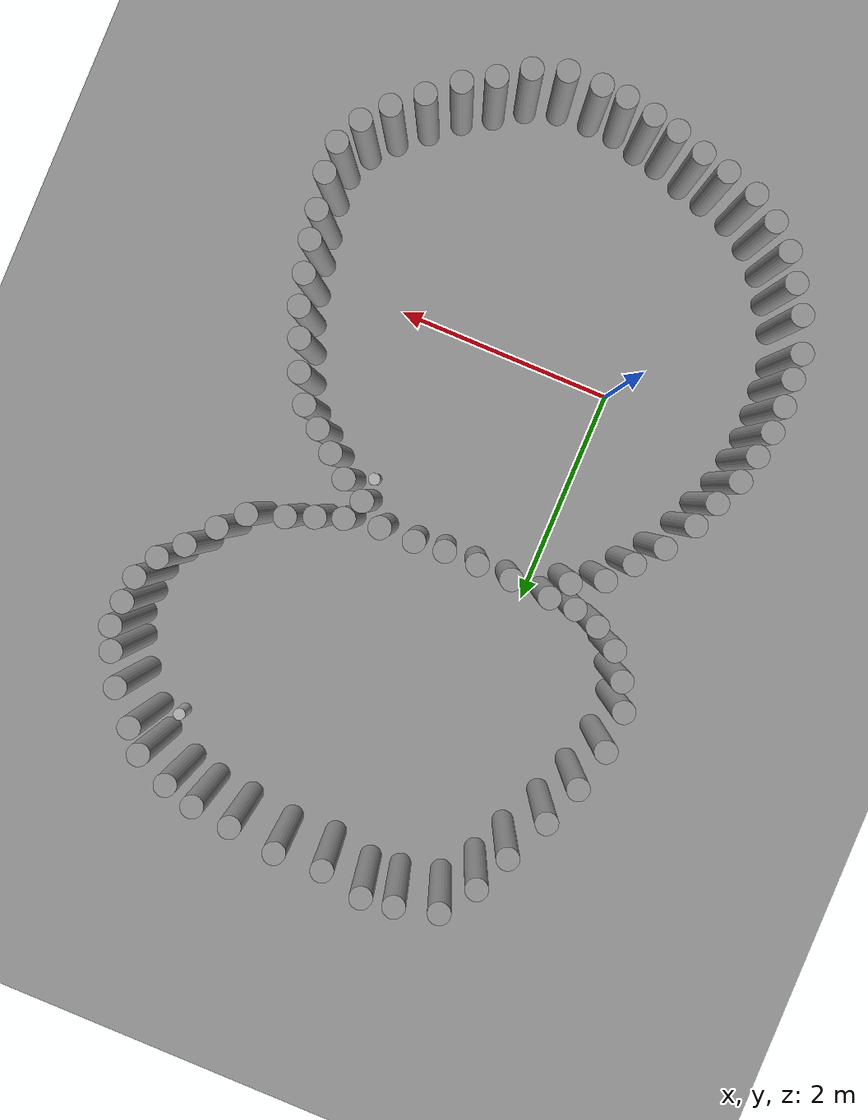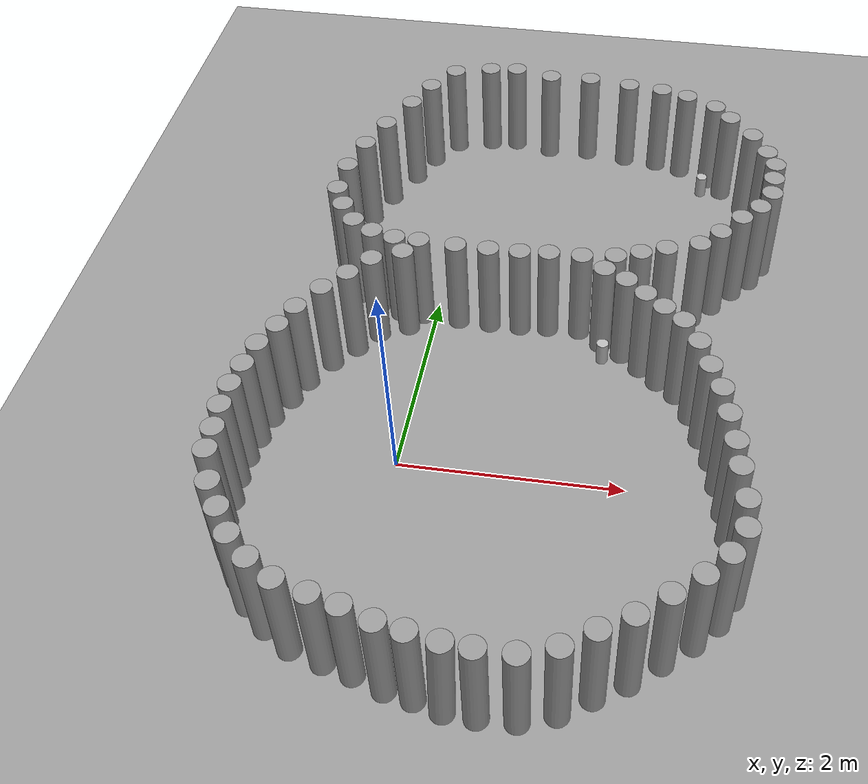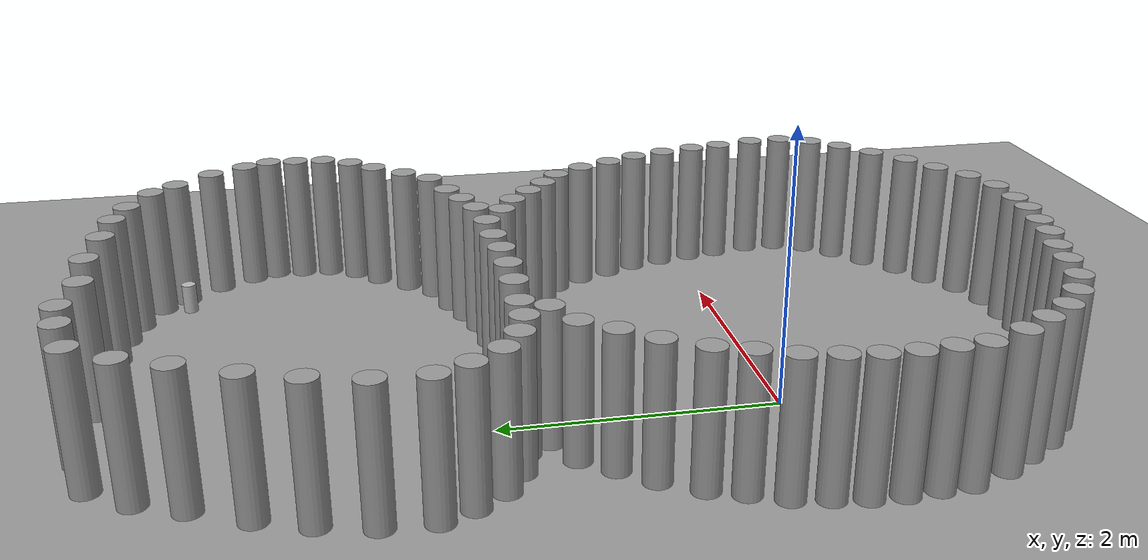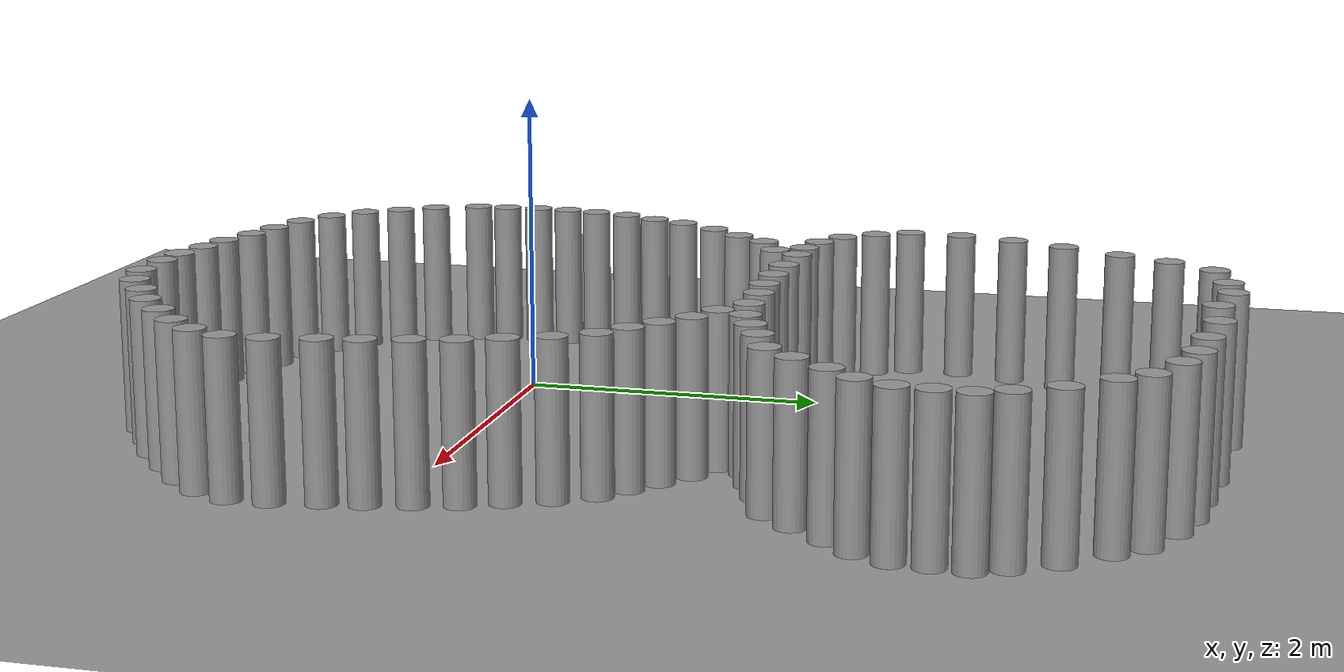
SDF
<sdf version="1.6">
 <world name="default">
  <light name="sun" type="directional">
   <pose>0 0 10 0 -0 0</pose>
   <diffuse>0.8 0.8 0.8 1</diffuse>
   <specular>0.2 0.2 0.2 1</specular>
   <attenuation>
    <range>1000</range>
    <constant>0.9</constant>
    <linear>0.01</linear>
    <quadratic>0.001</quadratic>
   </attenuation>
   <direction>0.5 0.1 -0.9</direction>
  </light>
  <scene><ambient>0.4 0.4 0.4 1</ambient><background>0.7 0.7 0.7 1</background><shadows>1</shadows></scene>
  <physics name="default_physics" default="0" type="ode">
   <max_step_size>0.01</max_step_size>
   <real_time_factor>1</real_time_factor>
   <real_time_update_rate>100</real_time_update_rate>
  </physics>
  <model name="ground_plane_0">
   <static>1</static>
   <link name="link">
    <collision name="collision">
     <geometry><plane><normal>0 0 1</normal><size>100 100</size></plane></geometry>
     <surface><friction><ode><mu>100</mu><mu2>50</mu2></ode></friction></surface>
    </collision>
    <visual name="visual">
     <cast_shadows>0</cast_shadows>
     <geometry><plane><normal>0 0 1</normal><size>100 100</size></plane></geometry>
     <material>
      <script><uri>file://media/materials/scripts/gazebo.material</uri><name>Gazebo/Grey</name></script>
     </material>
    </visual>
    <velocity_decay><linear>0</linear><angular>0</angular></velocity_decay>
   </link>
   <pose>0.497681 0 0 0 -0 0</pose>
  </model>
  <gravity>0 0 -9.8</gravity>
  <magnetic_field>6e-06 2.3e-05 -4.2e-05</magnetic_field>
  <atmosphere type="adiabatic"/>
  <spherical_coordinates>
   <surface_model>EARTH_WGS84</surface_model>
   <latitude_deg>0</latitude_deg>
   <longitude_deg>0</longitude_deg>
   <elevation>0</elevation>
   <heading_deg>0</heading_deg>
  </spherical_coordinates>
  <model name="small_cylinder_0">
   <link name="link">
    <inertial>
     <mass>1</mass>
     <inertia><ixx>0.145833</ixx><ixy>0</ixy><ixz>0</ixz><iyy>0.145833</iyy><iyz>0</iyz><izz>0.125</izz></inertia>
    </inertial>
    <visual name="visual">
     <geometry><cylinder><radius>0.1</radius><length>1</length></cylinder></geometry>
     <material>
      <script><name>Gazebo/Grey</name><uri>file://media/materials/scripts/gazebo.material</uri></script>
      <ambient>0.3 0.3 0.3 1</ambient>
      <diffuse>0.7 0.7 0.7 1</diffuse>
      <specular>0.01 0.01 0.01 1</specular>
      <emissive>0 0 0 1</emissive>
      <shader type="vertex"><normal_map>__default__</normal_map></shader>
     </material>
    </visual>
    <collision name="collision">
     <geometry><cylinder><radius>0.1</radius><length>1</length></cylinder></geometry>
     <surface>
      <friction>
       <ode><mu>1</mu><mu2>1</mu2><fdir1>0 0 0</fdir1><slip1>0</slip1><slip2>0</slip2></ode>
       <torsional>
        <coefficient>1</coefficient>
        <patch_radius>0</patch_radius>
        <surface_radius>0</surface_radius>
        <use_patch_radius>1</use_patch_radius>
        <ode><slip>0</slip></ode>
       </torsional>
      </friction>
      <bounce><restitution_coefficient>0</restitution_coefficient><threshold>1e+06</threshold></bounce>
      <contact>
       <collide_without_contact>0</collide_without_contact>
       <collide_without_contact_bitmask>1</collide_without_contact_bitmask>
       <collide_bitmask>1</collide_bitmask>
       <ode>
        <soft_cfm>0</soft_cfm>
        <soft_erp>0.2</soft_erp>
        <kp>1e+13</kp>
        <kd>1</kd>
        <max_vel>0.01</max_vel>
        <min_depth>0</min_depth>
       </ode>
       <bullet>
        <split_impulse>1</split_impulse>
        <split_impulse_penetration_threshold>-0.01</split_impulse_penetration_threshold>
        <soft_cfm>0</soft_cfm>
        <soft_erp>0.2</soft_erp>
        <kp>1e+13</kp>
        <kd>1</kd>
       </bullet>
      </contact>
     </surface>
    </collision>
   </link>
   <static>1</static>
   <pose>0.821332 1.81475 0.499121 0 6e-06 -0.010888</pose>
  </model>
  <model name="small_cylinder_0_clone">
   <link name="link">
    <inertial>
     <mass>1</mass>
     <inertia><ixx>0.145833</ixx><ixy>0</ixy><ixz>0</ixz><iyy>0.145833</iyy><iyz>0</iyz><izz>0.125</izz></inertia>
    </inertial>
    <visual name="visual">
     <geometry><cylinder><radius>0.1</radius><length>1</length></cylinder></geometry>
     <material>
      <script><name>Gazebo/Grey</name><uri>file://media/materials/scripts/gazebo.material</uri></script>
      <ambient>0.3 0.3 0.3 1</ambient>
      <diffuse>0.7 0.7 0.7 1</diffuse>
      <specular>0.01 0.01 0.01 1</specular>
      <emissive>0 0 0 1</emissive>
      <shader type="vertex"><normal_map>__default__</normal_map></shader>
     </material>
    </visual>
    <collision name="collision">
     <geometry><cylinder><radius>0.1</radius><length>1</length></cylinder></geometry>
     <surface>
      <friction>
       <ode><mu>1</mu><mu2>1</mu2><fdir1>0 0 0</fdir1><slip1>0</slip1><slip2>0</slip2></ode>
       <torsional>
        <coefficient>1</coefficient>
        <patch_radius>0</patch_radius>
        <surface_radius>0</surface_radius>
        <use_patch_radius>1</use_patch_radius>
        <ode><slip>0</slip></ode>
       </torsional>
      </friction>
      <bounce><restitution_coefficient>0</restitution_coefficient><threshold>1e+06</threshold></bounce>
      <contact>
       <collide_without_contact>0</collide_without_contact>
       <collide_without_contact_bitmask>1</collide_without_contact_bitmask>
       <collide_bitmask>1</collide_bitmask>
       <ode>
        <soft_cfm>0</soft_cfm>
        <soft_erp>0.2</soft_erp>
        <kp>1e+13</kp>
        <kd>1</kd>
        <max_vel>0.01</max_vel>
        <min_depth>0</min_depth>
       </ode>
       <bullet>
        <split_impulse>1</split_impulse>
        <split_impulse_penetration_threshold>-0.01</split_impulse_penetration_threshold>
        <soft_cfm>0</soft_cfm>
        <soft_erp>0.2</soft_erp>
        <kp>1e+13</kp>
        <kd>1</kd>
       </bullet>
      </contact>
     </surface>
    </collision>
   </link>
   <static>1</static>
   <pose>1.38888 1.84077 0.499121 -0 6e-06 -0.010855</pose>
  </model>
  <model name="small_cylinder_0_clone_0">
   <link name="link">
    <inertial>
     <mass>1</mass>
     <inertia><ixx>0.145833</ixx><ixy>0</ixy><ixz>0</ixz><iyy>0.145833</iyy><iyz>0</iyz><izz>0.125</izz></inertia>
    </inertial>
    <visual name="visual">
     <geometry><cylinder><radius>0.1</radius><length>1</length></cylinder></geometry>
     <material>
      <script><name>Gazebo/Grey</name><uri>file://media/materials/scripts/gazebo.material</uri></script>
      <ambient>0.3 0.3 0.3 1</ambient>
      <diffuse>0.7 0.7 0.7 1</diffuse>
      <specular>0.01 0.01 0.01 1</specular>
      <emissive>0 0 0 1</emissive>
      <shader type="vertex"><normal_map>__default__</normal_map></shader>
     </material>
    </visual>
    <collision name="collision">
     <geometry><cylinder><radius>0.1</radius><length>1</length></cylinder></geometry>
     <surface>
      <friction>
       <ode><mu>1</mu><mu2>1</mu2><fdir1>0 0 0</fdir1><slip1>0</slip1><slip2>0</slip2></ode>
       <torsional>
        <coefficient>1</coefficient>
        <patch_radius>0</patch_radius>
        <surface_radius>0</surface_radius>
        <use_patch_radius>1</use_patch_radius>
        <ode><slip>0</slip></ode>
       </torsional>
      </friction>
      <bounce><restitution_coefficient>0</restitution_coefficient><threshold>1e+06</threshold></bounce>
      <contact>
       <collide_without_contact>0</collide_without_contact>
       <collide_without_contact_bitmask>1</collide_without_contact_bitmask>
       <collide_bitmask>1</collide_bitmask>
       <ode>
        <soft_cfm>0</soft_cfm>
        <soft_erp>0.2</soft_erp>
        <kp>1e+13</kp>
        <kd>1</kd>
        <max_vel>0.01</max_vel>
        <min_depth>0</min_depth>
       </ode>
       <bullet>
        <split_impulse>1</split_impulse>
        <split_impulse_penetration_threshold>-0.01</split_impulse_penetration_threshold>
        <soft_cfm>0</soft_cfm>
        <soft_erp>0.2</soft_erp>
        <kp>1e+13</kp>
        <kd>1</kd>
       </bullet>
      </contact>
     </surface>
    </collision>
   </link>
   <static>1</static>
   <pose>2.8271 -1.1924 0.499121 0 6e-06 -0.010915</pose>
  </model>
  <model name="small_cylinder_0_clone_1">
   <link name="link">
    <inertial>
     <mass>1</mass>
     <inertia><ixx>0.145833</ixx><ixy>0</ixy><ixz>0</ixz><iyy>0.145833</iyy><iyz>0</iyz><izz>0.125</izz></inertia>
    </inertial>
    <visual name="visual">
     <geometry><cylinder><radius>0.1</radius><length>1</length></cylinder></geometry>
     <material>
      <script><name>Gazebo/Grey</name><uri>file://media/materials/scripts/gazebo.material</uri></script>
      <ambient>0.3 0.3 0.3 1</ambient>
      <diffuse>0.7 0.7 0.7 1</diffuse>
      <specular>0.01 0.01 0.01 1</specular>
      <emissive>0 0 0 1</emissive>
      <shader type="vertex"><normal_map>__default__</normal_map></shader>
     </material>
    </visual>
    <collision name="collision">
     <geometry><cylinder><radius>0.1</radius><length>1</length></cylinder></geometry>
     <surface>
      <friction>
       <ode><mu>1</mu><mu2>1</mu2><fdir1>0 0 0</fdir1><slip1>0</slip1><slip2>0</slip2></ode>
       <torsional>
        <coefficient>1</coefficient>
        <patch_radius>0</patch_radius>
        <surface_radius>0</surface_radius>
        <use_patch_radius>1</use_patch_radius>
        <ode><slip>0</slip></ode>
       </torsional>
      </friction>
      <bounce><restitution_coefficient>0</restitution_coefficient><threshold>1e+06</threshold></bounce>
      <contact>
       <collide_without_contact>0</collide_without_contact>
       <collide_without_contact_bitmask>1</collide_without_contact_bitmask>
       <collide_bitmask>1</collide_bitmask>
       <ode>
        <soft_cfm>0</soft_cfm>
        <soft_erp>0.2</soft_erp>
        <kp>1e+13</kp>
        <kd>1</kd>
        <max_vel>0.01</max_vel>
        <min_depth>0</min_depth>
       </ode>
       <bullet>
        <split_impulse>1</split_impulse>
        <split_impulse_penetration_threshold>-0.01</split_impulse_penetration_threshold>
        <soft_cfm>0</soft_cfm>
        <soft_erp>0.2</soft_erp>
        <kp>1e+13</kp>
        <kd>1</kd>
       </bullet>
      </contact>
     </surface>
    </collision>
   </link>
   <static>1</static>
   <pose>2.64692 -1.39777 0.499121 0 6e-06 -0.010887</pose>
  </model>
  <model name="small_cylinder_0_clone_2">
   <link name="link">
    <inertial>
     <mass>1</mass>
     <inertia><ixx>0.145833</ixx><ixy>0</ixy><ixz>0</ixz><iyy>0.145833</iyy><iyz>0</iyz><izz>0.125</izz></inertia>
    </inertial>
    <visual name="visual">
     <geometry><cylinder><radius>0.1</radius><length>1</length></cylinder></geometry>
     <material>
      <script><name>Gazebo/Grey</name><uri>file://media/materials/scripts/gazebo.material</uri></script>
      <ambient>0.3 0.3 0.3 1</ambient>
      <diffuse>0.7 0.7 0.7 1</diffuse>
      <specular>0.01 0.01 0.01 1</specular>
      <emissive>0 0 0 1</emissive>
      <shader type="vertex"><normal_map>__default__</normal_map></shader>
     </material>
    </visual>
    <collision name="collision">
     <geometry><cylinder><radius>0.1</radius><length>1</length></cylinder></geometry>
     <surface>
      <friction>
       <ode><mu>1</mu><mu2>1</mu2><fdir1>0 0 0</fdir1><slip1>0</slip1><slip2>0</slip2></ode>
       <torsional>
        <coefficient>1</coefficient>
        <patch_radius>0</patch_radius>
        <surface_radius>0</surface_radius>
        <use_patch_radius>1</use_patch_radius>
        <ode><slip>0</slip></ode>
       </torsional>
      </friction>
      <bounce><restitution_coefficient>0</restitution_coefficient><threshold>1e+06</threshold></bounce>
      <contact>
       <collide_without_contact>0</collide_without_contact>
       <collide_without_contact_bitmask>1</collide_without_contact_bitmask>
       <collide_bitmask>1</collide_bitmask>
       <ode>
        <soft_cfm>0</soft_cfm>
        <soft_erp>0.2</soft_erp>
        <kp>1e+13</kp>
        <kd>1</kd>
        <max_vel>0.01</max_vel>
        <min_depth>0</min_depth>
       </ode>
       <bullet>
        <split_impulse>1</split_impulse>
        <split_impulse_penetration_threshold>-0.01</split_impulse_penetration_threshold>
        <soft_cfm>0</soft_cfm>
        <soft_erp>0.2</soft_erp>
        <kp>1e+13</kp>
        <kd>1</kd>
       </bullet>
      </contact>
     </surface>
    </collision>
   </link>
   <static>1</static>
   <pose>2.418 -1.59621 0.499121 0 6e-06 -0.01088</pose>
  </model>
  <model name="small_cylinder_0_clone_3">
   <link name="link">
    <inertial>
     <mass>1</mass>
     <inertia><ixx>0.145833</ixx><ixy>0</ixy><ixz>0</ixz><iyy>0.145833</iyy><iyz>0</iyz><izz>0.125</izz></inertia>
    </inertial>
    <visual name="visual">
     <geometry><cylinder><radius>0.1</radius><length>1</length></cylinder></geometry>
     <material>
      <script><name>Gazebo/Grey</name><uri>file://media/materials/scripts/gazebo.material</uri></script>
      <ambient>0.3 0.3 0.3 1</ambient>
      <diffuse>0.7 0.7 0.7 1</diffuse>
      <specular>0.01 0.01 0.01 1</specular>
      <emissive>0 0 0 1</emissive>
      <shader type="vertex"><normal_map>__default__</normal_map></shader>
     </material>
    </visual>
    <collision name="collision">
     <geometry><cylinder><radius>0.1</radius><length>1</length></cylinder></geometry>
     <surface>
      <friction>
       <ode><mu>1</mu><mu2>1</mu2><fdir1>0 0 0</fdir1><slip1>0</slip1><slip2>0</slip2></ode>
       <torsional>
        <coefficient>1</coefficient>
        <patch_radius>0</patch_radius>
        <surface_radius>0</surface_radius>
        <use_patch_radius>1</use_patch_radius>
        <ode><slip>0</slip></ode>
       </torsional>
      </friction>
      <bounce><restitution_coefficient>0</restitution_coefficient><threshold>1e+06</threshold></bounce>
      <contact>
       <collide_without_contact>0</collide_without_contact>
       <collide_without_contact_bitmask>1</collide_without_contact_bitmask>
       <collide_bitmask>1</collide_bitmask>
       <ode>
        <soft_cfm>0</soft_cfm>
        <soft_erp>0.2</soft_erp>
        <kp>1e+13</kp>
        <kd>1</kd>
        <max_vel>0.01</max_vel>
        <min_depth>0</min_depth>
       </ode>
       <bullet>
        <split_impulse>1</split_impulse>
        <split_impulse_penetration_threshold>-0.01</split_impulse_penetration_threshold>
        <soft_cfm>0</soft_cfm>
        <soft_erp>0.2</soft_erp>
        <kp>1e+13</kp>
        <kd>1</kd>
       </bullet>
      </contact>
     </surface>
    </collision>
   </link>
   <static>1</static>
   <pose>2.17816 -1.80058 0.499121 0 6e-06 -0.010876</pose>
  </model>
  <model name="small_cylinder_0_clone_4">
   <link name="link">
    <inertial>
     <mass>1</mass>
     <inertia><ixx>0.145833</ixx><ixy>0</ixy><ixz>0</ixz><iyy>0.145833</iyy><iyz>0</iyz><izz>0.125</izz></inertia>
    </inertial>
    <visual name="visual">
     <geometry><cylinder><radius>0.1</radius><length>1</length></cylinder></geometry>
     <material>
      <script><name>Gazebo/Grey</name><uri>file://media/materials/scripts/gazebo.material</uri></script>
      <ambient>0.3 0.3 0.3 1</ambient>
      <diffuse>0.7 0.7 0.7 1</diffuse>
      <specular>0.01 0.01 0.01 1</specular>
      <emissive>0 0 0 1</emissive>
      <shader type="vertex"><normal_map>__default__</normal_map></shader>
     </material>
    </visual>
    <collision name="collision">
     <geometry><cylinder><radius>0.1</radius><length>1</length></cylinder></geometry>
     <surface>
      <friction>
       <ode><mu>1</mu><mu2>1</mu2><fdir1>0 0 0</fdir1><slip1>0</slip1><slip2>0</slip2></ode>
       <torsional>
        <coefficient>1</coefficient>
        <patch_radius>0</patch_radius>
        <surface_radius>0</surface_radius>
        <use_patch_radius>1</use_patch_radius>
        <ode><slip>0</slip></ode>
       </torsional>
      </friction>
      <bounce><restitution_coefficient>0</restitution_coefficient><threshold>1e+06</threshold></bounce>
      <contact>
       <collide_without_contact>0</collide_without_contact>
       <collide_without_contact_bitmask>1</collide_without_contact_bitmask>
       <collide_bitmask>1</collide_bitmask>
       <ode>
        <soft_cfm>0</soft_cfm>
        <soft_erp>0.2</soft_erp>
        <kp>1e+13</kp>
        <kd>1</kd>
        <max_vel>0.01</max_vel>
        <min_depth>0</min_depth>
       </ode>
       <bullet>
        <split_impulse>1</split_impulse>
        <split_impulse_penetration_threshold>-0.01</split_impulse_penetration_threshold>
        <soft_cfm>0</soft_cfm>
        <soft_erp>0.2</soft_erp>
        <kp>1e+13</kp>
        <kd>1</kd>
       </bullet>
      </contact>
     </surface>
    </collision>
   </link>
   <static>1</static>
   <pose>1.92933 -1.95531 0.499121 0 6e-06 -0.01088</pose>
  </model>
  <model name="small_cylinder_0_clone_5">
   <link name="link">
    <inertial>
     <mass>1</mass>
     <inertia><ixx>0.145833</ixx><ixy>0</ixy><ixz>0</ixz><iyy>0.145833</iyy><iyz>0</iyz><izz>0.125</izz></inertia>
    </inertial>
    <visual name="visual">
     <geometry><cylinder><radius>0.1</radius><length>1</length></cylinder></geometry>
     <material>
      <script><name>Gazebo/Grey</name><uri>file://media/materials/scripts/gazebo.material</uri></script>
      <ambient>0.3 0.3 0.3 1</ambient>
      <diffuse>0.7 0.7 0.7 1</diffuse>
      <specular>0.01 0.01 0.01 1</specular>
      <emissive>0 0 0 1</emissive>
      <shader type="vertex"><normal_map>__default__</normal_map></shader>
     </material>
    </visual>
    <collision name="collision">
     <geometry><cylinder><radius>0.1</radius><length>1</length></cylinder></geometry>
     <surface>
      <friction>
       <ode><mu>1</mu><mu2>1</mu2><fdir1>0 0 0</fdir1><slip1>0</slip1><slip2>0</slip2></ode>
       <torsional>
        <coefficient>1</coefficient>
        <patch_radius>0</patch_radius>
        <surface_radius>0</surface_radius>
        <use_patch_radius>1</use_patch_radius>
        <ode><slip>0</slip></ode>
       </torsional>
      </friction>
      <bounce><restitution_coefficient>0</restitution_coefficient><threshold>1e+06</threshold></bounce>
      <contact>
       <collide_without_contact>0</collide_without_contact>
       <collide_without_contact_bitmask>1</collide_without_contact_bitmask>
       <collide_bitmask>1</collide_bitmask>
       <ode>
        <soft_cfm>0</soft_cfm>
        <soft_erp>0.2</soft_erp>
        <kp>1e+13</kp>
        <kd>1</kd>
        <max_vel>0.01</max_vel>
        <min_depth>0</min_depth>
       </ode>
       <bullet>
        <split_impulse>1</split_impulse>
        <split_impulse_penetration_threshold>-0.01</split_impulse_penetration_threshold>
        <soft_cfm>0</soft_cfm>
        <soft_erp>0.2</soft_erp>
        <kp>1e+13</kp>
        <kd>1</kd>
       </bullet>
      </contact>
     </surface>
    </collision>
   </link>
   <static>1</static>
   <pose>1.68697 -2.12406 0.499121 -0 6e-06 -0.0109</pose>
  </model>
  <model name="small_cylinder_0_clone_6">
   <link name="link">
    <inertial>
     <mass>1</mass>
     <inertia><ixx>0.145833</ixx><ixy>0</ixy><ixz>0</ixz><iyy>0.145833</iyy><iyz>0</iyz><izz>0.125</izz></inertia>
    </inertial>
    <visual name="visual">
     <geometry><cylinder><radius>0.1</radius><length>1</length></cylinder></geometry>
     <material>
      <script><name>Gazebo/Grey</name><uri>file://media/materials/scripts/gazebo.material</uri></script>
      <ambient>0.3 0.3 0.3 1</ambient>
      <diffuse>0.7 0.7 0.7 1</diffuse>
      <specular>0.01 0.01 0.01 1</specular>
      <emissive>0 0 0 1</emissive>
      <shader type="vertex"><normal_map>__default__</normal_map></shader>
     </material>
    </visual>
    <collision name="collision">
     <geometry><cylinder><radius>0.1</radius><length>1</length></cylinder></geometry>
     <surface>
      <friction>
       <ode><mu>1</mu><mu2>1</mu2><fdir1>0 0 0</fdir1><slip1>0</slip1><slip2>0</slip2></ode>
       <torsional>
        <coefficient>1</coefficient>
        <patch_radius>0</patch_radius>
        <surface_radius>0</surface_radius>
        <use_patch_radius>1</use_patch_radius>
        <ode><slip>0</slip></ode>
       </torsional>
      </friction>
      <bounce><restitution_coefficient>0</restitution_coefficient><threshold>1e+06</threshold></bounce>
      <contact>
       <collide_without_contact>0</collide_without_contact>
       <collide_without_contact_bitmask>1</collide_without_contact_bitmask>
       <collide_bitmask>1</collide_bitmask>
       <ode>
        <soft_cfm>0</soft_cfm>
        <soft_erp>0.2</soft_erp>
        <kp>1e+13</kp>
        <kd>1</kd>
        <max_vel>0.01</max_vel>
        <min_depth>0</min_depth>
       </ode>
       <bullet>
        <split_impulse>1</split_impulse>
        <split_impulse_penetration_threshold>-0.01</split_impulse_penetration_threshold>
        <soft_cfm>0</soft_cfm>
        <soft_erp>0.2</soft_erp>
        <kp>1e+13</kp>
        <kd>1</kd>
       </bullet>
      </contact>
     </surface>
    </collision>
   </link>
   <static>1</static>
   <pose>1.40397 -2.22186 0.499121 0 -6e-06 0.008928</pose>
  </model>
  <model name="small_cylinder_0_clone_7">
   <link name="link">
    <inertial>
     <mass>1</mass>
     <inertia><ixx>0.145833</ixx><ixy>0</ixy><ixz>0</ixz><iyy>0.145833</iyy><iyz>0</iyz><izz>0.125</izz></inertia>
    </inertial>
    <visual name="visual">
     <geometry><cylinder><radius>0.1</radius><length>1</length></cylinder></geometry>
     <material>
      <script><name>Gazebo/Grey</name><uri>file://media/materials/scripts/gazebo.material</uri></script>
      <ambient>0.3 0.3 0.3 1</ambient>
      <diffuse>0.7 0.7 0.7 1</diffuse>
      <specular>0.01 0.01 0.01 1</specular>
      <emissive>0 0 0 1</emissive>
      <shader type="vertex"><normal_map>__default__</normal_map></shader>
     </material>
    </visual>
    <collision name="collision">
     <geometry><cylinder><radius>0.1</radius><length>1</length></cylinder></geometry>
     <surface>
      <friction>
       <ode><mu>1</mu><mu2>1</mu2><fdir1>0 0 0</fdir1><slip1>0</slip1><slip2>0</slip2></ode>
       <torsional>
        <coefficient>1</coefficient>
        <patch_radius>0</patch_radius>
        <surface_radius>0</surface_radius>
        <use_patch_radius>1</use_patch_radius>
        <ode><slip>0</slip></ode>
       </torsional>
      </friction>
      <bounce><restitution_coefficient>0</restitution_coefficient><threshold>1e+06</threshold></bounce>
      <contact>
       <collide_without_contact>0</collide_without_contact>
       <collide_without_contact_bitmask>1</collide_without_contact_bitmask>
       <collide_bitmask>1</collide_bitmask>
       <ode>
        <soft_cfm>0</soft_cfm>
        <soft_erp>0.2</soft_erp>
        <kp>1e+13</kp>
        <kd>1</kd>
        <max_vel>0.01</max_vel>
        <min_depth>0</min_depth>
       </ode>
       <bullet>
        <split_impulse>1</split_impulse>
        <split_impulse_penetration_threshold>-0.01</split_impulse_penetration_threshold>
        <soft_cfm>0</soft_cfm>
        <soft_erp>0.2</soft_erp>
        <kp>1e+13</kp>
        <kd>1</kd>
       </bullet>
      </contact>
     </surface>
    </collision>
   </link>
   <static>1</static>
   <pose>1.10145 -2.22877 0.50125 -0.010495 -0.00771 -0.658429</pose>
  </model>
  <model name="small_cylinder_0_clone_8">
   <link name="link">
    <inertial>
     <mass>1</mass>
     <inertia><ixx>0.145833</ixx><ixy>0</ixy><ixz>0</ixz><iyy>0.145833</iyy><iyz>0</iyz><izz>0.125</izz></inertia>
    </inertial>
    <visual name="visual">
     <geometry><cylinder><radius>0.1</radius><length>1</length></cylinder></geometry>
     <material>
      <script><name>Gazebo/Grey</name><uri>file://media/materials/scripts/gazebo.material</uri></script>
      <ambient>0.3 0.3 0.3 1</ambient>
      <diffuse>0.7 0.7 0.7 1</diffuse>
      <specular>0.01 0.01 0.01 1</specular>
      <emissive>0 0 0 1</emissive>
      <shader type="vertex"><normal_map>__default__</normal_map></shader>
     </material>
    </visual>
    <collision name="collision">
     <geometry><cylinder><radius>0.1</radius><length>1</length></cylinder></geometry>
     <surface>
      <friction>
       <ode><mu>1</mu><mu2>1</mu2><fdir1>0 0 0</fdir1><slip1>0</slip1><slip2>0</slip2></ode>
       <torsional>
        <coefficient>1</coefficient>
        <patch_radius>0</patch_radius>
        <surface_radius>0</surface_radius>
        <use_patch_radius>1</use_patch_radius>
        <ode><slip>0</slip></ode>
       </torsional>
      </friction>
      <bounce><restitution_coefficient>0</restitution_coefficient><threshold>1e+06</threshold></bounce>
      <contact>
       <collide_without_contact>0</collide_without_contact>
       <collide_without_contact_bitmask>1</collide_without_contact_bitmask>
       <collide_bitmask>1</collide_bitmask>
       <ode>
        <soft_cfm>0</soft_cfm>
        <soft_erp>0.2</soft_erp>
        <kp>1e+13</kp>
        <kd>1</kd>
        <max_vel>0.01</max_vel>
        <min_depth>0</min_depth>
       </ode>
       <bullet>
        <split_impulse>1</split_impulse>
        <split_impulse_penetration_threshold>-0.01</split_impulse_penetration_threshold>
        <soft_cfm>0</soft_cfm>
        <soft_erp>0.2</soft_erp>
        <kp>1e+13</kp>
        <kd>1</kd>
       </bullet>
      </contact>
     </surface>
    </collision>
   </link>
   <static>1</static>
   <pose>0.859339 -2.21794 0.50312 -0.007979 -0.033217 -2.34045</pose>
  </model>
  <model name="small_cylinder_0_clone_9">
   <link name="link">
    <inertial>
     <mass>1</mass>
     <inertia><ixx>0.145833</ixx><ixy>0</ixy><ixz>0</ixz><iyy>0.145833</iyy><iyz>0</iyz><izz>0.125</izz></inertia>
    </inertial>
    <visual name="visual">
     <geometry><cylinder><radius>0.1</radius><length>1</length></cylinder></geometry>
     <material>
      <script><name>Gazebo/Grey</name><uri>file://media/materials/scripts/gazebo.material</uri></script>
      <ambient>0.3 0.3 0.3 1</ambient>
      <diffuse>0.7 0.7 0.7 1</diffuse>
      <specular>0.01 0.01 0.01 1</specular>
      <emissive>0 0 0 1</emissive>
      <shader type="vertex"><normal_map>__default__</normal_map></shader>
     </material>
    </visual>
    <collision name="collision">
     <geometry><cylinder><radius>0.1</radius><length>1</length></cylinder></geometry>
     <surface>
      <friction>
       <ode><mu>1</mu><mu2>1</mu2><fdir1>0 0 0</fdir1><slip1>0</slip1><slip2>0</slip2></ode>
       <torsional>
        <coefficient>1</coefficient>
        <patch_radius>0</patch_radius>
        <surface_radius>0</surface_radius>
        <use_patch_radius>1</use_patch_radius>
        <ode><slip>0</slip></ode>
       </torsional>
      </friction>
      <bounce><restitution_coefficient>0</restitution_coefficient><threshold>1e+06</threshold></bounce>
      <contact>
       <collide_without_contact>0</collide_without_contact>
       <collide_without_contact_bitmask>1</collide_without_contact_bitmask>
       <collide_bitmask>1</collide_bitmask>
       <ode>
        <soft_cfm>0</soft_cfm>
        <soft_erp>0.2</soft_erp>
        <kp>1e+13</kp>
        <kd>1</kd>
        <max_vel>0.01</max_vel>
        <min_depth>0</min_depth>
       </ode>
       <bullet>
        <split_impulse>1</split_impulse>
        <split_impulse_penetration_threshold>-0.01</split_impulse_penetration_threshold>
        <soft_cfm>0</soft_cfm>
        <soft_erp>0.2</soft_erp>
        <kp>1e+13</kp>
        <kd>1</kd>
       </bullet>
      </contact>
     </surface>
    </collision>
   </link>
   <static>1</static>
   <pose>0.612069 -2.16006 0.499121 0 -6e-06 0.002231</pose>
  </model>
  <model name="small_cylinder_0_clone_10">
   <link name="link">
    <inertial>
     <mass>1</mass>
     <inertia><ixx>0.145833</ixx><ixy>0</ixy><ixz>0</ixz><iyy>0.145833</iyy><iyz>0</iyz><izz>0.125</izz></inertia>
    </inertial>
    <visual name="visual">
     <geometry><cylinder><radius>0.1</radius><length>1</length></cylinder></geometry>
     <material>
      <script><name>Gazebo/Grey</name><uri>file://media/materials/scripts/gazebo.material</uri></script>
      <ambient>0.3 0.3 0.3 1</ambient>
      <diffuse>0.7 0.7 0.7 1</diffuse>
      <specular>0.01 0.01 0.01 1</specular>
      <emissive>0 0 0 1</emissive>
      <shader type="vertex"><normal_map>__default__</normal_map></shader>
     </material>
    </visual>
    <collision name="collision">
     <geometry><cylinder><radius>0.1</radius><length>1</length></cylinder></geometry>
     <surface>
      <friction>
       <ode><mu>1</mu><mu2>1</mu2><fdir1>0 0 0</fdir1><slip1>0</slip1><slip2>0</slip2></ode>
       <torsional>
        <coefficient>1</coefficient>
        <patch_radius>0</patch_radius>
        <surface_radius>0</surface_radius>
        <use_patch_radius>1</use_patch_radius>
        <ode><slip>0</slip></ode>
       </torsional>
      </friction>
      <bounce><restitution_coefficient>0</restitution_coefficient><threshold>1e+06</threshold></bounce>
      <contact>
       <collide_without_contact>0</collide_without_contact>
       <collide_without_contact_bitmask>1</collide_without_contact_bitmask>
       <collide_bitmask>1</collide_bitmask>
       <ode>
        <soft_cfm>0</soft_cfm>
        <soft_erp>0.2</soft_erp>
        <kp>1e+13</kp>
        <kd>1</kd>
        <max_vel>0.01</max_vel>
        <min_depth>0</min_depth>
       </ode>
       <bullet>
        <split_impulse>1</split_impulse>
        <split_impulse_penetration_threshold>-0.01</split_impulse_penetration_threshold>
        <soft_cfm>0</soft_cfm>
        <soft_erp>0.2</soft_erp>
        <kp>1e+13</kp>
        <kd>1</kd>
       </bullet>
      </contact>
     </surface>
    </collision>
   </link>
   <static>1</static>
   <pose>0.116597 -2.0273 0.499121 0 6e-06 -0.010863</pose>
  </model>
  <model name="small_cylinder_0_clone_11">
   <link name="link">
    <inertial>
     <mass>1</mass>
     <inertia><ixx>0.145833</ixx><ixy>0</ixy><ixz>0</ixz><iyy>0.145833</iyy><iyz>0</iyz><izz>0.125</izz></inertia>
    </inertial>
    <visual name="visual">
     <geometry><cylinder><radius>0.1</radius><length>1</length></cylinder></geometry>
     <material>
      <script><name>Gazebo/Grey</name><uri>file://media/materials/scripts/gazebo.material</uri></script>
      <ambient>0.3 0.3 0.3 1</ambient>
      <diffuse>0.7 0.7 0.7 1</diffuse>
      <specular>0.01 0.01 0.01 1</specular>
      <emissive>0 0 0 1</emissive>
      <shader type="vertex"><normal_map>__default__</normal_map></shader>
     </material>
    </visual>
    <collision name="collision">
     <geometry><cylinder><radius>0.1</radius><length>1</length></cylinder></geometry>
     <surface>
      <friction>
       <ode><mu>1</mu><mu2>1</mu2><fdir1>0 0 0</fdir1><slip1>0</slip1><slip2>0</slip2></ode>
       <torsional>
        <coefficient>1</coefficient>
        <patch_radius>0</patch_radius>
        <surface_radius>0</surface_radius>
        <use_patch_radius>1</use_patch_radius>
        <ode><slip>0</slip></ode>
       </torsional>
      </friction>
      <bounce><restitution_coefficient>0</restitution_coefficient><threshold>1e+06</threshold></bounce>
      <contact>
       <collide_without_contact>0</collide_without_contact>
       <collide_without_contact_bitmask>1</collide_without_contact_bitmask>
       <collide_bitmask>1</collide_bitmask>
       <ode>
        <soft_cfm>0</soft_cfm>
        <soft_erp>0.2</soft_erp>
        <kp>1e+13</kp>
        <kd>1</kd>
        <max_vel>0.01</max_vel>
        <min_depth>0</min_depth>
       </ode>
       <bullet>
        <split_impulse>1</split_impulse>
        <split_impulse_penetration_threshold>-0.01</split_impulse_penetration_threshold>
        <soft_cfm>0</soft_cfm>
        <soft_erp>0.2</soft_erp>
        <kp>1e+13</kp>
        <kd>1</kd>
       </bullet>
      </contact>
     </surface>
    </collision>
   </link>
   <static>1</static>
   <pose>-0.131034 -1.96466 0.499121 0 6e-06 -0.010858</pose>
  </model>
  <model name="small_cylinder_0_clone_12">
   <link name="link">
    <inertial>
     <mass>1</mass>
     <inertia><ixx>0.145833</ixx><ixy>0</ixy><ixz>0</ixz><iyy>0.145833</iyy><iyz>0</iyz><izz>0.125</izz></inertia>
    </inertial>
    <visual name="visual">
     <geometry><cylinder><radius>0.1</radius><length>1</length></cylinder></geometry>
     <material>
      <script><name>Gazebo/Grey</name><uri>file://media/materials/scripts/gazebo.material</uri></script>
      <ambient>0.3 0.3 0.3 1</ambient>
      <diffuse>0.7 0.7 0.7 1</diffuse>
      <specular>0.01 0.01 0.01 1</specular>
      <emissive>0 0 0 1</emissive>
      <shader type="vertex"><normal_map>__default__</normal_map></shader>
     </material>
    </visual>
    <collision name="collision">
     <geometry><cylinder><radius>0.1</radius><length>1</length></cylinder></geometry>
     <surface>
      <friction>
       <ode><mu>1</mu><mu2>1</mu2><fdir1>0 0 0</fdir1><slip1>0</slip1><slip2>0</slip2></ode>
       <torsional>
        <coefficient>1</coefficient>
        <patch_radius>0</patch_radius>
        <surface_radius>0</surface_radius>
        <use_patch_radius>1</use_patch_radius>
        <ode><slip>0</slip></ode>
       </torsional>
      </friction>
      <bounce><restitution_coefficient>0</restitution_coefficient><threshold>1e+06</threshold></bounce>
      <contact>
       <collide_without_contact>0</collide_without_contact>
       <collide_without_contact_bitmask>1</collide_without_contact_bitmask>
       <collide_bitmask>1</collide_bitmask>
       <ode>
        <soft_cfm>0</soft_cfm>
        <soft_erp>0.2</soft_erp>
        <kp>1e+13</kp>
        <kd>1</kd>
        <max_vel>0.01</max_vel>
        <min_depth>0</min_depth>
       </ode>
       <bullet>
        <split_impulse>1</split_impulse>
        <split_impulse_penetration_threshold>-0.01</split_impulse_penetration_threshold>
        <soft_cfm>0</soft_cfm>
        <soft_erp>0.2</soft_erp>
        <kp>1e+13</kp>
        <kd>1</kd>
       </bullet>
      </contact>
     </surface>
    </collision>
   </link>
   <static>1</static>
   <pose>-0.414773 -1.88306 0.499121 0 6e-06 -0.010877</pose>
  </model>
  <model name="small_cylinder_0_clone_13">
   <link name="link">
    <inertial>
     <mass>1</mass>
     <inertia><ixx>0.145833</ixx><ixy>0</ixy><ixz>0</ixz><iyy>0.145833</iyy><iyz>0</iyz><izz>0.125</izz></inertia>
    </inertial>
    <visual name="visual">
     <geometry><cylinder><radius>0.1</radius><length>1</length></cylinder></geometry>
     <material>
      <script><name>Gazebo/Grey</name><uri>file://media/materials/scripts/gazebo.material</uri></script>
      <ambient>0.3 0.3 0.3 1</ambient>
      <diffuse>0.7 0.7 0.7 1</diffuse>
      <specular>0.01 0.01 0.01 1</specular>
      <emissive>0 0 0 1</emissive>
      <shader type="vertex"><normal_map>__default__</normal_map></shader>
     </material>
    </visual>
    <collision name="collision">
     <geometry><cylinder><radius>0.1</radius><length>1</length></cylinder></geometry>
     <surface>
      <friction>
       <ode><mu>1</mu><mu2>1</mu2><fdir1>0 0 0</fdir1><slip1>0</slip1><slip2>0</slip2></ode>
       <torsional>
        <coefficient>1</coefficient>
        <patch_radius>0</patch_radius>
        <surface_radius>0</surface_radius>
        <use_patch_radius>1</use_patch_radius>
        <ode><slip>0</slip></ode>
       </torsional>
      </friction>
      <bounce><restitution_coefficient>0</restitution_coefficient><threshold>1e+06</threshold></bounce>
      <contact>
       <collide_without_contact>0</collide_without_contact>
       <collide_without_contact_bitmask>1</collide_without_contact_bitmask>
       <collide_bitmask>1</collide_bitmask>
       <ode>
        <soft_cfm>0</soft_cfm>
        <soft_erp>0.2</soft_erp>
        <kp>1e+13</kp>
        <kd>1</kd>
        <max_vel>0.01</max_vel>
        <min_depth>0</min_depth>
       </ode>
       <bullet>
        <split_impulse>1</split_impulse>
        <split_impulse_penetration_threshold>-0.01</split_impulse_penetration_threshold>
        <soft_cfm>0</soft_cfm>
        <soft_erp>0.2</soft_erp>
        <kp>1e+13</kp>
        <kd>1</kd>
       </bullet>
      </contact>
     </surface>
    </collision>
   </link>
   <static>1</static>
   <pose>-0.648054 -1.73782 0.499121 0 6e-06 -0.010877</pose>
  </model>
  <model name="small_cylinder_0_clone_14">
   <link name="link">
    <inertial>
     <mass>1</mass>
     <inertia><ixx>0.145833</ixx><ixy>0</ixy><ixz>0</ixz><iyy>0.145833</iyy><iyz>0</iyz><izz>0.125</izz></inertia>
    </inertial>
    <visual name="visual">
     <geometry><cylinder><radius>0.1</radius><length>1</length></cylinder></geometry>
     <material>
      <script><name>Gazebo/Grey</name><uri>file://media/materials/scripts/gazebo.material</uri></script>
      <ambient>0.3 0.3 0.3 1</ambient>
      <diffuse>0.7 0.7 0.7 1</diffuse>
      <specular>0.01 0.01 0.01 1</specular>
      <emissive>0 0 0 1</emissive>
      <shader type="vertex"><normal_map>__default__</normal_map></shader>
     </material>
    </visual>
    <collision name="collision">
     <geometry><cylinder><radius>0.1</radius><length>1</length></cylinder></geometry>
     <surface>
      <friction>
       <ode><mu>1</mu><mu2>1</mu2><fdir1>0 0 0</fdir1><slip1>0</slip1><slip2>0</slip2></ode>
       <torsional>
        <coefficient>1</coefficient>
        <patch_radius>0</patch_radius>
        <surface_radius>0</surface_radius>
        <use_patch_radius>1</use_patch_radius>
        <ode><slip>0</slip></ode>
       </torsional>
      </friction>
      <bounce><restitution_coefficient>0</restitution_coefficient><threshold>1e+06</threshold></bounce>
      <contact>
       <collide_without_contact>0</collide_without_contact>
       <collide_without_contact_bitmask>1</collide_without_contact_bitmask>
       <collide_bitmask>1</collide_bitmask>
       <ode>
        <soft_cfm>0</soft_cfm>
        <soft_erp>0.2</soft_erp>
        <kp>1e+13</kp>
        <kd>1</kd>
        <max_vel>0.01</max_vel>
        <min_depth>0</min_depth>
       </ode>
       <bullet>
        <split_impulse>1</split_impulse>
        <split_impulse_penetration_threshold>-0.01</split_impulse_penetration_threshold>
        <soft_cfm>0</soft_cfm>
        <soft_erp>0.2</soft_erp>
        <kp>1e+13</kp>
        <kd>1</kd>
       </bullet>
      </contact>
     </surface>
    </collision>
   </link>
   <static>1</static>
   <pose>-0.849121 -1.5563 0.499121 0 6e-06 -0.010873</pose>
  </model>
  <model name="small_cylinder_0_clone_15">
   <link name="link">
    <inertial>
     <mass>1</mass>
     <inertia><ixx>0.145833</ixx><ixy>0</ixy><ixz>0</ixz><iyy>0.145833</iyy><iyz>0</iyz><izz>0.125</izz></inertia>
    </inertial>
    <visual name="visual">
     <geometry><cylinder><radius>0.1</radius><length>1</length></cylinder></geometry>
     <material>
      <script><name>Gazebo/Grey</name><uri>file://media/materials/scripts/gazebo.material</uri></script>
      <ambient>0.3 0.3 0.3 1</ambient>
      <diffuse>0.7 0.7 0.7 1</diffuse>
      <specular>0.01 0.01 0.01 1</specular>
      <emissive>0 0 0 1</emissive>
      <shader type="vertex"><normal_map>__default__</normal_map></shader>
     </material>
    </visual>
    <collision name="collision">
     <geometry><cylinder><radius>0.1</radius><length>1</length></cylinder></geometry>
     <surface>
      <friction>
       <ode><mu>1</mu><mu2>1</mu2><fdir1>0 0 0</fdir1><slip1>0</slip1><slip2>0</slip2></ode>
       <torsional>
        <coefficient>1</coefficient>
        <patch_radius>0</patch_radius>
        <surface_radius>0</surface_radius>
        <use_patch_radius>1</use_patch_radius>
        <ode><slip>0</slip></ode>
       </torsional>
      </friction>
      <bounce><restitution_coefficient>0</restitution_coefficient><threshold>1e+06</threshold></bounce>
      <contact>
       <collide_without_contact>0</collide_without_contact>
       <collide_without_contact_bitmask>1</collide_without_contact_bitmask>
       <collide_bitmask>1</collide_bitmask>
       <ode>
        <soft_cfm>0</soft_cfm>
        <soft_erp>0.2</soft_erp>
        <kp>1e+13</kp>
        <kd>1</kd>
        <max_vel>0.01</max_vel>
        <min_depth>0</min_depth>
       </ode>
       <bullet>
        <split_impulse>1</split_impulse>
        <split_impulse_penetration_threshold>-0.01</split_impulse_penetration_threshold>
        <soft_cfm>0</soft_cfm>
        <soft_erp>0.2</soft_erp>
        <kp>1e+13</kp>
        <kd>1</kd>
       </bullet>
      </contact>
     </surface>
    </collision>
   </link>
   <static>1</static>
   <pose>0.379762 -2.11588 0.499121 0 6e-06 -0.01127</pose>
  </model>
  <model name="small_cylinder_0_clone_16">
   <link name="link">
    <inertial>
     <mass>1</mass>
     <inertia><ixx>0.145833</ixx><ixy>0</ixy><ixz>0</ixz><iyy>0.145833</iyy><iyz>0</iyz><izz>0.125</izz></inertia>
    </inertial>
    <visual name="visual">
     <geometry><cylinder><radius>0.1</radius><length>1</length></cylinder></geometry>
     <material>
      <script><name>Gazebo/Grey</name><uri>file://media/materials/scripts/gazebo.material</uri></script>
      <ambient>0.3 0.3 0.3 1</ambient>
      <diffuse>0.7 0.7 0.7 1</diffuse>
      <specular>0.01 0.01 0.01 1</specular>
      <emissive>0 0 0 1</emissive>
      <shader type="vertex"><normal_map>__default__</normal_map></shader>
     </material>
    </visual>
    <collision name="collision">
     <geometry><cylinder><radius>0.1</radius><length>1</length></cylinder></geometry>
     <surface>
      <friction>
       <ode><mu>1</mu><mu2>1</mu2><fdir1>0 0 0</fdir1><slip1>0</slip1><slip2>0</slip2></ode>
       <torsional>
        <coefficient>1</coefficient>
        <patch_radius>0</patch_radius>
        <surface_radius>0</surface_radius>
        <use_patch_radius>1</use_patch_radius>
        <ode><slip>0</slip></ode>
       </torsional>
      </friction>
      <bounce><restitution_coefficient>0</restitution_coefficient><threshold>1e+06</threshold></bounce>
      <contact>
       <collide_without_contact>0</collide_without_contact>
       <collide_without_contact_bitmask>1</collide_without_contact_bitmask>
       <collide_bitmask>1</collide_bitmask>
       <ode>
        <soft_cfm>0</soft_cfm>
        <soft_erp>0.2</soft_erp>
        <kp>1e+13</kp>
        <kd>1</kd>
        <max_vel>0.01</max_vel>
        <min_depth>0</min_depth>
       </ode>
       <bullet>
        <split_impulse>1</split_impulse>
        <split_impulse_penetration_threshold>-0.01</split_impulse_penetration_threshold>
        <soft_cfm>0</soft_cfm>
        <soft_erp>0.2</soft_erp>
        <kp>1e+13</kp>
        <kd>1</kd>
       </bullet>
      </contact>
     </surface>
    </collision>
   </link>
   <static>1</static>
   <pose>-0.999768 -1.3353 0.499121 0 6e-06 -0.011235</pose>
  </model>
  <model name="small_cylinder_0_clone_17">
   <link name="link">
    <inertial>
     <mass>1</mass>
     <inertia><ixx>0.145833</ixx><ixy>0</ixy><ixz>0</ixz><iyy>0.145833</iyy><iyz>0</iyz><izz>0.125</izz></inertia>
    </inertial>
    <visual name="visual">
     <geometry><cylinder><radius>0.1</radius><length>1</length></cylinder></geometry>
     <material>
      <script><name>Gazebo/Grey</name><uri>file://media/materials/scripts/gazebo.material</uri></script>
      <ambient>0.3 0.3 0.3 1</ambient>
      <diffuse>0.7 0.7 0.7 1</diffuse>
      <specular>0.01 0.01 0.01 1</specular>
      <emissive>0 0 0 1</emissive>
      <shader type="vertex"><normal_map>__default__</normal_map></shader>
     </material>
    </visual>
    <collision name="collision">
     <geometry><cylinder><radius>0.1</radius><length>1</length></cylinder></geometry>
     <surface>
      <friction>
       <ode><mu>1</mu><mu2>1</mu2><fdir1>0 0 0</fdir1><slip1>0</slip1><slip2>0</slip2></ode>
       <torsional>
        <coefficient>1</coefficient>
        <patch_radius>0</patch_radius>
        <surface_radius>0</surface_radius>
        <use_patch_radius>1</use_patch_radius>
        <ode><slip>0</slip></ode>
       </torsional>
      </friction>
      <bounce><restitution_coefficient>0</restitution_coefficient><threshold>1e+06</threshold></bounce>
      <contact>
       <collide_without_contact>0</collide_without_contact>
       <collide_without_contact_bitmask>1</collide_without_contact_bitmask>
       <collide_bitmask>1</collide_bitmask>
       <ode>
        <soft_cfm>0</soft_cfm>
        <soft_erp>0.2</soft_erp>
        <kp>1e+13</kp>
        <kd>1</kd>
        <max_vel>0.01</max_vel>
        <min_depth>0</min_depth>
       </ode>
       <bullet>
        <split_impulse>1</split_impulse>
        <split_impulse_penetration_threshold>-0.01</split_impulse_penetration_threshold>
        <soft_cfm>0</soft_cfm>
        <soft_erp>0.2</soft_erp>
        <kp>1e+13</kp>
        <kd>1</kd>
       </bullet>
      </contact>
     </surface>
    </collision>
   </link>
   <static>1</static>
   <pose>-1.14508 -1.11083 0.499121 0 6e-06 -0.010894</pose>
  </model>
  <model name="small_cylinder_0_clone_18">
   <link name="link">
    <inertial>
     <mass>1</mass>
     <inertia><ixx>0.145833</ixx><ixy>0</ixy><ixz>0</ixz><iyy>0.145833</iyy><iyz>0</iyz><izz>0.125</izz></inertia>
    </inertial>
    <visual name="visual">
     <geometry><cylinder><radius>0.1</radius><length>1</length></cylinder></geometry>
     <material>
      <script><name>Gazebo/Grey</name><uri>file://media/materials/scripts/gazebo.material</uri></script>
      <ambient>0.3 0.3 0.3 1</ambient>
      <diffuse>0.7 0.7 0.7 1</diffuse>
      <specular>0.01 0.01 0.01 1</specular>
      <emissive>0 0 0 1</emissive>
      <shader type="vertex"><normal_map>__default__</normal_map></shader>
     </material>
    </visual>
    <collision name="collision">
     <geometry><cylinder><radius>0.1</radius><length>1</length></cylinder></geometry>
     <surface>
      <friction>
       <ode><mu>1</mu><mu2>1</mu2><fdir1>0 0 0</fdir1><slip1>0</slip1><slip2>0</slip2></ode>
       <torsional>
        <coefficient>1</coefficient>
        <patch_radius>0</patch_radius>
        <surface_radius>0</surface_radius>
        <use_patch_radius>1</use_patch_radius>
        <ode><slip>0</slip></ode>
       </torsional>
      </friction>
      <bounce><restitution_coefficient>0</restitution_coefficient><threshold>1e+06</threshold></bounce>
      <contact>
       <collide_without_contact>0</collide_without_contact>
       <collide_without_contact_bitmask>1</collide_without_contact_bitmask>
       <collide_bitmask>1</collide_bitmask>
       <ode>
        <soft_cfm>0</soft_cfm>
        <soft_erp>0.2</soft_erp>
        <kp>1e+13</kp>
        <kd>1</kd>
        <max_vel>0.01</max_vel>
        <min_depth>0</min_depth>
       </ode>
       <bullet>
        <split_impulse>1</split_impulse>
        <split_impulse_penetration_threshold>-0.01</split_impulse_penetration_threshold>
        <soft_cfm>0</soft_cfm>
        <soft_erp>0.2</soft_erp>
        <kp>1e+13</kp>
        <kd>1</kd>
       </bullet>
      </contact>
     </surface>
    </collision>
   </link>
   <static>1</static>
   <pose>-1.26492 -0.816128 0.499121 0 6e-06 -0.010915</pose>
  </model>
  <model name="small_cylinder_0_clone_19">
   <link name="link">
    <inertial>
     <mass>1</mass>
     <inertia><ixx>0.145833</ixx><ixy>0</ixy><ixz>0</ixz><iyy>0.145833</iyy><iyz>0</iyz><izz>0.125</izz></inertia>
    </inertial>
    <visual name="visual">
     <geometry><cylinder><radius>0.1</radius><length>1</length></cylinder></geometry>
     <material>
      <script><name>Gazebo/Grey</name><uri>file://media/materials/scripts/gazebo.material</uri></script>
      <ambient>0.3 0.3 0.3 1</ambient>
      <diffuse>0.7 0.7 0.7 1</diffuse>
      <specular>0.01 0.01 0.01 1</specular>
      <emissive>0 0 0 1</emissive>
      <shader type="vertex"><normal_map>__default__</normal_map></shader>
     </material>
    </visual>
    <collision name="collision">
     <geometry><cylinder><radius>0.1</radius><length>1</length></cylinder></geometry>
     <surface>
      <friction>
       <ode><mu>1</mu><mu2>1</mu2><fdir1>0 0 0</fdir1><slip1>0</slip1><slip2>0</slip2></ode>
       <torsional>
        <coefficient>1</coefficient>
        <patch_radius>0</patch_radius>
        <surface_radius>0</surface_radius>
        <use_patch_radius>1</use_patch_radius>
        <ode><slip>0</slip></ode>
       </torsional>
      </friction>
      <bounce><restitution_coefficient>0</restitution_coefficient><threshold>1e+06</threshold></bounce>
      <contact>
       <collide_without_contact>0</collide_without_contact>
       <collide_without_contact_bitmask>1</collide_without_contact_bitmask>
       <collide_bitmask>1</collide_bitmask>
       <ode>
        <soft_cfm>0</soft_cfm>
        <soft_erp>0.2</soft_erp>
        <kp>1e+13</kp>
        <kd>1</kd>
        <max_vel>0.01</max_vel>
        <min_depth>0</min_depth>
       </ode>
       <bullet>
        <split_impulse>1</split_impulse>
        <split_impulse_penetration_threshold>-0.01</split_impulse_penetration_threshold>
        <soft_cfm>0</soft_cfm>
        <soft_erp>0.2</soft_erp>
        <kp>1e+13</kp>
        <kd>1</kd>
       </bullet>
      </contact>
     </surface>
    </collision>
   </link>
   <static>1</static>
   <pose>-0.784231 2.03076 0.499121 0 6e-06 -0.010826</pose>
  </model>
  <model name="small_cylinder_0_clone_20">
   <link name="link">
    <inertial>
     <mass>1</mass>
     <inertia><ixx>0.145833</ixx><ixy>0</ixy><ixz>0</ixz><iyy>0.145833</iyy><iyz>0</iyz><izz>0.125</izz></inertia>
    </inertial>
    <visual name="visual">
     <geometry><cylinder><radius>0.1</radius><length>1</length></cylinder></geometry>
     <material>
      <script><name>Gazebo/Grey</name><uri>file://media/materials/scripts/gazebo.material</uri></script>
      <ambient>0.3 0.3 0.3 1</ambient>
      <diffuse>0.7 0.7 0.7 1</diffuse>
      <specular>0.01 0.01 0.01 1</specular>
      <emissive>0 0 0 1</emissive>
      <shader type="vertex"><normal_map>__default__</normal_map></shader>
     </material>
    </visual>
    <collision name="collision">
     <geometry><cylinder><radius>0.1</radius><length>1</length></cylinder></geometry>
     <surface>
      <friction>
       <ode><mu>1</mu><mu2>1</mu2><fdir1>0 0 0</fdir1><slip1>0</slip1><slip2>0</slip2></ode>
       <torsional>
        <coefficient>1</coefficient>
        <patch_radius>0</patch_radius>
        <surface_radius>0</surface_radius>
        <use_patch_radius>1</use_patch_radius>
        <ode><slip>0</slip></ode>
       </torsional>
      </friction>
      <bounce><restitution_coefficient>0</restitution_coefficient><threshold>1e+06</threshold></bounce>
      <contact>
       <collide_without_contact>0</collide_without_contact>
       <collide_without_contact_bitmask>1</collide_without_contact_bitmask>
       <collide_bitmask>1</collide_bitmask>
       <ode>
        <soft_cfm>0</soft_cfm>
        <soft_erp>0.2</soft_erp>
        <kp>1e+13</kp>
        <kd>1</kd>
        <max_vel>0.01</max_vel>
        <min_depth>0</min_depth>
       </ode>
       <bullet>
        <split_impulse>1</split_impulse>
        <split_impulse_penetration_threshold>-0.01</split_impulse_penetration_threshold>
        <soft_cfm>0</soft_cfm>
        <soft_erp>0.2</soft_erp>
        <kp>1e+13</kp>
        <kd>1</kd>
       </bullet>
      </contact>
     </surface>
    </collision>
   </link>
   <static>1</static>
   <pose>-0.93736 2.24189 0.499121 0 6e-06 -0.010825</pose>
  </model>
  <model name="small_cylinder_0_clone_21">
   <link name="link">
    <inertial>
     <mass>1</mass>
     <inertia><ixx>0.145833</ixx><ixy>0</ixy><ixz>0</ixz><iyy>0.145833</iyy><iyz>0</iyz><izz>0.125</izz></inertia>
    </inertial>
    <visual name="visual">
     <geometry><cylinder><radius>0.1</radius><length>1</length></cylinder></geometry>
     <material>
      <script><name>Gazebo/Grey</name><uri>file://media/materials/scripts/gazebo.material</uri></script>
      <ambient>0.3 0.3 0.3 1</ambient>
      <diffuse>0.7 0.7 0.7 1</diffuse>
      <specular>0.01 0.01 0.01 1</specular>
      <emissive>0 0 0 1</emissive>
      <shader type="vertex"><normal_map>__default__</normal_map></shader>
     </material>
    </visual>
    <collision name="collision">
     <geometry><cylinder><radius>0.1</radius><length>1</length></cylinder></geometry>
     <surface>
      <friction>
       <ode><mu>1</mu><mu2>1</mu2><fdir1>0 0 0</fdir1><slip1>0</slip1><slip2>0</slip2></ode>
       <torsional>
        <coefficient>1</coefficient>
        <patch_radius>0</patch_radius>
        <surface_radius>0</surface_radius>
        <use_patch_radius>1</use_patch_radius>
        <ode><slip>0</slip></ode>
       </torsional>
      </friction>
      <bounce><restitution_coefficient>0</restitution_coefficient><threshold>1e+06</threshold></bounce>
      <contact>
       <collide_without_contact>0</collide_without_contact>
       <collide_without_contact_bitmask>1</collide_without_contact_bitmask>
       <collide_bitmask>1</collide_bitmask>
       <ode>
        <soft_cfm>0</soft_cfm>
        <soft_erp>0.2</soft_erp>
        <kp>1e+13</kp>
        <kd>1</kd>
        <max_vel>0.01</max_vel>
        <min_depth>0</min_depth>
       </ode>
       <bullet>
        <split_impulse>1</split_impulse>
        <split_impulse_penetration_threshold>-0.01</split_impulse_penetration_threshold>
        <soft_cfm>0</soft_cfm>
        <soft_erp>0.2</soft_erp>
        <kp>1e+13</kp>
        <kd>1</kd>
       </bullet>
      </contact>
     </surface>
    </collision>
   </link>
   <static>1</static>
   <pose>-1.0478 2.46962 0.499121 0 6e-06 -0.01085</pose>
  </model>
  <model name="small_cylinder_0_clone_22">
   <link name="link">
    <inertial>
     <mass>1</mass>
     <inertia><ixx>0.145833</ixx><ixy>0</ixy><ixz>0</ixz><iyy>0.145833</iyy><iyz>0</iyz><izz>0.125</izz></inertia>
    </inertial>
    <visual name="visual">
     <geometry><cylinder><radius>0.1</radius><length>1</length></cylinder></geometry>
     <material>
      <script><name>Gazebo/Grey</name><uri>file://media/materials/scripts/gazebo.material</uri></script>
      <ambient>0.3 0.3 0.3 1</ambient>
      <diffuse>0.7 0.7 0.7 1</diffuse>
      <specular>0.01 0.01 0.01 1</specular>
      <emissive>0 0 0 1</emissive>
      <shader type="vertex"><normal_map>__default__</normal_map></shader>
     </material>
    </visual>
    <collision name="collision">
     <geometry><cylinder><radius>0.1</radius><length>1</length></cylinder></geometry>
     <surface>
      <friction>
       <ode><mu>1</mu><mu2>1</mu2><fdir1>0 0 0</fdir1><slip1>0</slip1><slip2>0</slip2></ode>
       <torsional>
        <coefficient>1</coefficient>
        <patch_radius>0</patch_radius>
        <surface_radius>0</surface_radius>
        <use_patch_radius>1</use_patch_radius>
        <ode><slip>0</slip></ode>
       </torsional>
      </friction>
      <bounce><restitution_coefficient>0</restitution_coefficient><threshold>1e+06</threshold></bounce>
      <contact>
       <collide_without_contact>0</collide_without_contact>
       <collide_without_contact_bitmask>1</collide_without_contact_bitmask>
       <collide_bitmask>1</collide_bitmask>
       <ode>
        <soft_cfm>0</soft_cfm>
        <soft_erp>0.2</soft_erp>
        <kp>1e+13</kp>
        <kd>1</kd>
        <max_vel>0.01</max_vel>
        <min_depth>0</min_depth>
       </ode>
       <bullet>
        <split_impulse>1</split_impulse>
        <split_impulse_penetration_threshold>-0.01</split_impulse_penetration_threshold>
        <soft_cfm>0</soft_cfm>
        <soft_erp>0.2</soft_erp>
        <kp>1e+13</kp>
        <kd>1</kd>
       </bullet>
      </contact>
     </surface>
    </collision>
   </link>
   <static>1</static>
   <pose>-0.283826 4.5809 0.499121 0 6e-06 -0.010595</pose>
  </model>
  <model name="small_cylinder_0_clone_23">
   <link name="link">
    <inertial>
     <mass>1</mass>
     <inertia><ixx>0.145833</ixx><ixy>0</ixy><ixz>0</ixz><iyy>0.145833</iyy><iyz>0</iyz><izz>0.125</izz></inertia>
    </inertial>
    <visual name="visual">
     <geometry><cylinder><radius>0.1</radius><length>1</length></cylinder></geometry>
     <material>
      <script><name>Gazebo/Grey</name><uri>file://media/materials/scripts/gazebo.material</uri></script>
      <ambient>0.3 0.3 0.3 1</ambient>
      <diffuse>0.7 0.7 0.7 1</diffuse>
      <specular>0.01 0.01 0.01 1</specular>
      <emissive>0 0 0 1</emissive>
      <shader type="vertex"><normal_map>__default__</normal_map></shader>
     </material>
    </visual>
    <collision name="collision">
     <geometry><cylinder><radius>0.1</radius><length>1</length></cylinder></geometry>
     <surface>
      <friction>
       <ode><mu>1</mu><mu2>1</mu2><fdir1>0 0 0</fdir1><slip1>0</slip1><slip2>0</slip2></ode>
       <torsional>
        <coefficient>1</coefficient>
        <patch_radius>0</patch_radius>
        <surface_radius>0</surface_radius>
        <use_patch_radius>1</use_patch_radius>
        <ode><slip>0</slip></ode>
       </torsional>
      </friction>
      <bounce><restitution_coefficient>0</restitution_coefficient><threshold>1e+06</threshold></bounce>
      <contact>
       <collide_without_contact>0</collide_without_contact>
       <collide_without_contact_bitmask>1</collide_without_contact_bitmask>
       <collide_bitmask>1</collide_bitmask>
       <ode>
        <soft_cfm>0</soft_cfm>
        <soft_erp>0.2</soft_erp>
        <kp>1e+13</kp>
        <kd>1</kd>
        <max_vel>0.01</max_vel>
        <min_depth>0</min_depth>
       </ode>
       <bullet>
        <split_impulse>1</split_impulse>
        <split_impulse_penetration_threshold>-0.01</split_impulse_penetration_threshold>
        <soft_cfm>0</soft_cfm>
        <soft_erp>0.2</soft_erp>
        <kp>1e+13</kp>
        <kd>1</kd>
       </bullet>
      </contact>
     </surface>
    </collision>
   </link>
   <static>1</static>
   <pose>-1.0387 2.8273 0.499121 0 6e-06 -0.010854</pose>
  </model>
  <model name="small_cylinder_0_clone_24">
   <link name="link">
    <inertial>
     <mass>1</mass>
     <inertia><ixx>0.145833</ixx><ixy>0</ixy><ixz>0</ixz><iyy>0.145833</iyy><iyz>0</iyz><izz>0.125</izz></inertia>
    </inertial>
    <visual name="visual">
     <geometry><cylinder><radius>0.1</radius><length>1</length></cylinder></geometry>
     <material>
      <script><name>Gazebo/Grey</name><uri>file://media/materials/scripts/gazebo.material</uri></script>
      <ambient>0.3 0.3 0.3 1</ambient>
      <diffuse>0.7 0.7 0.7 1</diffuse>
      <specular>0.01 0.01 0.01 1</specular>
      <emissive>0 0 0 1</emissive>
      <shader type="vertex"><normal_map>__default__</normal_map></shader>
     </material>
    </visual>
    <collision name="collision">
     <geometry><cylinder><radius>0.1</radius><length>1</length></cylinder></geometry>
     <surface>
      <friction>
       <ode><mu>1</mu><mu2>1</mu2><fdir1>0 0 0</fdir1><slip1>0</slip1><slip2>0</slip2></ode>
       <torsional>
        <coefficient>1</coefficient>
        <patch_radius>0</patch_radius>
        <surface_radius>0</surface_radius>
        <use_patch_radius>1</use_patch_radius>
        <ode><slip>0</slip></ode>
       </torsional>
      </friction>
      <bounce><restitution_coefficient>0</restitution_coefficient><threshold>1e+06</threshold></bounce>
      <contact>
       <collide_without_contact>0</collide_without_contact>
       <collide_without_contact_bitmask>1</collide_without_contact_bitmask>
       <collide_bitmask>1</collide_bitmask>
       <ode>
        <soft_cfm>0</soft_cfm>
        <soft_erp>0.2</soft_erp>
        <kp>1e+13</kp>
        <kd>1</kd>
        <max_vel>0.01</max_vel>
        <min_depth>0</min_depth>
       </ode>
       <bullet>
        <split_impulse>1</split_impulse>
        <split_impulse_penetration_threshold>-0.01</split_impulse_penetration_threshold>
        <soft_cfm>0</soft_cfm>
        <soft_erp>0.2</soft_erp>
        <kp>1e+13</kp>
        <kd>1</kd>
       </bullet>
      </contact>
     </surface>
    </collision>
   </link>
   <static>1</static>
   <pose>-0.946993 3.19906 0.499121 0 6e-06 -0.010902</pose>
  </model>
  <model name="small_cylinder_0_clone_25">
   <link name="link">
    <inertial>
     <mass>1</mass>
     <inertia><ixx>0.145833</ixx><ixy>0</ixy><ixz>0</ixz><iyy>0.145833</iyy><iyz>0</iyz><izz>0.125</izz></inertia>
    </inertial>
    <visual name="visual">
     <geometry><cylinder><radius>0.1</radius><length>1</length></cylinder></geometry>
     <material>
      <script><name>Gazebo/Grey</name><uri>file://media/materials/scripts/gazebo.material</uri></script>
      <ambient>0.3 0.3 0.3 1</ambient>
      <diffuse>0.7 0.7 0.7 1</diffuse>
      <specular>0.01 0.01 0.01 1</specular>
      <emissive>0 0 0 1</emissive>
      <shader type="vertex"><normal_map>__default__</normal_map></shader>
     </material>
    </visual>
    <collision name="collision">
     <geometry><cylinder><radius>0.1</radius><length>1</length></cylinder></geometry>
     <surface>
      <friction>
       <ode><mu>1</mu><mu2>1</mu2><fdir1>0 0 0</fdir1><slip1>0</slip1><slip2>0</slip2></ode>
       <torsional>
        <coefficient>1</coefficient>
        <patch_radius>0</patch_radius>
        <surface_radius>0</surface_radius>
        <use_patch_radius>1</use_patch_radius>
        <ode><slip>0</slip></ode>
       </torsional>
      </friction>
      <bounce><restitution_coefficient>0</restitution_coefficient><threshold>1e+06</threshold></bounce>
      <contact>
       <collide_without_contact>0</collide_without_contact>
       <collide_without_contact_bitmask>1</collide_without_contact_bitmask>
       <collide_bitmask>1</collide_bitmask>
       <ode>
        <soft_cfm>0</soft_cfm>
        <soft_erp>0.2</soft_erp>
        <kp>1e+13</kp>
        <kd>1</kd>
        <max_vel>0.01</max_vel>
        <min_depth>0</min_depth>
       </ode>
       <bullet>
        <split_impulse>1</split_impulse>
        <split_impulse_penetration_threshold>-0.01</split_impulse_penetration_threshold>
        <soft_cfm>0</soft_cfm>
        <soft_erp>0.2</soft_erp>
        <kp>1e+13</kp>
        <kd>1</kd>
       </bullet>
      </contact>
     </surface>
    </collision>
   </link>
   <static>1</static>
   <pose>-0.815008 3.5579 0.499121 0 6e-06 -0.010839</pose>
  </model>
  <model name="small_cylinder_0_clone_26">
   <link name="link">
    <inertial>
     <mass>1</mass>
     <inertia><ixx>0.145833</ixx><ixy>0</ixy><ixz>0</ixz><iyy>0.145833</iyy><iyz>0</iyz><izz>0.125</izz></inertia>
    </inertial>
    <visual name="visual">
     <geometry><cylinder><radius>0.1</radius><length>1</length></cylinder></geometry>
     <material>
      <script><name>Gazebo/Grey</name><uri>file://media/materials/scripts/gazebo.material</uri></script>
      <ambient>0.3 0.3 0.3 1</ambient>
      <diffuse>0.7 0.7 0.7 1</diffuse>
      <specular>0.01 0.01 0.01 1</specular>
      <emissive>0 0 0 1</emissive>
      <shader type="vertex"><normal_map>__default__</normal_map></shader>
     </material>
    </visual>
    <collision name="collision">
     <geometry><cylinder><radius>0.1</radius><length>1</length></cylinder></geometry>
     <surface>
      <friction>
       <ode><mu>1</mu><mu2>1</mu2><fdir1>0 0 0</fdir1><slip1>0</slip1><slip2>0</slip2></ode>
       <torsional>
        <coefficient>1</coefficient>
        <patch_radius>0</patch_radius>
        <surface_radius>0</surface_radius>
        <use_patch_radius>1</use_patch_radius>
        <ode><slip>0</slip></ode>
       </torsional>
      </friction>
      <bounce><restitution_coefficient>0</restitution_coefficient><threshold>1e+06</threshold></bounce>
      <contact>
       <collide_without_contact>0</collide_without_contact>
       <collide_without_contact_bitmask>1</collide_without_contact_bitmask>
       <collide_bitmask>1</collide_bitmask>
       <ode>
        <soft_cfm>0</soft_cfm>
        <soft_erp>0.2</soft_erp>
        <kp>1e+13</kp>
        <kd>1</kd>
        <max_vel>0.01</max_vel>
        <min_depth>0</min_depth>
       </ode>
       <bullet>
        <split_impulse>1</split_impulse>
        <split_impulse_penetration_threshold>-0.01</split_impulse_penetration_threshold>
        <soft_cfm>0</soft_cfm>
        <soft_erp>0.2</soft_erp>
        <kp>1e+13</kp>
        <kd>1</kd>
       </bullet>
      </contact>
     </surface>
    </collision>
   </link>
   <static>1</static>
   <pose>0.361109 4.71101 0.499121 0 6e-06 -0.019556</pose>
  </model>
  <model name="small_cylinder_0_clone_27">
   <link name="link">
    <inertial>
     <mass>1</mass>
     <inertia><ixx>0.145833</ixx><ixy>0</ixy><ixz>0</ixz><iyy>0.145833</iyy><iyz>0</iyz><izz>0.125</izz></inertia>
    </inertial>
    <visual name="visual">
     <geometry><cylinder><radius>0.1</radius><length>1</length></cylinder></geometry>
     <material>
      <script><name>Gazebo/Grey</name><uri>file://media/materials/scripts/gazebo.material</uri></script>
      <ambient>0.3 0.3 0.3 1</ambient>
      <diffuse>0.7 0.7 0.7 1</diffuse>
      <specular>0.01 0.01 0.01 1</specular>
      <emissive>0 0 0 1</emissive>
      <shader type="vertex"><normal_map>__default__</normal_map></shader>
     </material>
    </visual>
    <collision name="collision">
     <geometry><cylinder><radius>0.1</radius><length>1</length></cylinder></geometry>
     <surface>
      <friction>
       <ode><mu>1</mu><mu2>1</mu2><fdir1>0 0 0</fdir1><slip1>0</slip1><slip2>0</slip2></ode>
       <torsional>
        <coefficient>1</coefficient>
        <patch_radius>0</patch_radius>
        <surface_radius>0</surface_radius>
        <use_patch_radius>1</use_patch_radius>
        <ode><slip>0</slip></ode>
       </torsional>
      </friction>
      <bounce><restitution_coefficient>0</restitution_coefficient><threshold>1e+06</threshold></bounce>
      <contact>
       <collide_without_contact>0</collide_without_contact>
       <collide_without_contact_bitmask>1</collide_without_contact_bitmask>
       <collide_bitmask>1</collide_bitmask>
       <ode>
        <soft_cfm>0</soft_cfm>
        <soft_erp>0.2</soft_erp>
        <kp>1e+13</kp>
        <kd>1</kd>
        <max_vel>0.01</max_vel>
        <min_depth>0</min_depth>
       </ode>
       <bullet>
        <split_impulse>1</split_impulse>
        <split_impulse_penetration_threshold>-0.01</split_impulse_penetration_threshold>
        <soft_cfm>0</soft_cfm>
        <soft_erp>0.2</soft_erp>
        <kp>1e+13</kp>
        <kd>1</kd>
       </bullet>
      </contact>
     </surface>
    </collision>
   </link>
   <static>1</static>
   <pose>-0.631874 3.94904 0.499121 0 6e-06 -0.010858</pose>
  </model>
  <model name="small_cylinder_0_clone_28">
   <link name="link">
    <inertial>
     <mass>1</mass>
     <inertia><ixx>0.145833</ixx><ixy>0</ixy><ixz>0</ixz><iyy>0.145833</iyy><iyz>0</iyz><izz>0.125</izz></inertia>
    </inertial>
    <visual name="visual">
     <geometry><cylinder><radius>0.1</radius><length>1</length></cylinder></geometry>
     <material>
      <script><name>Gazebo/Grey</name><uri>file://media/materials/scripts/gazebo.material</uri></script>
      <ambient>0.3 0.3 0.3 1</ambient>
      <diffuse>0.7 0.7 0.7 1</diffuse>
      <specular>0.01 0.01 0.01 1</specular>
      <emissive>0 0 0 1</emissive>
      <shader type="vertex"><normal_map>__default__</normal_map></shader>
     </material>
    </visual>
    <collision name="collision">
     <geometry><cylinder><radius>0.1</radius><length>1</length></cylinder></geometry>
     <surface>
      <friction>
       <ode><mu>1</mu><mu2>1</mu2><fdir1>0 0 0</fdir1><slip1>0</slip1><slip2>0</slip2></ode>
       <torsional>
        <coefficient>1</coefficient>
        <patch_radius>0</patch_radius>
        <surface_radius>0</surface_radius>
        <use_patch_radius>1</use_patch_radius>
        <ode><slip>0</slip></ode>
       </torsional>
      </friction>
      <bounce><restitution_coefficient>0</restitution_coefficient><threshold>1e+06</threshold></bounce>
      <contact>
       <collide_without_contact>0</collide_without_contact>
       <collide_without_contact_bitmask>1</collide_without_contact_bitmask>
       <collide_bitmask>1</collide_bitmask>
       <ode>
        <soft_cfm>0</soft_cfm>
        <soft_erp>0.2</soft_erp>
        <kp>1e+13</kp>
        <kd>1</kd>
        <max_vel>0.01</max_vel>
        <min_depth>0</min_depth>
       </ode>
       <bullet>
        <split_impulse>1</split_impulse>
        <split_impulse_penetration_threshold>-0.01</split_impulse_penetration_threshold>
        <soft_cfm>0</soft_cfm>
        <soft_erp>0.2</soft_erp>
        <kp>1e+13</kp>
        <kd>1</kd>
       </bullet>
      </contact>
     </surface>
    </collision>
   </link>
   <static>1</static>
   <pose>-0.492675 4.28058 0.499121 0 -6e-06 -0.004304</pose>
  </model>
  <model name="small_cylinder_0_clone_29">
   <link name="link">
    <inertial>
     <mass>1</mass>
     <inertia><ixx>0.145833</ixx><ixy>0</ixy><ixz>0</ixz><iyy>0.145833</iyy><iyz>0</iyz><izz>0.125</izz></inertia>
    </inertial>
    <visual name="visual">
     <geometry><cylinder><radius>0.1</radius><length>1</length></cylinder></geometry>
     <material>
      <script><name>Gazebo/Grey</name><uri>file://media/materials/scripts/gazebo.material</uri></script>
      <ambient>0.3 0.3 0.3 1</ambient>
      <diffuse>0.7 0.7 0.7 1</diffuse>
      <specular>0.01 0.01 0.01 1</specular>
      <emissive>0 0 0 1</emissive>
      <shader type="vertex"><normal_map>__default__</normal_map></shader>
     </material>
    </visual>
    <collision name="collision">
     <geometry><cylinder><radius>0.1</radius><length>1</length></cylinder></geometry>
     <surface>
      <friction>
       <ode><mu>1</mu><mu2>1</mu2><fdir1>0 0 0</fdir1><slip1>0</slip1><slip2>0</slip2></ode>
       <torsional>
        <coefficient>1</coefficient>
        <patch_radius>0</patch_radius>
        <surface_radius>0</surface_radius>
        <use_patch_radius>1</use_patch_radius>
        <ode><slip>0</slip></ode>
       </torsional>
      </friction>
      <bounce><restitution_coefficient>0</restitution_coefficient><threshold>1e+06</threshold></bounce>
      <contact>
       <collide_without_contact>0</collide_without_contact>
       <collide_without_contact_bitmask>1</collide_without_contact_bitmask>
       <collide_bitmask>1</collide_bitmask>
       <ode>
        <soft_cfm>0</soft_cfm>
        <soft_erp>0.2</soft_erp>
        <kp>1e+13</kp>
        <kd>1</kd>
        <max_vel>0.01</max_vel>
        <min_depth>0</min_depth>
       </ode>
       <bullet>
        <split_impulse>1</split_impulse>
        <split_impulse_penetration_threshold>-0.01</split_impulse_penetration_threshold>
        <soft_cfm>0</soft_cfm>
        <soft_erp>0.2</soft_erp>
        <kp>1e+13</kp>
        <kd>1</kd>
       </bullet>
      </contact>
     </surface>
    </collision>
   </link>
   <static>1</static>
   <pose>0.081453 4.67514 0.499121 -1e-06 -6e-06 0.081107</pose>
  </model>
  <model name="small_cylinder_0_clone_30">
   <link name="link">
    <inertial>
     <mass>1</mass>
     <inertia><ixx>0.145833</ixx><ixy>0</ixy><ixz>0</ixz><iyy>0.145833</iyy><iyz>0</iyz><izz>0.125</izz></inertia>
    </inertial>
    <visual name="visual">
     <geometry><cylinder><radius>0.1</radius><length>1</length></cylinder></geometry>
     <material>
      <script><name>Gazebo/Grey</name><uri>file://media/materials/scripts/gazebo.material</uri></script>
      <ambient>0.3 0.3 0.3 1</ambient>
      <diffuse>0.7 0.7 0.7 1</diffuse>
      <specular>0.01 0.01 0.01 1</specular>
      <emissive>0 0 0 1</emissive>
      <shader type="vertex"><normal_map>__default__</normal_map></shader>
     </material>
    </visual>
    <collision name="collision">
     <geometry><cylinder><radius>0.1</radius><length>1</length></cylinder></geometry>
     <surface>
      <friction>
       <ode><mu>1</mu><mu2>1</mu2><fdir1>0 0 0</fdir1><slip1>0</slip1><slip2>0</slip2></ode>
       <torsional>
        <coefficient>1</coefficient>
        <patch_radius>0</patch_radius>
        <surface_radius>0</surface_radius>
        <use_patch_radius>1</use_patch_radius>
        <ode><slip>0</slip></ode>
       </torsional>
      </friction>
      <bounce><restitution_coefficient>0</restitution_coefficient><threshold>1e+06</threshold></bounce>
      <contact>
       <collide_without_contact>0</collide_without_contact>
       <collide_without_contact_bitmask>1</collide_without_contact_bitmask>
       <collide_bitmask>1</collide_bitmask>
       <ode>
        <soft_cfm>0</soft_cfm>
        <soft_erp>0.2</soft_erp>
        <kp>1e+13</kp>
        <kd>1</kd>
        <max_vel>0.01</max_vel>
        <min_depth>0</min_depth>
       </ode>
       <bullet>
        <split_impulse>1</split_impulse>
        <split_impulse_penetration_threshold>-0.01</split_impulse_penetration_threshold>
        <soft_cfm>0</soft_cfm>
        <soft_erp>0.2</soft_erp>
        <kp>1e+13</kp>
        <kd>1</kd>
       </bullet>
      </contact>
     </surface>
    </collision>
   </link>
   <static>1</static>
   <pose>1.1615 4.64777 0.499121 0 6e-06 -0.010811</pose>
  </model>
  <model name="small_cylinder_0_clone_31">
   <link name="link">
    <inertial>
     <mass>1</mass>
     <inertia><ixx>0.145833</ixx><ixy>0</ixy><ixz>0</ixz><iyy>0.145833</iyy><iyz>0</iyz><izz>0.125</izz></inertia>
    </inertial>
    <visual name="visual">
     <geometry><cylinder><radius>0.1</radius><length>1</length></cylinder></geometry>
     <material>
      <script><name>Gazebo/Grey</name><uri>file://media/materials/scripts/gazebo.material</uri></script>
      <ambient>0.3 0.3 0.3 1</ambient>
      <diffuse>0.7 0.7 0.7 1</diffuse>
      <specular>0.01 0.01 0.01 1</specular>
      <emissive>0 0 0 1</emissive>
      <shader type="vertex"><normal_map>__default__</normal_map></shader>
     </material>
    </visual>
    <collision name="collision">
     <geometry><cylinder><radius>0.1</radius><length>1</length></cylinder></geometry>
     <surface>
      <friction>
       <ode><mu>1</mu><mu2>1</mu2><fdir1>0 0 0</fdir1><slip1>0</slip1><slip2>0</slip2></ode>
       <torsional>
        <coefficient>1</coefficient>
        <patch_radius>0</patch_radius>
        <surface_radius>0</surface_radius>
        <use_patch_radius>1</use_patch_radius>
        <ode><slip>0</slip></ode>
       </torsional>
      </friction>
      <bounce><restitution_coefficient>0</restitution_coefficient><threshold>1e+06</threshold></bounce>
      <contact>
       <collide_without_contact>0</collide_without_contact>
       <collide_without_contact_bitmask>1</collide_without_contact_bitmask>
       <collide_bitmask>1</collide_bitmask>
       <ode>
        <soft_cfm>0</soft_cfm>
        <soft_erp>0.2</soft_erp>
        <kp>1e+13</kp>
        <kd>1</kd>
        <max_vel>0.01</max_vel>
        <min_depth>0</min_depth>
       </ode>
       <bullet>
        <split_impulse>1</split_impulse>
        <split_impulse_penetration_threshold>-0.01</split_impulse_penetration_threshold>
        <soft_cfm>0</soft_cfm>
        <soft_erp>0.2</soft_erp>
        <kp>1e+13</kp>
        <kd>1</kd>
       </bullet>
      </contact>
     </surface>
    </collision>
   </link>
   <static>1</static>
   <pose>0.741825 4.62907 0.499121 0 6e-06 -0.010852</pose>
  </model>
  <model name="small_cylinder_0_clone_33">
   <link name="link">
    <inertial>
     <mass>1</mass>
     <inertia><ixx>0.145833</ixx><ixy>0</ixy><ixz>0</ixz><iyy>0.145833</iyy><iyz>0</iyz><izz>0.125</izz></inertia>
    </inertial>
    <visual name="visual">
     <geometry><cylinder><radius>0.1</radius><length>1</length></cylinder></geometry>
     <material>
      <script><name>Gazebo/Grey</name><uri>file://media/materials/scripts/gazebo.material</uri></script>
      <ambient>0.3 0.3 0.3 1</ambient>
      <diffuse>0.7 0.7 0.7 1</diffuse>
      <specular>0.01 0.01 0.01 1</specular>
      <emissive>0 0 0 1</emissive>
      <shader type="vertex"><normal_map>__default__</normal_map></shader>
     </material>
    </visual>
    <collision name="collision">
     <geometry><cylinder><radius>0.1</radius><length>1</length></cylinder></geometry>
     <surface>
      <friction>
       <ode><mu>1</mu><mu2>1</mu2><fdir1>0 0 0</fdir1><slip1>0</slip1><slip2>0</slip2></ode>
       <torsional>
        <coefficient>1</coefficient>
        <patch_radius>0</patch_radius>
        <surface_radius>0</surface_radius>
        <use_patch_radius>1</use_patch_radius>
        <ode><slip>0</slip></ode>
       </torsional>
      </friction>
      <bounce><restitution_coefficient>0</restitution_coefficient><threshold>1e+06</threshold></bounce>
      <contact>
       <collide_without_contact>0</collide_without_contact>
       <collide_without_contact_bitmask>1</collide_without_contact_bitmask>
       <collide_bitmask>1</collide_bitmask>
       <ode>
        <soft_cfm>0</soft_cfm>
        <soft_erp>0.2</soft_erp>
        <kp>1e+13</kp>
        <kd>1</kd>
        <max_vel>0.01</max_vel>
        <min_depth>0</min_depth>
       </ode>
       <bullet>
        <split_impulse>1</split_impulse>
        <split_impulse_penetration_threshold>-0.01</split_impulse_penetration_threshold>
        <soft_cfm>0</soft_cfm>
        <soft_erp>0.2</soft_erp>
        <kp>1e+13</kp>
        <kd>1</kd>
       </bullet>
      </contact>
     </surface>
    </collision>
   </link>
   <static>1</static>
   <pose>1.58254 4.59247 0.499121 0 6e-06 -0.010847</pose>
  </model>
  <model name="small_cylinder_0_clone_34">
   <link name="link">
    <inertial>
     <mass>1</mass>
     <inertia><ixx>0.145833</ixx><ixy>0</ixy><ixz>0</ixz><iyy>0.145833</iyy><iyz>0</iyz><izz>0.125</izz></inertia>
    </inertial>
    <visual name="visual">
     <geometry><cylinder><radius>0.1</radius><length>1</length></cylinder></geometry>
     <material>
      <script><name>Gazebo/Grey</name><uri>file://media/materials/scripts/gazebo.material</uri></script>
      <ambient>0.3 0.3 0.3 1</ambient>
      <diffuse>0.7 0.7 0.7 1</diffuse>
      <specular>0.01 0.01 0.01 1</specular>
      <emissive>0 0 0 1</emissive>
      <shader type="vertex"><normal_map>__default__</normal_map></shader>
     </material>
    </visual>
    <collision name="collision">
     <geometry><cylinder><radius>0.1</radius><length>1</length></cylinder></geometry>
     <surface>
      <friction>
       <ode><mu>1</mu><mu2>1</mu2><fdir1>0 0 0</fdir1><slip1>0</slip1><slip2>0</slip2></ode>
       <torsional>
        <coefficient>1</coefficient>
        <patch_radius>0</patch_radius>
        <surface_radius>0</surface_radius>
        <use_patch_radius>1</use_patch_radius>
        <ode><slip>0</slip></ode>
       </torsional>
      </friction>
      <bounce><restitution_coefficient>0</restitution_coefficient><threshold>1e+06</threshold></bounce>
      <contact>
       <collide_without_contact>0</collide_without_contact>
       <collide_without_contact_bitmask>1</collide_without_contact_bitmask>
       <collide_bitmask>1</collide_bitmask>
       <ode>
        <soft_cfm>0</soft_cfm>
        <soft_erp>0.2</soft_erp>
        <kp>1e+13</kp>
        <kd>1</kd>
        <max_vel>0.01</max_vel>
        <min_depth>0</min_depth>
       </ode>
       <bullet>
        <split_impulse>1</split_impulse>
        <split_impulse_penetration_threshold>-0.01</split_impulse_penetration_threshold>
        <soft_cfm>0</soft_cfm>
        <soft_erp>0.2</soft_erp>
        <kp>1e+13</kp>
        <kd>1</kd>
       </bullet>
      </contact>
     </surface>
    </collision>
   </link>
   <static>1</static>
   <pose>1.93131 4.55353 0.499121 0 6e-06 -0.010886</pose>
  </model>
  <model name="small_cylinder_0_clone_38">
   <link name="link">
    <inertial>
     <mass>1</mass>
     <inertia><ixx>0.145833</ixx><ixy>0</ixy><ixz>0</ixz><iyy>0.145833</iyy><iyz>0</iyz><izz>0.125</izz></inertia>
    </inertial>
    <visual name="visual">
     <geometry><cylinder><radius>0.1</radius><length>1</length></cylinder></geometry>
     <material>
      <script><name>Gazebo/Grey</name><uri>file://media/materials/scripts/gazebo.material</uri></script>
      <ambient>0.3 0.3 0.3 1</ambient>
      <diffuse>0.7 0.7 0.7 1</diffuse>
      <specular>0.01 0.01 0.01 1</specular>
      <emissive>0 0 0 1</emissive>
      <shader type="vertex"><normal_map>__default__</normal_map></shader>
     </material>
    </visual>
    <collision name="collision">
     <geometry><cylinder><radius>0.1</radius><length>1</length></cylinder></geometry>
     <surface>
      <friction>
       <ode><mu>1</mu><mu2>1</mu2><fdir1>0 0 0</fdir1><slip1>0</slip1><slip2>0</slip2></ode>
       <torsional>
        <coefficient>1</coefficient>
        <patch_radius>0</patch_radius>
        <surface_radius>0</surface_radius>
        <use_patch_radius>1</use_patch_radius>
        <ode><slip>0</slip></ode>
       </torsional>
      </friction>
      <bounce><restitution_coefficient>0</restitution_coefficient><threshold>1e+06</threshold></bounce>
      <contact>
       <collide_without_contact>0</collide_without_contact>
       <collide_without_contact_bitmask>1</collide_without_contact_bitmask>
       <collide_bitmask>1</collide_bitmask>
       <ode>
        <soft_cfm>0</soft_cfm>
        <soft_erp>0.2</soft_erp>
        <kp>1e+13</kp>
        <kd>1</kd>
        <max_vel>0.01</max_vel>
        <min_depth>0</min_depth>
       </ode>
       <bullet>
        <split_impulse>1</split_impulse>
        <split_impulse_penetration_threshold>-0.01</split_impulse_penetration_threshold>
        <soft_cfm>0</soft_cfm>
        <soft_erp>0.2</soft_erp>
        <kp>1e+13</kp>
        <kd>1</kd>
       </bullet>
      </contact>
     </surface>
    </collision>
   </link>
   <static>1</static>
   <pose>2.20247 4.47561 0.499121 0 6e-06 -0.010839</pose>
  </model>
  <model name="small_cylinder_0_clone_39">
   <link name="link">
    <inertial>
     <mass>1</mass>
     <inertia><ixx>0.145833</ixx><ixy>0</ixy><ixz>0</ixz><iyy>0.145833</iyy><iyz>0</iyz><izz>0.125</izz></inertia>
    </inertial>
    <visual name="visual">
     <geometry><cylinder><radius>0.1</radius><length>1</length></cylinder></geometry>
     <material>
      <script><name>Gazebo/Grey</name><uri>file://media/materials/scripts/gazebo.material</uri></script>
      <ambient>0.3 0.3 0.3 1</ambient>
      <diffuse>0.7 0.7 0.7 1</diffuse>
      <specular>0.01 0.01 0.01 1</specular>
      <emissive>0 0 0 1</emissive>
      <shader type="vertex"><normal_map>__default__</normal_map></shader>
     </material>
    </visual>
    <collision name="collision">
     <geometry><cylinder><radius>0.1</radius><length>1</length></cylinder></geometry>
     <surface>
      <friction>
       <ode><mu>1</mu><mu2>1</mu2><fdir1>0 0 0</fdir1><slip1>0</slip1><slip2>0</slip2></ode>
       <torsional>
        <coefficient>1</coefficient>
        <patch_radius>0</patch_radius>
        <surface_radius>0</surface_radius>
        <use_patch_radius>1</use_patch_radius>
        <ode><slip>0</slip></ode>
       </torsional>
      </friction>
      <bounce><restitution_coefficient>0</restitution_coefficient><threshold>1e+06</threshold></bounce>
      <contact>
       <collide_without_contact>0</collide_without_contact>
       <collide_without_contact_bitmask>1</collide_without_contact_bitmask>
       <collide_bitmask>1</collide_bitmask>
       <ode>
        <soft_cfm>0</soft_cfm>
        <soft_erp>0.2</soft_erp>
        <kp>1e+13</kp>
        <kd>1</kd>
        <max_vel>0.01</max_vel>
        <min_depth>0</min_depth>
       </ode>
       <bullet>
        <split_impulse>1</split_impulse>
        <split_impulse_penetration_threshold>-0.01</split_impulse_penetration_threshold>
        <soft_cfm>0</soft_cfm>
        <soft_erp>0.2</soft_erp>
        <kp>1e+13</kp>
        <kd>1</kd>
       </bullet>
      </contact>
     </surface>
    </collision>
   </link>
   <static>1</static>
   <pose>2.50202 4.32863 0.499121 0 6e-06 -0.010788</pose>
  </model>
  <model name="small_cylinder_0_clone_40">
   <link name="link">
    <inertial>
     <mass>1</mass>
     <inertia><ixx>0.145833</ixx><ixy>0</ixy><ixz>0</ixz><iyy>0.145833</iyy><iyz>0</iyz><izz>0.125</izz></inertia>
    </inertial>
    <visual name="visual">
     <geometry><cylinder><radius>0.1</radius><length>1</length></cylinder></geometry>
     <material>
      <script><name>Gazebo/Grey</name><uri>file://media/materials/scripts/gazebo.material</uri></script>
      <ambient>0.3 0.3 0.3 1</ambient>
      <diffuse>0.7 0.7 0.7 1</diffuse>
      <specular>0.01 0.01 0.01 1</specular>
      <emissive>0 0 0 1</emissive>
      <shader type="vertex"><normal_map>__default__</normal_map></shader>
     </material>
    </visual>
    <collision name="collision">
     <geometry><cylinder><radius>0.1</radius><length>1</length></cylinder></geometry>
     <surface>
      <friction>
       <ode><mu>1</mu><mu2>1</mu2><fdir1>0 0 0</fdir1><slip1>0</slip1><slip2>0</slip2></ode>
       <torsional>
        <coefficient>1</coefficient>
        <patch_radius>0</patch_radius>
        <surface_radius>0</surface_radius>
        <use_patch_radius>1</use_patch_radius>
        <ode><slip>0</slip></ode>
       </torsional>
      </friction>
      <bounce><restitution_coefficient>0</restitution_coefficient><threshold>1e+06</threshold></bounce>
      <contact>
       <collide_without_contact>0</collide_without_contact>
       <collide_without_contact_bitmask>1</collide_without_contact_bitmask>
       <collide_bitmask>1</collide_bitmask>
       <ode>
        <soft_cfm>0</soft_cfm>
        <soft_erp>0.2</soft_erp>
        <kp>1e+13</kp>
        <kd>1</kd>
        <max_vel>0.01</max_vel>
        <min_depth>0</min_depth>
       </ode>
       <bullet>
        <split_impulse>1</split_impulse>
        <split_impulse_penetration_threshold>-0.01</split_impulse_penetration_threshold>
        <soft_cfm>0</soft_cfm>
        <soft_erp>0.2</soft_erp>
        <kp>1e+13</kp>
        <kd>1</kd>
       </bullet>
      </contact>
     </surface>
    </collision>
   </link>
   <static>1</static>
   <pose>2.65985 4.15302 0.499121 0 6e-06 -0.010837</pose>
  </model>
  <model name="small_cylinder_0_clone_41">
   <link name="link">
    <inertial>
     <mass>1</mass>
     <inertia><ixx>0.145833</ixx><ixy>0</ixy><ixz>0</ixz><iyy>0.145833</iyy><iyz>0</iyz><izz>0.125</izz></inertia>
    </inertial>
    <visual name="visual">
     <geometry><cylinder><radius>0.1</radius><length>1</length></cylinder></geometry>
     <material>
      <script><name>Gazebo/Grey</name><uri>file://media/materials/scripts/gazebo.material</uri></script>
      <ambient>0.3 0.3 0.3 1</ambient>
      <diffuse>0.7 0.7 0.7 1</diffuse>
      <specular>0.01 0.01 0.01 1</specular>
      <emissive>0 0 0 1</emissive>
      <shader type="vertex"><normal_map>__default__</normal_map></shader>
     </material>
    </visual>
    <collision name="collision">
     <geometry><cylinder><radius>0.1</radius><length>1</length></cylinder></geometry>
     <surface>
      <friction>
       <ode><mu>1</mu><mu2>1</mu2><fdir1>0 0 0</fdir1><slip1>0</slip1><slip2>0</slip2></ode>
       <torsional>
        <coefficient>1</coefficient>
        <patch_radius>0</patch_radius>
        <surface_radius>0</surface_radius>
        <use_patch_radius>1</use_patch_radius>
        <ode><slip>0</slip></ode>
       </torsional>
      </friction>
      <bounce><restitution_coefficient>0</restitution_coefficient><threshold>1e+06</threshold></bounce>
      <contact>
       <collide_without_contact>0</collide_without_contact>
       <collide_without_contact_bitmask>1</collide_without_contact_bitmask>
       <collide_bitmask>1</collide_bitmask>
       <ode>
        <soft_cfm>0</soft_cfm>
        <soft_erp>0.2</soft_erp>
        <kp>1e+13</kp>
        <kd>1</kd>
        <max_vel>0.01</max_vel>
        <min_depth>0</min_depth>
       </ode>
       <bullet>
        <split_impulse>1</split_impulse>
        <split_impulse_penetration_threshold>-0.01</split_impulse_penetration_threshold>
        <soft_cfm>0</soft_cfm>
        <soft_erp>0.2</soft_erp>
        <kp>1e+13</kp>
        <kd>1</kd>
       </bullet>
      </contact>
     </surface>
    </collision>
   </link>
   <static>1</static>
   <pose>2.89012 3.89183 0.499121 -0 6e-06 -0.010846</pose>
  </model>
  <model name="small_cylinder_0_clone_42">
   <link name="link">
    <inertial>
     <mass>1</mass>
     <inertia><ixx>0.145833</ixx><ixy>0</ixy><ixz>0</ixz><iyy>0.145833</iyy><iyz>0</iyz><izz>0.125</izz></inertia>
    </inertial>
    <visual name="visual">
     <geometry><cylinder><radius>0.1</radius><length>1</length></cylinder></geometry>
     <material>
      <script><name>Gazebo/Grey</name><uri>file://media/materials/scripts/gazebo.material</uri></script>
      <ambient>0.3 0.3 0.3 1</ambient>
      <diffuse>0.7 0.7 0.7 1</diffuse>
      <specular>0.01 0.01 0.01 1</specular>
      <emissive>0 0 0 1</emissive>
      <shader type="vertex"><normal_map>__default__</normal_map></shader>
     </material>
    </visual>
    <collision name="collision">
     <geometry><cylinder><radius>0.1</radius><length>1</length></cylinder></geometry>
     <surface>
      <friction>
       <ode><mu>1</mu><mu2>1</mu2><fdir1>0 0 0</fdir1><slip1>0</slip1><slip2>0</slip2></ode>
       <torsional>
        <coefficient>1</coefficient>
        <patch_radius>0</patch_radius>
        <surface_radius>0</surface_radius>
        <use_patch_radius>1</use_patch_radius>
        <ode><slip>0</slip></ode>
       </torsional>
      </friction>
      <bounce><restitution_coefficient>0</restitution_coefficient><threshold>1e+06</threshold></bounce>
      <contact>
       <collide_without_contact>0</collide_without_contact>
       <collide_without_contact_bitmask>1</collide_without_contact_bitmask>
       <collide_bitmask>1</collide_bitmask>
       <ode>
        <soft_cfm>0</soft_cfm>
        <soft_erp>0.2</soft_erp>
        <kp>1e+13</kp>
        <kd>1</kd>
        <max_vel>0.01</max_vel>
        <min_depth>0</min_depth>
       </ode>
       <bullet>
        <split_impulse>1</split_impulse>
        <split_impulse_penetration_threshold>-0.01</split_impulse_penetration_threshold>
        <soft_cfm>0</soft_cfm>
        <soft_erp>0.2</soft_erp>
        <kp>1e+13</kp>
        <kd>1</kd>
       </bullet>
      </contact>
     </surface>
    </collision>
   </link>
   <static>1</static>
   <pose>3.03888 3.62894 0.499121 0 6e-06 -0.010854</pose>
  </model>
  <model name="small_cylinder_0_clone_43">
   <link name="link">
    <inertial>
     <mass>1</mass>
     <inertia><ixx>0.145833</ixx><ixy>0</ixy><ixz>0</ixz><iyy>0.145833</iyy><iyz>0</iyz><izz>0.125</izz></inertia>
    </inertial>
    <visual name="visual">
     <geometry><cylinder><radius>0.1</radius><length>1</length></cylinder></geometry>
     <material>
      <script><name>Gazebo/Grey</name><uri>file://media/materials/scripts/gazebo.material</uri></script>
      <ambient>0.3 0.3 0.3 1</ambient>
      <diffuse>0.7 0.7 0.7 1</diffuse>
      <specular>0.01 0.01 0.01 1</specular>
      <emissive>0 0 0 1</emissive>
      <shader type="vertex"><normal_map>__default__</normal_map></shader>
     </material>
    </visual>
    <collision name="collision">
     <geometry><cylinder><radius>0.1</radius><length>1</length></cylinder></geometry>
     <surface>
      <friction>
       <ode><mu>1</mu><mu2>1</mu2><fdir1>0 0 0</fdir1><slip1>0</slip1><slip2>0</slip2></ode>
       <torsional>
        <coefficient>1</coefficient>
        <patch_radius>0</patch_radius>
        <surface_radius>0</surface_radius>
        <use_patch_radius>1</use_patch_radius>
        <ode><slip>0</slip></ode>
       </torsional>
      </friction>
      <bounce><restitution_coefficient>0</restitution_coefficient><threshold>1e+06</threshold></bounce>
      <contact>
       <collide_without_contact>0</collide_without_contact>
       <collide_without_contact_bitmask>1</collide_without_contact_bitmask>
       <collide_bitmask>1</collide_bitmask>
       <ode>
        <soft_cfm>0</soft_cfm>
        <soft_erp>0.2</soft_erp>
        <kp>1e+13</kp>
        <kd>1</kd>
        <max_vel>0.01</max_vel>
        <min_depth>0</min_depth>
       </ode>
       <bullet>
        <split_impulse>1</split_impulse>
        <split_impulse_penetration_threshold>-0.01</split_impulse_penetration_threshold>
        <soft_cfm>0</soft_cfm>
        <soft_erp>0.2</soft_erp>
        <kp>1e+13</kp>
        <kd>1</kd>
       </bullet>
      </contact>
     </surface>
    </collision>
   </link>
   <static>1</static>
   <pose>-0.578217 1.90384 0.499121 0 6e-06 -0.010877</pose>
  </model>
  <model name="small_cylinder_0_clone_44">
   <link name="link">
    <inertial>
     <mass>1</mass>
     <inertia><ixx>0.145833</ixx><ixy>0</ixy><ixz>0</ixz><iyy>0.145833</iyy><iyz>0</iyz><izz>0.125</izz></inertia>
    </inertial>
    <visual name="visual">
     <geometry><cylinder><radius>0.1</radius><length>1</length></cylinder></geometry>
     <material>
      <script><name>Gazebo/Grey</name><uri>file://media/materials/scripts/gazebo.material</uri></script>
      <ambient>0.3 0.3 0.3 1</ambient>
      <diffuse>0.7 0.7 0.7 1</diffuse>
      <specular>0.01 0.01 0.01 1</specular>
      <emissive>0 0 0 1</emissive>
      <shader type="vertex"><normal_map>__default__</normal_map></shader>
     </material>
    </visual>
    <collision name="collision">
     <geometry><cylinder><radius>0.1</radius><length>1</length></cylinder></geometry>
     <surface>
      <friction>
       <ode><mu>1</mu><mu2>1</mu2><fdir1>0 0 0</fdir1><slip1>0</slip1><slip2>0</slip2></ode>
       <torsional>
        <coefficient>1</coefficient>
        <patch_radius>0</patch_radius>
        <surface_radius>0</surface_radius>
        <use_patch_radius>1</use_patch_radius>
        <ode><slip>0</slip></ode>
       </torsional>
      </friction>
      <bounce><restitution_coefficient>0</restitution_coefficient><threshold>1e+06</threshold></bounce>
      <contact>
       <collide_without_contact>0</collide_without_contact>
       <collide_without_contact_bitmask>1</collide_without_contact_bitmask>
       <collide_bitmask>1</collide_bitmask>
       <ode>
        <soft_cfm>0</soft_cfm>
        <soft_erp>0.2</soft_erp>
        <kp>1e+13</kp>
        <kd>1</kd>
        <max_vel>0.01</max_vel>
        <min_depth>0</min_depth>
       </ode>
       <bullet>
        <split_impulse>1</split_impulse>
        <split_impulse_penetration_threshold>-0.01</split_impulse_penetration_threshold>
        <soft_cfm>0</soft_cfm>
        <soft_erp>0.2</soft_erp>
        <kp>1e+13</kp>
        <kd>1</kd>
       </bullet>
      </contact>
     </surface>
    </collision>
   </link>
   <static>1</static>
   <pose>-0.352718 1.84074 0.499121 0 6e-06 -0.010837</pose>
  </model>
  <model name="small_cylinder_0_clone_45">
   <link name="link">
    <inertial>
     <mass>1</mass>
     <inertia><ixx>0.145833</ixx><ixy>0</ixy><ixz>0</ixz><iyy>0.145833</iyy><iyz>0</iyz><izz>0.125</izz></inertia>
    </inertial>
    <visual name="visual">
     <geometry><cylinder><radius>0.1</radius><length>1</length></cylinder></geometry>
     <material>
      <script><name>Gazebo/Grey</name><uri>file://media/materials/scripts/gazebo.material</uri></script>
      <ambient>0.3 0.3 0.3 1</ambient>
      <diffuse>0.7 0.7 0.7 1</diffuse>
      <specular>0.01 0.01 0.01 1</specular>
      <emissive>0 0 0 1</emissive>
      <shader type="vertex"><normal_map>__default__</normal_map></shader>
     </material>
    </visual>
    <collision name="collision">
     <geometry><cylinder><radius>0.1</radius><length>1</length></cylinder></geometry>
     <surface>
      <friction>
       <ode><mu>1</mu><mu2>1</mu2><fdir1>0 0 0</fdir1><slip1>0</slip1><slip2>0</slip2></ode>
       <torsional>
        <coefficient>1</coefficient>
        <patch_radius>0</patch_radius>
        <surface_radius>0</surface_radius>
        <use_patch_radius>1</use_patch_radius>
        <ode><slip>0</slip></ode>
       </torsional>
      </friction>
      <bounce><restitution_coefficient>0</restitution_coefficient><threshold>1e+06</threshold></bounce>
      <contact>
       <collide_without_contact>0</collide_without_contact>
       <collide_without_contact_bitmask>1</collide_without_contact_bitmask>
       <collide_bitmask>1</collide_bitmask>
       <ode>
        <soft_cfm>0</soft_cfm>
        <soft_erp>0.2</soft_erp>
        <kp>1e+13</kp>
        <kd>1</kd>
        <max_vel>0.01</max_vel>
        <min_depth>0</min_depth>
       </ode>
       <bullet>
        <split_impulse>1</split_impulse>
        <split_impulse_penetration_threshold>-0.01</split_impulse_penetration_threshold>
        <soft_cfm>0</soft_cfm>
        <soft_erp>0.2</soft_erp>
        <kp>1e+13</kp>
        <kd>1</kd>
       </bullet>
      </contact>
     </surface>
    </collision>
   </link>
   <static>1</static>
   <pose>-0.121939 1.83538 0.499121 0 6e-06 -0.010851</pose>
  </model>
  <model name="small_cylinder_0_clone_46">
   <link name="link">
    <inertial>
     <mass>1</mass>
     <inertia><ixx>0.145833</ixx><ixy>0</ixy><ixz>0</ixz><iyy>0.145833</iyy><iyz>0</iyz><izz>0.125</izz></inertia>
    </inertial>
    <visual name="visual">
     <geometry><cylinder><radius>0.1</radius><length>1</length></cylinder></geometry>
     <material>
      <script><name>Gazebo/Grey</name><uri>file://media/materials/scripts/gazebo.material</uri></script>
      <ambient>0.3 0.3 0.3 1</ambient>
      <diffuse>0.7 0.7 0.7 1</diffuse>
      <specular>0.01 0.01 0.01 1</specular>
      <emissive>0 0 0 1</emissive>
      <shader type="vertex"><normal_map>__default__</normal_map></shader>
     </material>
    </visual>
    <collision name="collision">
     <geometry><cylinder><radius>0.1</radius><length>1</length></cylinder></geometry>
     <surface>
      <friction>
       <ode><mu>1</mu><mu2>1</mu2><fdir1>0 0 0</fdir1><slip1>0</slip1><slip2>0</slip2></ode>
       <torsional>
        <coefficient>1</coefficient>
        <patch_radius>0</patch_radius>
        <surface_radius>0</surface_radius>
        <use_patch_radius>1</use_patch_radius>
        <ode><slip>0</slip></ode>
       </torsional>
      </friction>
      <bounce><restitution_coefficient>0</restitution_coefficient><threshold>1e+06</threshold></bounce>
      <contact>
       <collide_without_contact>0</collide_without_contact>
       <collide_without_contact_bitmask>1</collide_without_contact_bitmask>
       <collide_bitmask>1</collide_bitmask>
       <ode>
        <soft_cfm>0</soft_cfm>
        <soft_erp>0.2</soft_erp>
        <kp>1e+13</kp>
        <kd>1</kd>
        <max_vel>0.01</max_vel>
        <min_depth>0</min_depth>
       </ode>
       <bullet>
        <split_impulse>1</split_impulse>
        <split_impulse_penetration_threshold>-0.01</split_impulse_penetration_threshold>
        <soft_cfm>0</soft_cfm>
        <soft_erp>0.2</soft_erp>
        <kp>1e+13</kp>
        <kd>1</kd>
       </bullet>
      </contact>
     </surface>
    </collision>
   </link>
   <static>1</static>
   <pose>0.225057 1.81822 0.499121 0 6e-06 -0.01086</pose>
  </model>
  <model name="small_cylinder_0_clone_47">
   <link name="link">
    <inertial>
     <mass>1</mass>
     <inertia><ixx>0.145833</ixx><ixy>0</ixy><ixz>0</ixz><iyy>0.145833</iyy><iyz>0</iyz><izz>0.125</izz></inertia>
    </inertial>
    <visual name="visual">
     <geometry><cylinder><radius>0.1</radius><length>1</length></cylinder></geometry>
     <material>
      <script><name>Gazebo/Grey</name><uri>file://media/materials/scripts/gazebo.material</uri></script>
      <ambient>0.3 0.3 0.3 1</ambient>
      <diffuse>0.7 0.7 0.7 1</diffuse>
      <specular>0.01 0.01 0.01 1</specular>
      <emissive>0 0 0 1</emissive>
      <shader type="vertex"><normal_map>__default__</normal_map></shader>
     </material>
    </visual>
    <collision name="collision">
     <geometry><cylinder><radius>0.1</radius><length>1</length></cylinder></geometry>
     <surface>
      <friction>
       <ode><mu>1</mu><mu2>1</mu2><fdir1>0 0 0</fdir1><slip1>0</slip1><slip2>0</slip2></ode>
       <torsional>
        <coefficient>1</coefficient>
        <patch_radius>0</patch_radius>
        <surface_radius>0</surface_radius>
        <use_patch_radius>1</use_patch_radius>
        <ode><slip>0</slip></ode>
       </torsional>
      </friction>
      <bounce><restitution_coefficient>0</restitution_coefficient><threshold>1e+06</threshold></bounce>
      <contact>
       <collide_without_contact>0</collide_without_contact>
       <collide_without_contact_bitmask>1</collide_without_contact_bitmask>
       <collide_bitmask>1</collide_bitmask>
       <ode>
        <soft_cfm>0</soft_cfm>
        <soft_erp>0.2</soft_erp>
        <kp>1e+13</kp>
        <kd>1</kd>
        <max_vel>0.01</max_vel>
        <min_depth>0</min_depth>
       </ode>
       <bullet>
        <split_impulse>1</split_impulse>
        <split_impulse_penetration_threshold>-0.01</split_impulse_penetration_threshold>
        <soft_cfm>0</soft_cfm>
        <soft_erp>0.2</soft_erp>
        <kp>1e+13</kp>
        <kd>1</kd>
       </bullet>
      </contact>
     </surface>
    </collision>
   </link>
   <static>1</static>
   <pose>0.530091 1.81138 0.499121 0 6e-06 -0.010887</pose>
  </model>
  <model name="small_cylinder_0_clone_48">
   <link name="link">
    <inertial>
     <mass>1</mass>
     <inertia><ixx>0.145833</ixx><ixy>0</ixy><ixz>0</ixz><iyy>0.145833</iyy><iyz>0</iyz><izz>0.125</izz></inertia>
    </inertial>
    <visual name="visual">
     <geometry><cylinder><radius>0.1</radius><length>1</length></cylinder></geometry>
     <material>
      <script><name>Gazebo/Grey</name><uri>file://media/materials/scripts/gazebo.material</uri></script>
      <ambient>0.3 0.3 0.3 1</ambient>
      <diffuse>0.7 0.7 0.7 1</diffuse>
      <specular>0.01 0.01 0.01 1</specular>
      <emissive>0 0 0 1</emissive>
      <shader type="vertex"><normal_map>__default__</normal_map></shader>
     </material>
    </visual>
    <collision name="collision">
     <geometry><cylinder><radius>0.1</radius><length>1</length></cylinder></geometry>
     <surface>
      <friction>
       <ode><mu>1</mu><mu2>1</mu2><fdir1>0 0 0</fdir1><slip1>0</slip1><slip2>0</slip2></ode>
       <torsional>
        <coefficient>1</coefficient>
        <patch_radius>0</patch_radius>
        <surface_radius>0</surface_radius>
        <use_patch_radius>1</use_patch_radius>
        <ode><slip>0</slip></ode>
       </torsional>
      </friction>
      <bounce><restitution_coefficient>0</restitution_coefficient><threshold>1e+06</threshold></bounce>
      <contact>
       <collide_without_contact>0</collide_without_contact>
       <collide_without_contact_bitmask>1</collide_without_contact_bitmask>
       <collide_bitmask>1</collide_bitmask>
       <ode>
        <soft_cfm>0</soft_cfm>
        <soft_erp>0.2</soft_erp>
        <kp>1e+13</kp>
        <kd>1</kd>
        <max_vel>0.01</max_vel>
        <min_depth>0</min_depth>
       </ode>
       <bullet>
        <split_impulse>1</split_impulse>
        <split_impulse_penetration_threshold>-0.01</split_impulse_penetration_threshold>
        <soft_cfm>0</soft_cfm>
        <soft_erp>0.2</soft_erp>
        <kp>1e+13</kp>
        <kd>1</kd>
       </bullet>
      </contact>
     </surface>
    </collision>
   </link>
   <static>1</static>
   <pose>1.08638 1.83662 0.499121 0 6e-06 -0.010879</pose>
  </model>
  <model name="beer_clone">
   <link name="link">
    <pose>0 0 0.115 0 -0 0</pose>
    <inertial>
     <mass>0.39</mass>
     <inertia><ixx>0.00058</ixx><ixy>0</ixy><ixz>0</ixz><iyy>0.00058</iyy><iyz>0</iyz><izz>0.00019</izz></inertia>
    </inertial>
    <collision name="collision">
     <geometry><cylinder><radius>0.055</radius><length>0.23</length></cylinder></geometry>
    </collision>
    <visual name="visual">
     <geometry><cylinder><radius>0.055</radius><length>0.23</length></cylinder></geometry>
     <material>
      <script>
       <uri>model://beer/materials/scripts</uri>
       <uri>model://beer/materials/textures</uri>
       <name>Beer/Diffuse</name>
      </script>
     </material>
    </visual>
   </link>
   <pose>1.64455 1.50495 -0.00088 6e-06 -5.1e-05 1.64738</pose>
  </model>
  <model name="small_cylinder_0_clone_clone">
   <link name="link">
    <inertial>
     <mass>1</mass>
     <inertia><ixx>0.145833</ixx><ixy>0</ixy><ixz>0</ixz><iyy>0.145833</iyy><iyz>0</iyz><izz>0.125</izz></inertia>
    </inertial>
    <visual name="visual">
     <geometry><cylinder><radius>0.1</radius><length>1</length></cylinder></geometry>
     <material>
      <script><name>Gazebo/Grey</name><uri>file://media/materials/scripts/gazebo.material</uri></script>
      <ambient>0.3 0.3 0.3 1</ambient>
      <diffuse>0.7 0.7 0.7 1</diffuse>
      <specular>0.01 0.01 0.01 1</specular>
      <emissive>0 0 0 1</emissive>
      <shader type="vertex"><normal_map>__default__</normal_map></shader>
     </material>
    </visual>
    <collision name="collision">
     <geometry><cylinder><radius>0.1</radius><length>1</length></cylinder></geometry>
     <surface>
      <friction>
       <ode><mu>1</mu><mu2>1</mu2><fdir1>0 0 0</fdir1><slip1>0</slip1><slip2>0</slip2></ode>
       <torsional>
        <coefficient>1</coefficient>
        <patch_radius>0</patch_radius>
        <surface_radius>0</surface_radius>
        <use_patch_radius>1</use_patch_radius>
        <ode><slip>0</slip></ode>
       </torsional>
      </friction>
      <bounce><restitution_coefficient>0</restitution_coefficient><threshold>1e+06</threshold></bounce>
      <contact>
       <collide_without_contact>0</collide_without_contact>
       <collide_without_contact_bitmask>1</collide_without_contact_bitmask>
       <collide_bitmask>1</collide_bitmask>
       <ode>
        <soft_cfm>0</soft_cfm>
        <soft_erp>0.2</soft_erp>
        <kp>1e+13</kp>
        <kd>1</kd>
        <max_vel>0.01</max_vel>
        <min_depth>0</min_depth>
       </ode>
       <bullet>
        <split_impulse>1</split_impulse>
        <split_impulse_penetration_threshold>-0.01</split_impulse_penetration_threshold>
        <soft_cfm>0</soft_cfm>
        <soft_erp>0.2</soft_erp>
        <kp>1e+13</kp>
        <kd>1</kd>
       </bullet>
      </contact>
     </surface>
    </collision>
   </link>
   <static>1</static>
   <pose>1.69118 1.88563 0.499121 -0 6e-06 -0.010855</pose>
  </model>
  <model name="small_cylinder_0_clone_clone_0">
   <link name="link">
    <inertial>
     <mass>1</mass>
     <inertia><ixx>0.145833</ixx><ixy>0</ixy><ixz>0</ixz><iyy>0.145833</iyy><iyz>0</iyz><izz>0.125</izz></inertia>
    </inertial>
    <visual name="visual">
     <geometry><cylinder><radius>0.1</radius><length>1</length></cylinder></geometry>
     <material>
      <script><name>Gazebo/Grey</name><uri>file://media/materials/scripts/gazebo.material</uri></script>
      <ambient>0.3 0.3 0.3 1</ambient>
      <diffuse>0.7 0.7 0.7 1</diffuse>
      <specular>0.01 0.01 0.01 1</specular>
      <emissive>0 0 0 1</emissive>
      <shader type="vertex"><normal_map>__default__</normal_map></shader>
     </material>
    </visual>
    <collision name="collision">
     <geometry><cylinder><radius>0.1</radius><length>1</length></cylinder></geometry>
     <surface>
      <friction>
       <ode><mu>1</mu><mu2>1</mu2><fdir1>0 0 0</fdir1><slip1>0</slip1><slip2>0</slip2></ode>
       <torsional>
        <coefficient>1</coefficient>
        <patch_radius>0</patch_radius>
        <surface_radius>0</surface_radius>
        <use_patch_radius>1</use_patch_radius>
        <ode><slip>0</slip></ode>
       </torsional>
      </friction>
      <bounce><restitution_coefficient>0</restitution_coefficient><threshold>1e+06</threshold></bounce>
      <contact>
       <collide_without_contact>0</collide_without_contact>
       <collide_without_contact_bitmask>1</collide_without_contact_bitmask>
       <collide_bitmask>1</collide_bitmask>
       <ode>
        <soft_cfm>0</soft_cfm>
        <soft_erp>0.2</soft_erp>
        <kp>1e+13</kp>
        <kd>1</kd>
        <max_vel>0.01</max_vel>
        <min_depth>0</min_depth>
       </ode>
       <bullet>
        <split_impulse>1</split_impulse>
        <split_impulse_penetration_threshold>-0.01</split_impulse_penetration_threshold>
        <soft_cfm>0</soft_cfm>
        <soft_erp>0.2</soft_erp>
        <kp>1e+13</kp>
        <kd>1</kd>
       </bullet>
      </contact>
     </surface>
    </collision>
   </link>
   <static>1</static>
   <pose>1.91586 1.96701 0.499121 0 6e-06 -0.010801</pose>
  </model>
  <model name="small_cylinder_0_clone_clone_1">
   <link name="link">
    <inertial>
     <mass>1</mass>
     <inertia><ixx>0.145833</ixx><ixy>0</ixy><ixz>0</ixz><iyy>0.145833</iyy><iyz>0</iyz><izz>0.125</izz></inertia>
    </inertial>
    <visual name="visual">
     <geometry><cylinder><radius>0.1</radius><length>1</length></cylinder></geometry>
     <material>
      <script><name>Gazebo/Grey</name><uri>file://media/materials/scripts/gazebo.material</uri></script>
      <ambient>0.3 0.3 0.3 1</ambient>
      <diffuse>0.7 0.7 0.7 1</diffuse>
      <specular>0.01 0.01 0.01 1</specular>
      <emissive>0 0 0 1</emissive>
      <shader type="vertex"><normal_map>__default__</normal_map></shader>
     </material>
    </visual>
    <collision name="collision">
     <geometry><cylinder><radius>0.1</radius><length>1</length></cylinder></geometry>
     <surface>
      <friction>
       <ode><mu>1</mu><mu2>1</mu2><fdir1>0 0 0</fdir1><slip1>0</slip1><slip2>0</slip2></ode>
       <torsional>
        <coefficient>1</coefficient>
        <patch_radius>0</patch_radius>
        <surface_radius>0</surface_radius>
        <use_patch_radius>1</use_patch_radius>
        <ode><slip>0</slip></ode>
       </torsional>
      </friction>
      <bounce><restitution_coefficient>0</restitution_coefficient><threshold>1e+06</threshold></bounce>
      <contact>
       <collide_without_contact>0</collide_without_contact>
       <collide_without_contact_bitmask>1</collide_without_contact_bitmask>
       <collide_bitmask>1</collide_bitmask>
       <ode>
        <soft_cfm>0</soft_cfm>
        <soft_erp>0.2</soft_erp>
        <kp>1e+13</kp>
        <kd>1</kd>
        <max_vel>0.01</max_vel>
        <min_depth>0</min_depth>
       </ode>
       <bullet>
        <split_impulse>1</split_impulse>
        <split_impulse_penetration_threshold>-0.01</split_impulse_penetration_threshold>
        <soft_cfm>0</soft_cfm>
        <soft_erp>0.2</soft_erp>
        <kp>1e+13</kp>
        <kd>1</kd>
       </bullet>
      </contact>
     </surface>
    </collision>
   </link>
   <static>1</static>
   <pose>2.14336 2.05861 0.499121 0 6e-06 -0.01074</pose>
  </model>
  <model name="small_cylinder_0_clone_clone_2">
   <link name="link">
    <inertial>
     <mass>1</mass>
     <inertia><ixx>0.145833</ixx><ixy>0</ixy><ixz>0</ixz><iyy>0.145833</iyy><iyz>0</iyz><izz>0.125</izz></inertia>
    </inertial>
    <visual name="visual">
     <geometry><cylinder><radius>0.1</radius><length>1</length></cylinder></geometry>
     <material>
      <script><name>Gazebo/Grey</name><uri>file://media/materials/scripts/gazebo.material</uri></script>
      <ambient>0.3 0.3 0.3 1</ambient>
      <diffuse>0.7 0.7 0.7 1</diffuse>
      <specular>0.01 0.01 0.01 1</specular>
      <emissive>0 0 0 1</emissive>
      <shader type="vertex"><normal_map>__default__</normal_map></shader>
     </material>
    </visual>
    <collision name="collision">
     <geometry><cylinder><radius>0.1</radius><length>1</length></cylinder></geometry>
     <surface>
      <friction>
       <ode><mu>1</mu><mu2>1</mu2><fdir1>0 0 0</fdir1><slip1>0</slip1><slip2>0</slip2></ode>
       <torsional>
        <coefficient>1</coefficient>
        <patch_radius>0</patch_radius>
        <surface_radius>0</surface_radius>
        <use_patch_radius>1</use_patch_radius>
        <ode><slip>0</slip></ode>
       </torsional>
      </friction>
      <bounce><restitution_coefficient>0</restitution_coefficient><threshold>1e+06</threshold></bounce>
      <contact>
       <collide_without_contact>0</collide_without_contact>
       <collide_without_contact_bitmask>1</collide_without_contact_bitmask>
       <collide_bitmask>1</collide_bitmask>
       <ode>
        <soft_cfm>0</soft_cfm>
        <soft_erp>0.2</soft_erp>
        <kp>1e+13</kp>
        <kd>1</kd>
        <max_vel>0.01</max_vel>
        <min_depth>0</min_depth>
       </ode>
       <bullet>
        <split_impulse>1</split_impulse>
        <split_impulse_penetration_threshold>-0.01</split_impulse_penetration_threshold>
        <soft_cfm>0</soft_cfm>
        <soft_erp>0.2</soft_erp>
        <kp>1e+13</kp>
        <kd>1</kd>
       </bullet>
      </contact>
     </surface>
    </collision>
   </link>
   <static>1</static>
   <pose>2.44389 2.16344 0.499121 0 6e-06 -0.010678</pose>
  </model>
  <model name="small_cylinder_0_clone_clone_3">
   <link name="link">
    <inertial>
     <mass>1</mass>
     <inertia><ixx>0.145833</ixx><ixy>0</ixy><ixz>0</ixz><iyy>0.145833</iyy><iyz>0</iyz><izz>0.125</izz></inertia>
    </inertial>
    <visual name="visual">
     <geometry><cylinder><radius>0.1</radius><length>1</length></cylinder></geometry>
     <material>
      <script><name>Gazebo/Grey</name><uri>file://media/materials/scripts/gazebo.material</uri></script>
      <ambient>0.3 0.3 0.3 1</ambient>
      <diffuse>0.7 0.7 0.7 1</diffuse>
      <specular>0.01 0.01 0.01 1</specular>
      <emissive>0 0 0 1</emissive>
      <shader type="vertex"><normal_map>__default__</normal_map></shader>
     </material>
    </visual>
    <collision name="collision">
     <geometry><cylinder><radius>0.1</radius><length>1</length></cylinder></geometry>
     <surface>
      <friction>
       <ode><mu>1</mu><mu2>1</mu2><fdir1>0 0 0</fdir1><slip1>0</slip1><slip2>0</slip2></ode>
       <torsional>
        <coefficient>1</coefficient>
        <patch_radius>0</patch_radius>
        <surface_radius>0</surface_radius>
        <use_patch_radius>1</use_patch_radius>
        <ode><slip>0</slip></ode>
       </torsional>
      </friction>
      <bounce><restitution_coefficient>0</restitution_coefficient><threshold>1e+06</threshold></bounce>
      <contact>
       <collide_without_contact>0</collide_without_contact>
       <collide_without_contact_bitmask>1</collide_without_contact_bitmask>
       <collide_bitmask>1</collide_bitmask>
       <ode>
        <soft_cfm>0</soft_cfm>
        <soft_erp>0.2</soft_erp>
        <kp>1e+13</kp>
        <kd>1</kd>
        <max_vel>0.01</max_vel>
        <min_depth>0</min_depth>
       </ode>
       <bullet>
        <split_impulse>1</split_impulse>
        <split_impulse_penetration_threshold>-0.01</split_impulse_penetration_threshold>
        <soft_cfm>0</soft_cfm>
        <soft_erp>0.2</soft_erp>
        <kp>1e+13</kp>
        <kd>1</kd>
       </bullet>
      </contact>
     </surface>
    </collision>
   </link>
   <static>1</static>
   <pose>2.6261 2.35768 0.499121 0 6e-06 -0.010632</pose>
  </model>
  <model name="small_cylinder_0_clone_clone_4">
   <link name="link">
    <inertial>
     <mass>1</mass>
     <inertia><ixx>0.145833</ixx><ixy>0</ixy><ixz>0</ixz><iyy>0.145833</iyy><iyz>0</iyz><izz>0.125</izz></inertia>
    </inertial>
    <visual name="visual">
     <geometry><cylinder><radius>0.1</radius><length>1</length></cylinder></geometry>
     <material>
      <script><name>Gazebo/Grey</name><uri>file://media/materials/scripts/gazebo.material</uri></script>
      <ambient>0.3 0.3 0.3 1</ambient>
      <diffuse>0.7 0.7 0.7 1</diffuse>
      <specular>0.01 0.01 0.01 1</specular>
      <emissive>0 0 0 1</emissive>
      <shader type="vertex"><normal_map>__default__</normal_map></shader>
     </material>
    </visual>
    <collision name="collision">
     <geometry><cylinder><radius>0.1</radius><length>1</length></cylinder></geometry>
     <surface>
      <friction>
       <ode><mu>1</mu><mu2>1</mu2><fdir1>0 0 0</fdir1><slip1>0</slip1><slip2>0</slip2></ode>
       <torsional>
        <coefficient>1</coefficient>
        <patch_radius>0</patch_radius>
        <surface_radius>0</surface_radius>
        <use_patch_radius>1</use_patch_radius>
        <ode><slip>0</slip></ode>
       </torsional>
      </friction>
      <bounce><restitution_coefficient>0</restitution_coefficient><threshold>1e+06</threshold></bounce>
      <contact>
       <collide_without_contact>0</collide_without_contact>
       <collide_without_contact_bitmask>1</collide_without_contact_bitmask>
       <collide_bitmask>1</collide_bitmask>
       <ode>
        <soft_cfm>0</soft_cfm>
        <soft_erp>0.2</soft_erp>
        <kp>1e+13</kp>
        <kd>1</kd>
        <max_vel>0.01</max_vel>
        <min_depth>0</min_depth>
       </ode>
       <bullet>
        <split_impulse>1</split_impulse>
        <split_impulse_penetration_threshold>-0.01</split_impulse_penetration_threshold>
        <soft_cfm>0</soft_cfm>
        <soft_erp>0.2</soft_erp>
        <kp>1e+13</kp>
        <kd>1</kd>
       </bullet>
      </contact>
     </surface>
    </collision>
   </link>
   <static>1</static>
   <pose>2.81502 2.59123 0.499121 0 6e-06 -0.010578</pose>
  </model>
  <model name="small_cylinder_0_clone_clone_5">
   <link name="link">
    <inertial>
     <mass>1</mass>
     <inertia><ixx>0.145833</ixx><ixy>0</ixy><ixz>0</ixz><iyy>0.145833</iyy><iyz>0</iyz><izz>0.125</izz></inertia>
    </inertial>
    <visual name="visual">
     <geometry><cylinder><radius>0.1</radius><length>1</length></cylinder></geometry>
     <material>
      <script><name>Gazebo/Grey</name><uri>file://media/materials/scripts/gazebo.material</uri></script>
      <ambient>0.3 0.3 0.3 1</ambient>
      <diffuse>0.7 0.7 0.7 1</diffuse>
      <specular>0.01 0.01 0.01 1</specular>
      <emissive>0 0 0 1</emissive>
      <shader type="vertex"><normal_map>__default__</normal_map></shader>
     </material>
    </visual>
    <collision name="collision">
     <geometry><cylinder><radius>0.1</radius><length>1</length></cylinder></geometry>
     <surface>
      <friction>
       <ode><mu>1</mu><mu2>1</mu2><fdir1>0 0 0</fdir1><slip1>0</slip1><slip2>0</slip2></ode>
       <torsional>
        <coefficient>1</coefficient>
        <patch_radius>0</patch_radius>
        <surface_radius>0</surface_radius>
        <use_patch_radius>1</use_patch_radius>
        <ode><slip>0</slip></ode>
       </torsional>
      </friction>
      <bounce><restitution_coefficient>0</restitution_coefficient><threshold>1e+06</threshold></bounce>
      <contact>
       <collide_without_contact>0</collide_without_contact>
       <collide_without_contact_bitmask>1</collide_without_contact_bitmask>
       <collide_bitmask>1</collide_bitmask>
       <ode>
        <soft_cfm>0</soft_cfm>
        <soft_erp>0.2</soft_erp>
        <kp>1e+13</kp>
        <kd>1</kd>
        <max_vel>0.01</max_vel>
        <min_depth>0</min_depth>
       </ode>
       <bullet>
        <split_impulse>1</split_impulse>
        <split_impulse_penetration_threshold>-0.01</split_impulse_penetration_threshold>
        <soft_cfm>0</soft_cfm>
        <soft_erp>0.2</soft_erp>
        <kp>1e+13</kp>
        <kd>1</kd>
       </bullet>
      </contact>
     </surface>
    </collision>
   </link>
   <static>1</static>
   <pose>2.98303 2.77264 0.499121 0 6e-06 -0.010516</pose>
  </model>
  <model name="small_cylinder_0_clone_clone_6">
   <link name="link">
    <inertial>
     <mass>1</mass>
     <inertia><ixx>0.145833</ixx><ixy>0</ixy><ixz>0</ixz><iyy>0.145833</iyy><iyz>0</iyz><izz>0.125</izz></inertia>
    </inertial>
    <visual name="visual">
     <geometry><cylinder><radius>0.1</radius><length>1</length></cylinder></geometry>
     <material>
      <script><name>Gazebo/Grey</name><uri>file://media/materials/scripts/gazebo.material</uri></script>
      <ambient>0.3 0.3 0.3 1</ambient>
      <diffuse>0.7 0.7 0.7 1</diffuse>
      <specular>0.01 0.01 0.01 1</specular>
      <emissive>0 0 0 1</emissive>
      <shader type="vertex"><normal_map>__default__</normal_map></shader>
     </material>
    </visual>
    <collision name="collision">
     <geometry><cylinder><radius>0.1</radius><length>1</length></cylinder></geometry>
     <surface>
      <friction>
       <ode><mu>1</mu><mu2>1</mu2><fdir1>0 0 0</fdir1><slip1>0</slip1><slip2>0</slip2></ode>
       <torsional>
        <coefficient>1</coefficient>
        <patch_radius>0</patch_radius>
        <surface_radius>0</surface_radius>
        <use_patch_radius>1</use_patch_radius>
        <ode><slip>0</slip></ode>
       </torsional>
      </friction>
      <bounce><restitution_coefficient>0</restitution_coefficient><threshold>1e+06</threshold></bounce>
      <contact>
       <collide_without_contact>0</collide_without_contact>
       <collide_without_contact_bitmask>1</collide_without_contact_bitmask>
       <collide_bitmask>1</collide_bitmask>
       <ode>
        <soft_cfm>0</soft_cfm>
        <soft_erp>0.2</soft_erp>
        <kp>1e+13</kp>
        <kd>1</kd>
        <max_vel>0.01</max_vel>
        <min_depth>0</min_depth>
       </ode>
       <bullet>
        <split_impulse>1</split_impulse>
        <split_impulse_penetration_threshold>-0.01</split_impulse_penetration_threshold>
        <soft_cfm>0</soft_cfm>
        <soft_erp>0.2</soft_erp>
        <kp>1e+13</kp>
        <kd>1</kd>
       </bullet>
      </contact>
     </surface>
    </collision>
   </link>
   <static>1</static>
   <pose>3.09287 2.99269 0.499121 0 6e-06 -0.010448</pose>
  </model>
  <model name="small_cylinder_0_clone_clone_7">
   <link name="link">
    <inertial>
     <mass>1</mass>
     <inertia><ixx>0.145833</ixx><ixy>0</ixy><ixz>0</ixz><iyy>0.145833</iyy><iyz>0</iyz><izz>0.125</izz></inertia>
    </inertial>
    <visual name="visual">
     <geometry><cylinder><radius>0.1</radius><length>1</length></cylinder></geometry>
     <material>
      <script><name>Gazebo/Grey</name><uri>file://media/materials/scripts/gazebo.material</uri></script>
      <ambient>0.3 0.3 0.3 1</ambient>
      <diffuse>0.7 0.7 0.7 1</diffuse>
      <specular>0.01 0.01 0.01 1</specular>
      <emissive>0 0 0 1</emissive>
      <shader type="vertex"><normal_map>__default__</normal_map></shader>
     </material>
    </visual>
    <collision name="collision">
     <geometry><cylinder><radius>0.1</radius><length>1</length></cylinder></geometry>
     <surface>
      <friction>
       <ode><mu>1</mu><mu2>1</mu2><fdir1>0 0 0</fdir1><slip1>0</slip1><slip2>0</slip2></ode>
       <torsional>
        <coefficient>1</coefficient>
        <patch_radius>0</patch_radius>
        <surface_radius>0</surface_radius>
        <use_patch_radius>1</use_patch_radius>
        <ode><slip>0</slip></ode>
       </torsional>
      </friction>
      <bounce><restitution_coefficient>0</restitution_coefficient><threshold>1e+06</threshold></bounce>
      <contact>
       <collide_without_contact>0</collide_without_contact>
       <collide_without_contact_bitmask>1</collide_without_contact_bitmask>
       <collide_bitmask>1</collide_bitmask>
       <ode>
        <soft_cfm>0</soft_cfm>
        <soft_erp>0.2</soft_erp>
        <kp>1e+13</kp>
        <kd>1</kd>
        <max_vel>0.01</max_vel>
        <min_depth>0</min_depth>
       </ode>
       <bullet>
        <split_impulse>1</split_impulse>
        <split_impulse_penetration_threshold>-0.01</split_impulse_penetration_threshold>
        <soft_cfm>0</soft_cfm>
        <soft_erp>0.2</soft_erp>
        <kp>1e+13</kp>
        <kd>1</kd>
       </bullet>
      </contact>
     </surface>
    </collision>
   </link>
   <static>1</static>
   <pose>3.10897 3.21857 0.499121 0 6e-06 -0.01041</pose>
  </model>
  <model name="small_cylinder_0_clone_clone_8">
   <link name="link">
    <inertial>
     <mass>1</mass>
     <inertia><ixx>0.145833</ixx><ixy>0</ixy><ixz>0</ixz><iyy>0.145833</iyy><iyz>0</iyz><izz>0.125</izz></inertia>
    </inertial>
    <visual name="visual">
     <geometry><cylinder><radius>0.1</radius><length>1</length></cylinder></geometry>
     <material>
      <script><name>Gazebo/Grey</name><uri>file://media/materials/scripts/gazebo.material</uri></script>
      <ambient>0.3 0.3 0.3 1</ambient>
      <diffuse>0.7 0.7 0.7 1</diffuse>
      <specular>0.01 0.01 0.01 1</specular>
      <emissive>0 0 0 1</emissive>
      <shader type="vertex"><normal_map>__default__</normal_map></shader>
     </material>
    </visual>
    <collision name="collision">
     <geometry><cylinder><radius>0.1</radius><length>1</length></cylinder></geometry>
     <surface>
      <friction>
       <ode><mu>1</mu><mu2>1</mu2><fdir1>0 0 0</fdir1><slip1>0</slip1><slip2>0</slip2></ode>
       <torsional>
        <coefficient>1</coefficient>
        <patch_radius>0</patch_radius>
        <surface_radius>0</surface_radius>
        <use_patch_radius>1</use_patch_radius>
        <ode><slip>0</slip></ode>
       </torsional>
      </friction>
      <bounce><restitution_coefficient>0</restitution_coefficient><threshold>1e+06</threshold></bounce>
      <contact>
       <collide_without_contact>0</collide_without_contact>
       <collide_without_contact_bitmask>1</collide_without_contact_bitmask>
       <collide_bitmask>1</collide_bitmask>
       <ode>
        <soft_cfm>0</soft_cfm>
        <soft_erp>0.2</soft_erp>
        <kp>1e+13</kp>
        <kd>1</kd>
        <max_vel>0.01</max_vel>
        <min_depth>0</min_depth>
       </ode>
       <bullet>
        <split_impulse>1</split_impulse>
        <split_impulse_penetration_threshold>-0.01</split_impulse_penetration_threshold>
        <soft_cfm>0</soft_cfm>
        <soft_erp>0.2</soft_erp>
        <kp>1e+13</kp>
        <kd>1</kd>
       </bullet>
      </contact>
     </surface>
    </collision>
   </link>
   <static>1</static>
   <pose>3.12186 3.43846 0.499121 0 6e-06 -0.010372</pose>
  </model>
  <model name="small_cylinder_0_clone_clone_9">
   <link name="link">
    <inertial>
     <mass>1</mass>
     <inertia><ixx>0.145833</ixx><ixy>0</ixy><ixz>0</ixz><iyy>0.145833</iyy><iyz>0</iyz><izz>0.125</izz></inertia>
    </inertial>
    <visual name="visual">
     <geometry><cylinder><radius>0.1</radius><length>1</length></cylinder></geometry>
     <material>
      <script><name>Gazebo/Grey</name><uri>file://media/materials/scripts/gazebo.material</uri></script>
      <ambient>0.3 0.3 0.3 1</ambient>
      <diffuse>0.7 0.7 0.7 1</diffuse>
      <specular>0.01 0.01 0.01 1</specular>
      <emissive>0 0 0 1</emissive>
      <shader type="vertex"><normal_map>__default__</normal_map></shader>
     </material>
    </visual>
    <collision name="collision">
     <geometry><cylinder><radius>0.1</radius><length>1</length></cylinder></geometry>
     <surface>
      <friction>
       <ode><mu>1</mu><mu2>1</mu2><fdir1>0 0 0</fdir1><slip1>0</slip1><slip2>0</slip2></ode>
       <torsional>
        <coefficient>1</coefficient>
        <patch_radius>0</patch_radius>
        <surface_radius>0</surface_radius>
        <use_patch_radius>1</use_patch_radius>
        <ode><slip>0</slip></ode>
       </torsional>
      </friction>
      <bounce><restitution_coefficient>0</restitution_coefficient><threshold>1e+06</threshold></bounce>
      <contact>
       <collide_without_contact>0</collide_without_contact>
       <collide_without_contact_bitmask>1</collide_without_contact_bitmask>
       <collide_bitmask>1</collide_bitmask>
       <ode>
        <soft_cfm>0</soft_cfm>
        <soft_erp>0.2</soft_erp>
        <kp>1e+13</kp>
        <kd>1</kd>
        <max_vel>0.01</max_vel>
        <min_depth>0</min_depth>
       </ode>
       <bullet>
        <split_impulse>1</split_impulse>
        <split_impulse_penetration_threshold>-0.01</split_impulse_penetration_threshold>
        <soft_cfm>0</soft_cfm>
        <soft_erp>0.2</soft_erp>
        <kp>1e+13</kp>
        <kd>1</kd>
       </bullet>
      </contact>
     </surface>
    </collision>
   </link>
   <static>1</static>
   <pose>-1.27841 -0.593849 0.499121 0 6e-06 -0.010334</pose>
  </model>
  <model name="small_cylinder_0_clone_clone_10">
   <link name="link">
    <inertial>
     <mass>1</mass>
     <inertia><ixx>0.145833</ixx><ixy>0</ixy><ixz>0</ixz><iyy>0.145833</iyy><iyz>0</iyz><izz>0.125</izz></inertia>
    </inertial>
    <visual name="visual">
     <geometry><cylinder><radius>0.1</radius><length>1</length></cylinder></geometry>
     <material>
      <script><name>Gazebo/Grey</name><uri>file://media/materials/scripts/gazebo.material</uri></script>
      <ambient>0.3 0.3 0.3 1</ambient>
      <diffuse>0.7 0.7 0.7 1</diffuse>
      <specular>0.01 0.01 0.01 1</specular>
      <emissive>0 0 0 1</emissive>
      <shader type="vertex"><normal_map>__default__</normal_map></shader>
     </material>
    </visual>
    <collision name="collision">
     <geometry><cylinder><radius>0.1</radius><length>1</length></cylinder></geometry>
     <surface>
      <friction>
       <ode><mu>1</mu><mu2>1</mu2><fdir1>0 0 0</fdir1><slip1>0</slip1><slip2>0</slip2></ode>
       <torsional>
        <coefficient>1</coefficient>
        <patch_radius>0</patch_radius>
        <surface_radius>0</surface_radius>
        <use_patch_radius>1</use_patch_radius>
        <ode><slip>0</slip></ode>
       </torsional>
      </friction>
      <bounce><restitution_coefficient>0</restitution_coefficient><threshold>1e+06</threshold></bounce>
      <contact>
       <collide_without_contact>0</collide_without_contact>
       <collide_without_contact_bitmask>1</collide_without_contact_bitmask>
       <collide_bitmask>1</collide_bitmask>
       <ode>
        <soft_cfm>0</soft_cfm>
        <soft_erp>0.2</soft_erp>
        <kp>1e+13</kp>
        <kd>1</kd>
        <max_vel>0.01</max_vel>
        <min_depth>0</min_depth>
       </ode>
       <bullet>
        <split_impulse>1</split_impulse>
        <split_impulse_penetration_threshold>-0.01</split_impulse_penetration_threshold>
        <soft_cfm>0</soft_cfm>
        <soft_erp>0.2</soft_erp>
        <kp>1e+13</kp>
        <kd>1</kd>
       </bullet>
      </contact>
     </surface>
    </collision>
   </link>
   <static>1</static>
   <pose>-1.299 -0.358683 0.499121 0 6e-06 -0.010264</pose>
  </model>
  <model name="small_cylinder_0_clone_clone_11">
   <link name="link">
    <inertial>
     <mass>1</mass>
     <inertia><ixx>0.145833</ixx><ixy>0</ixy><ixz>0</ixz><iyy>0.145833</iyy><iyz>0</iyz><izz>0.125</izz></inertia>
    </inertial>
    <visual name="visual">
     <geometry><cylinder><radius>0.1</radius><length>1</length></cylinder></geometry>
     <material>
      <script><name>Gazebo/Grey</name><uri>file://media/materials/scripts/gazebo.material</uri></script>
      <ambient>0.3 0.3 0.3 1</ambient>
      <diffuse>0.7 0.7 0.7 1</diffuse>
      <specular>0.01 0.01 0.01 1</specular>
      <emissive>0 0 0 1</emissive>
      <shader type="vertex"><normal_map>__default__</normal_map></shader>
     </material>
    </visual>
    <collision name="collision">
     <geometry><cylinder><radius>0.1</radius><length>1</length></cylinder></geometry>
     <surface>
      <friction>
       <ode><mu>1</mu><mu2>1</mu2><fdir1>0 0 0</fdir1><slip1>0</slip1><slip2>0</slip2></ode>
       <torsional>
        <coefficient>1</coefficient>
        <patch_radius>0</patch_radius>
        <surface_radius>0</surface_radius>
        <use_patch_radius>1</use_patch_radius>
        <ode><slip>0</slip></ode>
       </torsional>
      </friction>
      <bounce><restitution_coefficient>0</restitution_coefficient><threshold>1e+06</threshold></bounce>
      <contact>
       <collide_without_contact>0</collide_without_contact>
       <collide_without_contact_bitmask>1</collide_without_contact_bitmask>
       <collide_bitmask>1</collide_bitmask>
       <ode>
        <soft_cfm>0</soft_cfm>
        <soft_erp>0.2</soft_erp>
        <kp>1e+13</kp>
        <kd>1</kd>
        <max_vel>0.01</max_vel>
        <min_depth>0</min_depth>
       </ode>
       <bullet>
        <split_impulse>1</split_impulse>
        <split_impulse_penetration_threshold>-0.01</split_impulse_penetration_threshold>
        <soft_cfm>0</soft_cfm>
        <soft_erp>0.2</soft_erp>
        <kp>1e+13</kp>
        <kd>1</kd>
       </bullet>
      </contact>
     </surface>
    </collision>
   </link>
   <static>1</static>
   <pose>-1.29081 -0.126085 0.499121 0 6e-06 -0.010195</pose>
  </model>
  <model name="small_cylinder_0_clone_clone_12">
   <link name="link">
    <inertial>
     <mass>1</mass>
     <inertia><ixx>0.145833</ixx><ixy>0</ixy><ixz>0</ixz><iyy>0.145833</iyy><iyz>0</iyz><izz>0.125</izz></inertia>
    </inertial>
    <visual name="visual">
     <geometry><cylinder><radius>0.1</radius><length>1</length></cylinder></geometry>
     <material>
      <script><name>Gazebo/Grey</name><uri>file://media/materials/scripts/gazebo.material</uri></script>
      <ambient>0.3 0.3 0.3 1</ambient>
      <diffuse>0.7 0.7 0.7 1</diffuse>
      <specular>0.01 0.01 0.01 1</specular>
      <emissive>0 0 0 1</emissive>
      <shader type="vertex"><normal_map>__default__</normal_map></shader>
     </material>
    </visual>
    <collision name="collision">
     <geometry><cylinder><radius>0.1</radius><length>1</length></cylinder></geometry>
     <surface>
      <friction>
       <ode><mu>1</mu><mu2>1</mu2><fdir1>0 0 0</fdir1><slip1>0</slip1><slip2>0</slip2></ode>
       <torsional>
        <coefficient>1</coefficient>
        <patch_radius>0</patch_radius>
        <surface_radius>0</surface_radius>
        <use_patch_radius>1</use_patch_radius>
        <ode><slip>0</slip></ode>
       </torsional>
      </friction>
      <bounce><restitution_coefficient>0</restitution_coefficient><threshold>1e+06</threshold></bounce>
      <contact>
       <collide_without_contact>0</collide_without_contact>
       <collide_without_contact_bitmask>1</collide_without_contact_bitmask>
       <collide_bitmask>1</collide_bitmask>
       <ode>
        <soft_cfm>0</soft_cfm>
        <soft_erp>0.2</soft_erp>
        <kp>1e+13</kp>
        <kd>1</kd>
        <max_vel>0.01</max_vel>
        <min_depth>0</min_depth>
       </ode>
       <bullet>
        <split_impulse>1</split_impulse>
        <split_impulse_penetration_threshold>-0.01</split_impulse_penetration_threshold>
        <soft_cfm>0</soft_cfm>
        <soft_erp>0.2</soft_erp>
        <kp>1e+13</kp>
        <kd>1</kd>
       </bullet>
      </contact>
     </surface>
    </collision>
   </link>
   <static>1</static>
   <pose>-1.2542 0.102973 0.499121 0 6e-06 -0.010127</pose>
  </model>
  <model name="small_cylinder_0_clone_clone_13">
   <link name="link">
    <inertial>
     <mass>1</mass>
     <inertia><ixx>0.145833</ixx><ixy>0</ixy><ixz>0</ixz><iyy>0.145833</iyy><iyz>0</iyz><izz>0.125</izz></inertia>
    </inertial>
    <visual name="visual">
     <geometry><cylinder><radius>0.1</radius><length>1</length></cylinder></geometry>
     <material>
      <script><name>Gazebo/Grey</name><uri>file://media/materials/scripts/gazebo.material</uri></script>
      <ambient>0.3 0.3 0.3 1</ambient>
      <diffuse>0.7 0.7 0.7 1</diffuse>
      <specular>0.01 0.01 0.01 1</specular>
      <emissive>0 0 0 1</emissive>
      <shader type="vertex"><normal_map>__default__</normal_map></shader>
     </material>
    </visual>
    <collision name="collision">
     <geometry><cylinder><radius>0.1</radius><length>1</length></cylinder></geometry>
     <surface>
      <friction>
       <ode><mu>1</mu><mu2>1</mu2><fdir1>0 0 0</fdir1><slip1>0</slip1><slip2>0</slip2></ode>
       <torsional>
        <coefficient>1</coefficient>
        <patch_radius>0</patch_radius>
        <surface_radius>0</surface_radius>
        <use_patch_radius>1</use_patch_radius>
        <ode><slip>0</slip></ode>
       </torsional>
      </friction>
      <bounce><restitution_coefficient>0</restitution_coefficient><threshold>1e+06</threshold></bounce>
      <contact>
       <collide_without_contact>0</collide_without_contact>
       <collide_without_contact_bitmask>1</collide_without_contact_bitmask>
       <collide_bitmask>1</collide_bitmask>
       <ode>
        <soft_cfm>0</soft_cfm>
        <soft_erp>0.2</soft_erp>
        <kp>1e+13</kp>
        <kd>1</kd>
        <max_vel>0.01</max_vel>
        <min_depth>0</min_depth>
       </ode>
       <bullet>
        <split_impulse>1</split_impulse>
        <split_impulse_penetration_threshold>-0.01</split_impulse_penetration_threshold>
        <soft_cfm>0</soft_cfm>
        <soft_erp>0.2</soft_erp>
        <kp>1e+13</kp>
        <kd>1</kd>
       </bullet>
      </contact>
     </surface>
    </collision>
   </link>
   <static>1</static>
   <pose>-1.20335 0.349058 0.499121 0 6e-06 -0.010089</pose>
  </model>
  <model name="small_cylinder_0_clone_clone_14">
   <link name="link">
    <inertial>
     <mass>1</mass>
     <inertia><ixx>0.145833</ixx><ixy>0</ixy><ixz>0</ixz><iyy>0.145833</iyy><iyz>0</iyz><izz>0.125</izz></inertia>
    </inertial>
    <visual name="visual">
     <geometry><cylinder><radius>0.1</radius><length>1</length></cylinder></geometry>
     <material>
      <script><name>Gazebo/Grey</name><uri>file://media/materials/scripts/gazebo.material</uri></script>
      <ambient>0.3 0.3 0.3 1</ambient>
      <diffuse>0.7 0.7 0.7 1</diffuse>
      <specular>0.01 0.01 0.01 1</specular>
      <emissive>0 0 0 1</emissive>
      <shader type="vertex"><normal_map>__default__</normal_map></shader>
     </material>
    </visual>
    <collision name="collision">
     <geometry><cylinder><radius>0.1</radius><length>1</length></cylinder></geometry>
     <surface>
      <friction>
       <ode><mu>1</mu><mu2>1</mu2><fdir1>0 0 0</fdir1><slip1>0</slip1><slip2>0</slip2></ode>
       <torsional>
        <coefficient>1</coefficient>
        <patch_radius>0</patch_radius>
        <surface_radius>0</surface_radius>
        <use_patch_radius>1</use_patch_radius>
        <ode><slip>0</slip></ode>
       </torsional>
      </friction>
      <bounce><restitution_coefficient>0</restitution_coefficient><threshold>1e+06</threshold></bounce>
      <contact>
       <collide_without_contact>0</collide_without_contact>
       <collide_without_contact_bitmask>1</collide_without_contact_bitmask>
       <collide_bitmask>1</collide_bitmask>
       <ode>
        <soft_cfm>0</soft_cfm>
        <soft_erp>0.2</soft_erp>
        <kp>1e+13</kp>
        <kd>1</kd>
        <max_vel>0.01</max_vel>
        <min_depth>0</min_depth>
       </ode>
       <bullet>
        <split_impulse>1</split_impulse>
        <split_impulse_penetration_threshold>-0.01</split_impulse_penetration_threshold>
        <soft_cfm>0</soft_cfm>
        <soft_erp>0.2</soft_erp>
        <kp>1e+13</kp>
        <kd>1</kd>
       </bullet>
      </contact>
     </surface>
    </collision>
   </link>
   <static>1</static>
   <pose>-1.09798 0.588709 0.499121 0 6e-06 -0.010051</pose>
  </model>
  <model name="small_cylinder_0_clone_clone_15">
   <link name="link">
    <inertial>
     <mass>1</mass>
     <inertia><ixx>0.145833</ixx><ixy>0</ixy><ixz>0</ixz><iyy>0.145833</iyy><iyz>0</iyz><izz>0.125</izz></inertia>
    </inertial>
    <visual name="visual">
     <geometry><cylinder><radius>0.1</radius><length>1</length></cylinder></geometry>
     <material>
      <script><name>Gazebo/Grey</name><uri>file://media/materials/scripts/gazebo.material</uri></script>
      <ambient>0.3 0.3 0.3 1</ambient>
      <diffuse>0.7 0.7 0.7 1</diffuse>
      <specular>0.01 0.01 0.01 1</specular>
      <emissive>0 0 0 1</emissive>
      <shader type="vertex"><normal_map>__default__</normal_map></shader>
     </material>
    </visual>
    <collision name="collision">
     <geometry><cylinder><radius>0.1</radius><length>1</length></cylinder></geometry>
     <surface>
      <friction>
       <ode><mu>1</mu><mu2>1</mu2><fdir1>0 0 0</fdir1><slip1>0</slip1><slip2>0</slip2></ode>
       <torsional>
        <coefficient>1</coefficient>
        <patch_radius>0</patch_radius>
        <surface_radius>0</surface_radius>
        <use_patch_radius>1</use_patch_radius>
        <ode><slip>0</slip></ode>
       </torsional>
      </friction>
      <bounce><restitution_coefficient>0</restitution_coefficient><threshold>1e+06</threshold></bounce>
      <contact>
       <collide_without_contact>0</collide_without_contact>
       <collide_without_contact_bitmask>1</collide_without_contact_bitmask>
       <collide_bitmask>1</collide_bitmask>
       <ode>
        <soft_cfm>0</soft_cfm>
        <soft_erp>0.2</soft_erp>
        <kp>1e+13</kp>
        <kd>1</kd>
        <max_vel>0.01</max_vel>
        <min_depth>0</min_depth>
       </ode>
       <bullet>
        <split_impulse>1</split_impulse>
        <split_impulse_penetration_threshold>-0.01</split_impulse_penetration_threshold>
        <soft_cfm>0</soft_cfm>
        <soft_erp>0.2</soft_erp>
        <kp>1e+13</kp>
        <kd>1</kd>
       </bullet>
      </contact>
     </surface>
    </collision>
   </link>
   <static>1</static>
   <pose>-1.00519 0.825068 0.499121 0 6e-06 -0.010005</pose>
  </model>
  <model name="small_cylinder_0_clone_clone_16">
   <link name="link">
    <inertial>
     <mass>1</mass>
     <inertia><ixx>0.145833</ixx><ixy>0</ixy><ixz>0</ixz><iyy>0.145833</iyy><iyz>0</iyz><izz>0.125</izz></inertia>
    </inertial>
    <visual name="visual">
     <geometry><cylinder><radius>0.1</radius><length>1</length></cylinder></geometry>
     <material>
      <script><name>Gazebo/Grey</name><uri>file://media/materials/scripts/gazebo.material</uri></script>
      <ambient>0.3 0.3 0.3 1</ambient>
      <diffuse>0.7 0.7 0.7 1</diffuse>
      <specular>0.01 0.01 0.01 1</specular>
      <emissive>0 0 0 1</emissive>
      <shader type="vertex"><normal_map>__default__</normal_map></shader>
     </material>
    </visual>
    <collision name="collision">
     <geometry><cylinder><radius>0.1</radius><length>1</length></cylinder></geometry>
     <surface>
      <friction>
       <ode><mu>1</mu><mu2>1</mu2><fdir1>0 0 0</fdir1><slip1>0</slip1><slip2>0</slip2></ode>
       <torsional>
        <coefficient>1</coefficient>
        <patch_radius>0</patch_radius>
        <surface_radius>0</surface_radius>
        <use_patch_radius>1</use_patch_radius>
        <ode><slip>0</slip></ode>
       </torsional>
      </friction>
      <bounce><restitution_coefficient>0</restitution_coefficient><threshold>1e+06</threshold></bounce>
      <contact>
       <collide_without_contact>0</collide_without_contact>
       <collide_without_contact_bitmask>1</collide_without_contact_bitmask>
       <collide_bitmask>1</collide_bitmask>
       <ode>
        <soft_cfm>0</soft_cfm>
        <soft_erp>0.2</soft_erp>
        <kp>1e+13</kp>
        <kd>1</kd>
        <max_vel>0.01</max_vel>
        <min_depth>0</min_depth>
       </ode>
       <bullet>
        <split_impulse>1</split_impulse>
        <split_impulse_penetration_threshold>-0.01</split_impulse_penetration_threshold>
        <soft_cfm>0</soft_cfm>
        <soft_erp>0.2</soft_erp>
        <kp>1e+13</kp>
        <kd>1</kd>
       </bullet>
      </contact>
     </surface>
    </collision>
   </link>
   <static>1</static>
   <pose>-0.843201 1.09351 0.499121 0 6e-06 -0.009967</pose>
  </model>
  <model name="small_cylinder_0_clone_clone_17">
   <link name="link">
    <inertial>
     <mass>1</mass>
     <inertia><ixx>0.145833</ixx><ixy>0</ixy><ixz>0</ixz><iyy>0.145833</iyy><iyz>0</iyz><izz>0.125</izz></inertia>
    </inertial>
    <visual name="visual">
     <geometry><cylinder><radius>0.1</radius><length>1</length></cylinder></geometry>
     <material>
      <script><name>Gazebo/Grey</name><uri>file://media/materials/scripts/gazebo.material</uri></script>
      <ambient>0.3 0.3 0.3 1</ambient>
      <diffuse>0.7 0.7 0.7 1</diffuse>
      <specular>0.01 0.01 0.01 1</specular>
      <emissive>0 0 0 1</emissive>
      <shader type="vertex"><normal_map>__default__</normal_map></shader>
     </material>
    </visual>
    <collision name="collision">
     <geometry><cylinder><radius>0.1</radius><length>1</length></cylinder></geometry>
     <surface>
      <friction>
       <ode><mu>1</mu><mu2>1</mu2><fdir1>0 0 0</fdir1><slip1>0</slip1><slip2>0</slip2></ode>
       <torsional>
        <coefficient>1</coefficient>
        <patch_radius>0</patch_radius>
        <surface_radius>0</surface_radius>
        <use_patch_radius>1</use_patch_radius>
        <ode><slip>0</slip></ode>
       </torsional>
      </friction>
      <bounce><restitution_coefficient>0</restitution_coefficient><threshold>1e+06</threshold></bounce>
      <contact>
       <collide_without_contact>0</collide_without_contact>
       <collide_without_contact_bitmask>1</collide_without_contact_bitmask>
       <collide_bitmask>1</collide_bitmask>
       <ode>
        <soft_cfm>0</soft_cfm>
        <soft_erp>0.2</soft_erp>
        <kp>1e+13</kp>
        <kd>1</kd>
        <max_vel>0.01</max_vel>
        <min_depth>0</min_depth>
       </ode>
       <bullet>
        <split_impulse>1</split_impulse>
        <split_impulse_penetration_threshold>-0.01</split_impulse_penetration_threshold>
        <soft_cfm>0</soft_cfm>
        <soft_erp>0.2</soft_erp>
        <kp>1e+13</kp>
        <kd>1</kd>
       </bullet>
      </contact>
     </surface>
    </collision>
   </link>
   <static>1</static>
   <pose>-0.660753 1.31353 0.499121 0 -6e-06 -0.009661</pose>
  </model>
  <model name="small_cylinder_0_clone_clone_18">
   <link name="link">
    <inertial>
     <mass>1</mass>
     <inertia><ixx>0.145833</ixx><ixy>0</ixy><ixz>0</ixz><iyy>0.145833</iyy><iyz>0</iyz><izz>0.125</izz></inertia>
    </inertial>
    <visual name="visual">
     <geometry><cylinder><radius>0.1</radius><length>1</length></cylinder></geometry>
     <material>
      <script><name>Gazebo/Grey</name><uri>file://media/materials/scripts/gazebo.material</uri></script>
      <ambient>0.3 0.3 0.3 1</ambient>
      <diffuse>0.7 0.7 0.7 1</diffuse>
      <specular>0.01 0.01 0.01 1</specular>
      <emissive>0 0 0 1</emissive>
      <shader type="vertex"><normal_map>__default__</normal_map></shader>
     </material>
    </visual>
    <collision name="collision">
     <geometry><cylinder><radius>0.1</radius><length>1</length></cylinder></geometry>
     <surface>
      <friction>
       <ode><mu>1</mu><mu2>1</mu2><fdir1>0 0 0</fdir1><slip1>0</slip1><slip2>0</slip2></ode>
       <torsional>
        <coefficient>1</coefficient>
        <patch_radius>0</patch_radius>
        <surface_radius>0</surface_radius>
        <use_patch_radius>1</use_patch_radius>
        <ode><slip>0</slip></ode>
       </torsional>
      </friction>
      <bounce><restitution_coefficient>0</restitution_coefficient><threshold>1e+06</threshold></bounce>
      <contact>
       <collide_without_contact>0</collide_without_contact>
       <collide_without_contact_bitmask>1</collide_without_contact_bitmask>
       <collide_bitmask>1</collide_bitmask>
       <ode>
        <soft_cfm>0</soft_cfm>
        <soft_erp>0.2</soft_erp>
        <kp>1e+13</kp>
        <kd>1</kd>
        <max_vel>0.01</max_vel>
        <min_depth>0</min_depth>
       </ode>
       <bullet>
        <split_impulse>1</split_impulse>
        <split_impulse_penetration_threshold>-0.01</split_impulse_penetration_threshold>
        <soft_cfm>0</soft_cfm>
        <soft_erp>0.2</soft_erp>
        <kp>1e+13</kp>
        <kd>1</kd>
       </bullet>
      </contact>
     </surface>
    </collision>
   </link>
   <static>1</static>
   <pose>-0.493062 1.52918 0.499121 0 6e-06 -0.009829</pose>
  </model>
  <model name="small_cylinder_0_clone_clone_19">
   <link name="link">
    <inertial>
     <mass>1</mass>
     <inertia><ixx>0.145833</ixx><ixy>0</ixy><ixz>0</ixz><iyy>0.145833</iyy><iyz>0</iyz><izz>0.125</izz></inertia>
    </inertial>
    <visual name="visual">
     <geometry><cylinder><radius>0.1</radius><length>1</length></cylinder></geometry>
     <material>
      <script><name>Gazebo/Grey</name><uri>file://media/materials/scripts/gazebo.material</uri></script>
      <ambient>0.3 0.3 0.3 1</ambient>
      <diffuse>0.7 0.7 0.7 1</diffuse>
      <specular>0.01 0.01 0.01 1</specular>
      <emissive>0 0 0 1</emissive>
      <shader type="vertex"><normal_map>__default__</normal_map></shader>
     </material>
    </visual>
    <collision name="collision">
     <geometry><cylinder><radius>0.1</radius><length>1</length></cylinder></geometry>
     <surface>
      <friction>
       <ode><mu>1</mu><mu2>1</mu2><fdir1>0 0 0</fdir1><slip1>0</slip1><slip2>0</slip2></ode>
       <torsional>
        <coefficient>1</coefficient>
        <patch_radius>0</patch_radius>
        <surface_radius>0</surface_radius>
        <use_patch_radius>1</use_patch_radius>
        <ode><slip>0</slip></ode>
       </torsional>
      </friction>
      <bounce><restitution_coefficient>0</restitution_coefficient><threshold>1e+06</threshold></bounce>
      <contact>
       <collide_without_contact>0</collide_without_contact>
       <collide_without_contact_bitmask>1</collide_without_contact_bitmask>
       <collide_bitmask>1</collide_bitmask>
       <ode>
        <soft_cfm>0</soft_cfm>
        <soft_erp>0.2</soft_erp>
        <kp>1e+13</kp>
        <kd>1</kd>
        <max_vel>0.01</max_vel>
        <min_depth>0</min_depth>
       </ode>
       <bullet>
        <split_impulse>1</split_impulse>
        <split_impulse_penetration_threshold>-0.01</split_impulse_penetration_threshold>
        <soft_cfm>0</soft_cfm>
        <soft_erp>0.2</soft_erp>
        <kp>1e+13</kp>
        <kd>1</kd>
       </bullet>
      </contact>
     </surface>
    </collision>
   </link>
   <static>1</static>
   <pose>-0.234275 1.66071 0.499121 -0 6e-06 -0.009791</pose>
  </model>
  <model name="small_cylinder_0_clone_clone_20">
   <link name="link">
    <inertial>
     <mass>1</mass>
     <inertia><ixx>0.145833</ixx><ixy>0</ixy><ixz>0</ixz><iyy>0.145833</iyy><iyz>0</iyz><izz>0.125</izz></inertia>
    </inertial>
    <visual name="visual">
     <geometry><cylinder><radius>0.1</radius><length>1</length></cylinder></geometry>
     <material>
      <script><name>Gazebo/Grey</name><uri>file://media/materials/scripts/gazebo.material</uri></script>
      <ambient>0.3 0.3 0.3 1</ambient>
      <diffuse>0.7 0.7 0.7 1</diffuse>
      <specular>0.01 0.01 0.01 1</specular>
      <emissive>0 0 0 1</emissive>
      <shader type="vertex"><normal_map>__default__</normal_map></shader>
     </material>
    </visual>
    <collision name="collision">
     <geometry><cylinder><radius>0.1</radius><length>1</length></cylinder></geometry>
     <surface>
      <friction>
       <ode><mu>1</mu><mu2>1</mu2><fdir1>0 0 0</fdir1><slip1>0</slip1><slip2>0</slip2></ode>
       <torsional>
        <coefficient>1</coefficient>
        <patch_radius>0</patch_radius>
        <surface_radius>0</surface_radius>
        <use_patch_radius>1</use_patch_radius>
        <ode><slip>0</slip></ode>
       </torsional>
      </friction>
      <bounce><restitution_coefficient>0</restitution_coefficient><threshold>1e+06</threshold></bounce>
      <contact>
       <collide_without_contact>0</collide_without_contact>
       <collide_without_contact_bitmask>1</collide_without_contact_bitmask>
       <collide_bitmask>1</collide_bitmask>
       <ode>
        <soft_cfm>0</soft_cfm>
        <soft_erp>0.2</soft_erp>
        <kp>1e+13</kp>
        <kd>1</kd>
        <max_vel>0.01</max_vel>
        <min_depth>0</min_depth>
       </ode>
       <bullet>
        <split_impulse>1</split_impulse>
        <split_impulse_penetration_threshold>-0.01</split_impulse_penetration_threshold>
        <soft_cfm>0</soft_cfm>
        <soft_erp>0.2</soft_erp>
        <kp>1e+13</kp>
        <kd>1</kd>
       </bullet>
      </contact>
     </surface>
    </collision>
   </link>
   <static>1</static>
   <pose>2.93611 -0.950237 0.499121 0 6e-06 -0.009753</pose>
  </model>
  <model name="small_cylinder_0_clone_clone_21">
   <link name="link">
    <inertial>
     <mass>1</mass>
     <inertia><ixx>0.145833</ixx><ixy>0</ixy><ixz>0</ixz><iyy>0.145833</iyy><iyz>0</iyz><izz>0.125</izz></inertia>
    </inertial>
    <visual name="visual">
     <geometry><cylinder><radius>0.1</radius><length>1</length></cylinder></geometry>
     <material>
      <script><name>Gazebo/Grey</name><uri>file://media/materials/scripts/gazebo.material</uri></script>
      <ambient>0.3 0.3 0.3 1</ambient>
      <diffuse>0.7 0.7 0.7 1</diffuse>
      <specular>0.01 0.01 0.01 1</specular>
      <emissive>0 0 0 1</emissive>
      <shader type="vertex"><normal_map>__default__</normal_map></shader>
     </material>
    </visual>
    <collision name="collision">
     <geometry><cylinder><radius>0.1</radius><length>1</length></cylinder></geometry>
     <surface>
      <friction>
       <ode><mu>1</mu><mu2>1</mu2><fdir1>0 0 0</fdir1><slip1>0</slip1><slip2>0</slip2></ode>
       <torsional>
        <coefficient>1</coefficient>
        <patch_radius>0</patch_radius>
        <surface_radius>0</surface_radius>
        <use_patch_radius>1</use_patch_radius>
        <ode><slip>0</slip></ode>
       </torsional>
      </friction>
      <bounce><restitution_coefficient>0</restitution_coefficient><threshold>1e+06</threshold></bounce>
      <contact>
       <collide_without_contact>0</collide_without_contact>
       <collide_without_contact_bitmask>1</collide_without_contact_bitmask>
       <collide_bitmask>1</collide_bitmask>
       <ode>
        <soft_cfm>0</soft_cfm>
        <soft_erp>0.2</soft_erp>
        <kp>1e+13</kp>
        <kd>1</kd>
        <max_vel>0.01</max_vel>
        <min_depth>0</min_depth>
       </ode>
       <bullet>
        <split_impulse>1</split_impulse>
        <split_impulse_penetration_threshold>-0.01</split_impulse_penetration_threshold>
        <soft_cfm>0</soft_cfm>
        <soft_erp>0.2</soft_erp>
        <kp>1e+13</kp>
        <kd>1</kd>
       </bullet>
      </contact>
     </surface>
    </collision>
   </link>
   <static>1</static>
   <pose>2.93258 -0.681478 0.499121 -0 6e-06 -0.009707</pose>
  </model>
  <model name="small_cylinder_0_clone_clone_22">
   <link name="link">
    <inertial>
     <mass>1</mass>
     <inertia><ixx>0.145833</ixx><ixy>0</ixy><ixz>0</ixz><iyy>0.145833</iyy><iyz>0</iyz><izz>0.125</izz></inertia>
    </inertial>
    <visual name="visual">
     <geometry><cylinder><radius>0.1</radius><length>1</length></cylinder></geometry>
     <material>
      <script><name>Gazebo/Grey</name><uri>file://media/materials/scripts/gazebo.material</uri></script>
      <ambient>0.3 0.3 0.3 1</ambient>
      <diffuse>0.7 0.7 0.7 1</diffuse>
      <specular>0.01 0.01 0.01 1</specular>
      <emissive>0 0 0 1</emissive>
      <shader type="vertex"><normal_map>__default__</normal_map></shader>
     </material>
    </visual>
    <collision name="collision">
     <geometry><cylinder><radius>0.1</radius><length>1</length></cylinder></geometry>
     <surface>
      <friction>
       <ode><mu>1</mu><mu2>1</mu2><fdir1>0 0 0</fdir1><slip1>0</slip1><slip2>0</slip2></ode>
       <torsional>
        <coefficient>1</coefficient>
        <patch_radius>0</patch_radius>
        <surface_radius>0</surface_radius>
        <use_patch_radius>1</use_patch_radius>
        <ode><slip>0</slip></ode>
       </torsional>
      </friction>
      <bounce><restitution_coefficient>0</restitution_coefficient><threshold>1e+06</threshold></bounce>
      <contact>
       <collide_without_contact>0</collide_without_contact>
       <collide_without_contact_bitmask>1</collide_without_contact_bitmask>
       <collide_bitmask>1</collide_bitmask>
       <ode>
        <soft_cfm>0</soft_cfm>
        <soft_erp>0.2</soft_erp>
        <kp>1e+13</kp>
        <kd>1</kd>
        <max_vel>0.01</max_vel>
        <min_depth>0</min_depth>
       </ode>
       <bullet>
        <split_impulse>1</split_impulse>
        <split_impulse_penetration_threshold>-0.01</split_impulse_penetration_threshold>
        <soft_cfm>0</soft_cfm>
        <soft_erp>0.2</soft_erp>
        <kp>1e+13</kp>
        <kd>1</kd>
       </bullet>
      </contact>
     </surface>
    </collision>
   </link>
   <static>1</static>
   <pose>2.87517 -0.375466 0.499121 -0 6e-06 -0.009645</pose>
  </model>
  <model name="small_cylinder_0_clone_clone_23">
   <link name="link">
    <inertial>
     <mass>1</mass>
     <inertia><ixx>0.145833</ixx><ixy>0</ixy><ixz>0</ixz><iyy>0.145833</iyy><iyz>0</iyz><izz>0.125</izz></inertia>
    </inertial>
    <visual name="visual">
     <geometry><cylinder><radius>0.1</radius><length>1</length></cylinder></geometry>
     <material>
      <script><name>Gazebo/Grey</name><uri>file://media/materials/scripts/gazebo.material</uri></script>
      <ambient>0.3 0.3 0.3 1</ambient>
      <diffuse>0.7 0.7 0.7 1</diffuse>
      <specular>0.01 0.01 0.01 1</specular>
      <emissive>0 0 0 1</emissive>
      <shader type="vertex"><normal_map>__default__</normal_map></shader>
     </material>
    </visual>
    <collision name="collision">
     <geometry><cylinder><radius>0.1</radius><length>1</length></cylinder></geometry>
     <surface>
      <friction>
       <ode><mu>1</mu><mu2>1</mu2><fdir1>0 0 0</fdir1><slip1>0</slip1><slip2>0</slip2></ode>
       <torsional>
        <coefficient>1</coefficient>
        <patch_radius>0</patch_radius>
        <surface_radius>0</surface_radius>
        <use_patch_radius>1</use_patch_radius>
        <ode><slip>0</slip></ode>
       </torsional>
      </friction>
      <bounce><restitution_coefficient>0</restitution_coefficient><threshold>1e+06</threshold></bounce>
      <contact>
       <collide_without_contact>0</collide_without_contact>
       <collide_without_contact_bitmask>1</collide_without_contact_bitmask>
       <collide_bitmask>1</collide_bitmask>
       <ode>
        <soft_cfm>0</soft_cfm>
        <soft_erp>0.2</soft_erp>
        <kp>1e+13</kp>
        <kd>1</kd>
        <max_vel>0.01</max_vel>
        <min_depth>0</min_depth>
       </ode>
       <bullet>
        <split_impulse>1</split_impulse>
        <split_impulse_penetration_threshold>-0.01</split_impulse_penetration_threshold>
        <soft_cfm>0</soft_cfm>
        <soft_erp>0.2</soft_erp>
        <kp>1e+13</kp>
        <kd>1</kd>
       </bullet>
      </contact>
     </surface>
    </collision>
   </link>
   <static>1</static>
   <pose>2.8331 -0.124482 0.499121 0 6e-06 -0.009583</pose>
  </model>
  <model name="small_cylinder_0_clone_clone_24">
   <link name="link">
    <inertial>
     <mass>1</mass>
     <inertia><ixx>0.145833</ixx><ixy>0</ixy><ixz>0</ixz><iyy>0.145833</iyy><iyz>0</iyz><izz>0.125</izz></inertia>
    </inertial>
    <visual name="visual">
     <geometry><cylinder><radius>0.1</radius><length>1</length></cylinder></geometry>
     <material>
      <script><name>Gazebo/Grey</name><uri>file://media/materials/scripts/gazebo.material</uri></script>
      <ambient>0.3 0.3 0.3 1</ambient>
      <diffuse>0.7 0.7 0.7 1</diffuse>
      <specular>0.01 0.01 0.01 1</specular>
      <emissive>0 0 0 1</emissive>
      <shader type="vertex"><normal_map>__default__</normal_map></shader>
     </material>
    </visual>
    <collision name="collision">
     <geometry><cylinder><radius>0.1</radius><length>1</length></cylinder></geometry>
     <surface>
      <friction>
       <ode><mu>1</mu><mu2>1</mu2><fdir1>0 0 0</fdir1><slip1>0</slip1><slip2>0</slip2></ode>
       <torsional>
        <coefficient>1</coefficient>
        <patch_radius>0</patch_radius>
        <surface_radius>0</surface_radius>
        <use_patch_radius>1</use_patch_radius>
        <ode><slip>0</slip></ode>
       </torsional>
      </friction>
      <bounce><restitution_coefficient>0</restitution_coefficient><threshold>1e+06</threshold></bounce>
      <contact>
       <collide_without_contact>0</collide_without_contact>
       <collide_without_contact_bitmask>1</collide_without_contact_bitmask>
       <collide_bitmask>1</collide_bitmask>
       <ode>
        <soft_cfm>0</soft_cfm>
        <soft_erp>0.2</soft_erp>
        <kp>1e+13</kp>
        <kd>1</kd>
        <max_vel>0.01</max_vel>
        <min_depth>0</min_depth>
       </ode>
       <bullet>
        <split_impulse>1</split_impulse>
        <split_impulse_penetration_threshold>-0.01</split_impulse_penetration_threshold>
        <soft_cfm>0</soft_cfm>
        <soft_erp>0.2</soft_erp>
        <kp>1e+13</kp>
        <kd>1</kd>
       </bullet>
      </contact>
     </surface>
    </collision>
   </link>
   <static>1</static>
   <pose>2.77154 0.150332 0.499121 0 6e-06 -0.009529</pose>
  </model>
  <model name="small_cylinder_0_clone_clone_25">
   <link name="link">
    <inertial>
     <mass>1</mass>
     <inertia><ixx>0.145833</ixx><ixy>0</ixy><ixz>0</ixz><iyy>0.145833</iyy><iyz>0</iyz><izz>0.125</izz></inertia>
    </inertial>
    <visual name="visual">
     <geometry><cylinder><radius>0.1</radius><length>1</length></cylinder></geometry>
     <material>
      <script><name>Gazebo/Grey</name><uri>file://media/materials/scripts/gazebo.material</uri></script>
      <ambient>0.3 0.3 0.3 1</ambient>
      <diffuse>0.7 0.7 0.7 1</diffuse>
      <specular>0.01 0.01 0.01 1</specular>
      <emissive>0 0 0 1</emissive>
      <shader type="vertex"><normal_map>__default__</normal_map></shader>
     </material>
    </visual>
    <collision name="collision">
     <geometry><cylinder><radius>0.1</radius><length>1</length></cylinder></geometry>
     <surface>
      <friction>
       <ode><mu>1</mu><mu2>1</mu2><fdir1>0 0 0</fdir1><slip1>0</slip1><slip2>0</slip2></ode>
       <torsional>
        <coefficient>1</coefficient>
        <patch_radius>0</patch_radius>
        <surface_radius>0</surface_radius>
        <use_patch_radius>1</use_patch_radius>
        <ode><slip>0</slip></ode>
       </torsional>
      </friction>
      <bounce><restitution_coefficient>0</restitution_coefficient><threshold>1e+06</threshold></bounce>
      <contact>
       <collide_without_contact>0</collide_without_contact>
       <collide_without_contact_bitmask>1</collide_without_contact_bitmask>
       <collide_bitmask>1</collide_bitmask>
       <ode>
        <soft_cfm>0</soft_cfm>
        <soft_erp>0.2</soft_erp>
        <kp>1e+13</kp>
        <kd>1</kd>
        <max_vel>0.01</max_vel>
        <min_depth>0</min_depth>
       </ode>
       <bullet>
        <split_impulse>1</split_impulse>
        <split_impulse_penetration_threshold>-0.01</split_impulse_penetration_threshold>
        <soft_cfm>0</soft_cfm>
        <soft_erp>0.2</soft_erp>
        <kp>1e+13</kp>
        <kd>1</kd>
       </bullet>
      </contact>
     </surface>
    </collision>
   </link>
   <static>1</static>
   <pose>2.70366 0.415542 0.499121 0 6e-06 -0.009482</pose>
  </model>
  <model name="small_cylinder_0_clone_clone_26">
   <link name="link">
    <inertial>
     <mass>1</mass>
     <inertia><ixx>0.145833</ixx><ixy>0</ixy><ixz>0</ixz><iyy>0.145833</iyy><iyz>0</iyz><izz>0.125</izz></inertia>
    </inertial>
    <visual name="visual">
     <geometry><cylinder><radius>0.1</radius><length>1</length></cylinder></geometry>
     <material>
      <script><name>Gazebo/Grey</name><uri>file://media/materials/scripts/gazebo.material</uri></script>
      <ambient>0.3 0.3 0.3 1</ambient>
      <diffuse>0.7 0.7 0.7 1</diffuse>
      <specular>0.01 0.01 0.01 1</specular>
      <emissive>0 0 0 1</emissive>
      <shader type="vertex"><normal_map>__default__</normal_map></shader>
     </material>
    </visual>
    <collision name="collision">
     <geometry><cylinder><radius>0.1</radius><length>1</length></cylinder></geometry>
     <surface>
      <friction>
       <ode><mu>1</mu><mu2>1</mu2><fdir1>0 0 0</fdir1><slip1>0</slip1><slip2>0</slip2></ode>
       <torsional>
        <coefficient>1</coefficient>
        <patch_radius>0</patch_radius>
        <surface_radius>0</surface_radius>
        <use_patch_radius>1</use_patch_radius>
        <ode><slip>0</slip></ode>
       </torsional>
      </friction>
      <bounce><restitution_coefficient>0</restitution_coefficient><threshold>1e+06</threshold></bounce>
      <contact>
       <collide_without_contact>0</collide_without_contact>
       <collide_without_contact_bitmask>1</collide_without_contact_bitmask>
       <collide_bitmask>1</collide_bitmask>
       <ode>
        <soft_cfm>0</soft_cfm>
        <soft_erp>0.2</soft_erp>
        <kp>1e+13</kp>
        <kd>1</kd>
        <max_vel>0.01</max_vel>
        <min_depth>0</min_depth>
       </ode>
       <bullet>
        <split_impulse>1</split_impulse>
        <split_impulse_penetration_threshold>-0.01</split_impulse_penetration_threshold>
        <soft_cfm>0</soft_cfm>
        <soft_erp>0.2</soft_erp>
        <kp>1e+13</kp>
        <kd>1</kd>
       </bullet>
      </contact>
     </surface>
    </collision>
   </link>
   <static>1</static>
   <pose>2.5999 0.657332 0.499121 -0 6e-06 -0.009421</pose>
  </model>
  <model name="small_cylinder_0_clone_clone_27">
   <link name="link">
    <inertial>
     <mass>1</mass>
     <inertia><ixx>0.145833</ixx><ixy>0</ixy><ixz>0</ixz><iyy>0.145833</iyy><iyz>0</iyz><izz>0.125</izz></inertia>
    </inertial>
    <visual name="visual">
     <geometry><cylinder><radius>0.1</radius><length>1</length></cylinder></geometry>
     <material>
      <script><name>Gazebo/Grey</name><uri>file://media/materials/scripts/gazebo.material</uri></script>
      <ambient>0.3 0.3 0.3 1</ambient>
      <diffuse>0.7 0.7 0.7 1</diffuse>
      <specular>0.01 0.01 0.01 1</specular>
      <emissive>0 0 0 1</emissive>
      <shader type="vertex"><normal_map>__default__</normal_map></shader>
     </material>
    </visual>
    <collision name="collision">
     <geometry><cylinder><radius>0.1</radius><length>1</length></cylinder></geometry>
     <surface>
      <friction>
       <ode><mu>1</mu><mu2>1</mu2><fdir1>0 0 0</fdir1><slip1>0</slip1><slip2>0</slip2></ode>
       <torsional>
        <coefficient>1</coefficient>
        <patch_radius>0</patch_radius>
        <surface_radius>0</surface_radius>
        <use_patch_radius>1</use_patch_radius>
        <ode><slip>0</slip></ode>
       </torsional>
      </friction>
      <bounce><restitution_coefficient>0</restitution_coefficient><threshold>1e+06</threshold></bounce>
      <contact>
       <collide_without_contact>0</collide_without_contact>
       <collide_without_contact_bitmask>1</collide_without_contact_bitmask>
       <collide_bitmask>1</collide_bitmask>
       <ode>
        <soft_cfm>0</soft_cfm>
        <soft_erp>0.2</soft_erp>
        <kp>1e+13</kp>
        <kd>1</kd>
        <max_vel>0.01</max_vel>
        <min_depth>0</min_depth>
       </ode>
       <bullet>
        <split_impulse>1</split_impulse>
        <split_impulse_penetration_threshold>-0.01</split_impulse_penetration_threshold>
        <soft_cfm>0</soft_cfm>
        <soft_erp>0.2</soft_erp>
        <kp>1e+13</kp>
        <kd>1</kd>
       </bullet>
      </contact>
     </surface>
    </collision>
   </link>
   <static>1</static>
   <pose>2.49423 0.915813 0.499121 -0 6e-06 -0.009352</pose>
  </model>
  <model name="small_cylinder_0_clone_clone_28">
   <link name="link">
    <inertial>
     <mass>1</mass>
     <inertia><ixx>0.145833</ixx><ixy>0</ixy><ixz>0</ixz><iyy>0.145833</iyy><iyz>0</iyz><izz>0.125</izz></inertia>
    </inertial>
    <visual name="visual">
     <geometry><cylinder><radius>0.1</radius><length>1</length></cylinder></geometry>
     <material>
      <script><name>Gazebo/Grey</name><uri>file://media/materials/scripts/gazebo.material</uri></script>
      <ambient>0.3 0.3 0.3 1</ambient>
      <diffuse>0.7 0.7 0.7 1</diffuse>
      <specular>0.01 0.01 0.01 1</specular>
      <emissive>0 0 0 1</emissive>
      <shader type="vertex"><normal_map>__default__</normal_map></shader>
     </material>
    </visual>
    <collision name="collision">
     <geometry><cylinder><radius>0.1</radius><length>1</length></cylinder></geometry>
     <surface>
      <friction>
       <ode><mu>1</mu><mu2>1</mu2><fdir1>0 0 0</fdir1><slip1>0</slip1><slip2>0</slip2></ode>
       <torsional>
        <coefficient>1</coefficient>
        <patch_radius>0</patch_radius>
        <surface_radius>0</surface_radius>
        <use_patch_radius>1</use_patch_radius>
        <ode><slip>0</slip></ode>
       </torsional>
      </friction>
      <bounce><restitution_coefficient>0</restitution_coefficient><threshold>1e+06</threshold></bounce>
      <contact>
       <collide_without_contact>0</collide_without_contact>
       <collide_without_contact_bitmask>1</collide_without_contact_bitmask>
       <collide_bitmask>1</collide_bitmask>
       <ode>
        <soft_cfm>0</soft_cfm>
        <soft_erp>0.2</soft_erp>
        <kp>1e+13</kp>
        <kd>1</kd>
        <max_vel>0.01</max_vel>
        <min_depth>0</min_depth>
       </ode>
       <bullet>
        <split_impulse>1</split_impulse>
        <split_impulse_penetration_threshold>-0.01</split_impulse_penetration_threshold>
        <soft_cfm>0</soft_cfm>
        <soft_erp>0.2</soft_erp>
        <kp>1e+13</kp>
        <kd>1</kd>
       </bullet>
      </contact>
     </surface>
    </collision>
   </link>
   <static>1</static>
   <pose>2.35119 1.14701 0.499121 -0 6e-06 -0.009314</pose>
  </model>
  <model name="small_cylinder_0_clone_clone_29">
   <link name="link">
    <inertial>
     <mass>1</mass>
     <inertia><ixx>0.145833</ixx><ixy>0</ixy><ixz>0</ixz><iyy>0.145833</iyy><iyz>0</iyz><izz>0.125</izz></inertia>
    </inertial>
    <visual name="visual">
     <geometry><cylinder><radius>0.1</radius><length>1</length></cylinder></geometry>
     <material>
      <script><name>Gazebo/Grey</name><uri>file://media/materials/scripts/gazebo.material</uri></script>
      <ambient>0.3 0.3 0.3 1</ambient>
      <diffuse>0.7 0.7 0.7 1</diffuse>
      <specular>0.01 0.01 0.01 1</specular>
      <emissive>0 0 0 1</emissive>
      <shader type="vertex"><normal_map>__default__</normal_map></shader>
     </material>
    </visual>
    <collision name="collision">
     <geometry><cylinder><radius>0.1</radius><length>1</length></cylinder></geometry>
     <surface>
      <friction>
       <ode><mu>1</mu><mu2>1</mu2><fdir1>0 0 0</fdir1><slip1>0</slip1><slip2>0</slip2></ode>
       <torsional>
        <coefficient>1</coefficient>
        <patch_radius>0</patch_radius>
        <surface_radius>0</surface_radius>
        <use_patch_radius>1</use_patch_radius>
        <ode><slip>0</slip></ode>
       </torsional>
      </friction>
      <bounce><restitution_coefficient>0</restitution_coefficient><threshold>1e+06</threshold></bounce>
      <contact>
       <collide_without_contact>0</collide_without_contact>
       <collide_without_contact_bitmask>1</collide_without_contact_bitmask>
       <collide_bitmask>1</collide_bitmask>
       <ode>
        <soft_cfm>0</soft_cfm>
        <soft_erp>0.2</soft_erp>
        <kp>1e+13</kp>
        <kd>1</kd>
        <max_vel>0.01</max_vel>
        <min_depth>0</min_depth>
       </ode>
       <bullet>
        <split_impulse>1</split_impulse>
        <split_impulse_penetration_threshold>-0.01</split_impulse_penetration_threshold>
        <soft_cfm>0</soft_cfm>
        <soft_erp>0.2</soft_erp>
        <kp>1e+13</kp>
        <kd>1</kd>
       </bullet>
      </contact>
     </surface>
    </collision>
   </link>
   <static>1</static>
   <pose>2.17225 1.28593 0.499121 0 6e-06 -0.010856</pose>
  </model>
  <model name="small_cylinder_0_clone_clone_30">
   <link name="link">
    <inertial>
     <mass>1</mass>
     <inertia><ixx>0.145833</ixx><ixy>0</ixy><ixz>0</ixz><iyy>0.145833</iyy><iyz>0</iyz><izz>0.125</izz></inertia>
    </inertial>
    <visual name="visual">
     <geometry><cylinder><radius>0.1</radius><length>1</length></cylinder></geometry>
     <material>
      <script><name>Gazebo/Grey</name><uri>file://media/materials/scripts/gazebo.material</uri></script>
      <ambient>0.3 0.3 0.3 1</ambient>
      <diffuse>0.7 0.7 0.7 1</diffuse>
      <specular>0.01 0.01 0.01 1</specular>
      <emissive>0 0 0 1</emissive>
      <shader type="vertex"><normal_map>__default__</normal_map></shader>
     </material>
    </visual>
    <collision name="collision">
     <geometry><cylinder><radius>0.1</radius><length>1</length></cylinder></geometry>
     <surface>
      <friction>
       <ode><mu>1</mu><mu2>1</mu2><fdir1>0 0 0</fdir1><slip1>0</slip1><slip2>0</slip2></ode>
       <torsional>
        <coefficient>1</coefficient>
        <patch_radius>0</patch_radius>
        <surface_radius>0</surface_radius>
        <use_patch_radius>1</use_patch_radius>
        <ode><slip>0</slip></ode>
       </torsional>
      </friction>
      <bounce><restitution_coefficient>0</restitution_coefficient><threshold>1e+06</threshold></bounce>
      <contact>
       <collide_without_contact>0</collide_without_contact>
       <collide_without_contact_bitmask>1</collide_without_contact_bitmask>
       <collide_bitmask>1</collide_bitmask>
       <ode>
        <soft_cfm>0</soft_cfm>
        <soft_erp>0.2</soft_erp>
        <kp>1e+13</kp>
        <kd>1</kd>
        <max_vel>0.01</max_vel>
        <min_depth>0</min_depth>
       </ode>
       <bullet>
        <split_impulse>1</split_impulse>
        <split_impulse_penetration_threshold>-0.01</split_impulse_penetration_threshold>
        <soft_cfm>0</soft_cfm>
        <soft_erp>0.2</soft_erp>
        <kp>1e+13</kp>
        <kd>1</kd>
       </bullet>
      </contact>
     </surface>
    </collision>
   </link>
   <static>1</static>
   <pose>1.99967 1.43146 0.499121 0 6e-06 -0.010805</pose>
  </model>
  <model name="small_cylinder_0_clone_clone_31">
   <link name="link">
    <inertial>
     <mass>1</mass>
     <inertia><ixx>0.145833</ixx><ixy>0</ixy><ixz>0</ixz><iyy>0.145833</iyy><iyz>0</iyz><izz>0.125</izz></inertia>
    </inertial>
    <visual name="visual">
     <geometry><cylinder><radius>0.1</radius><length>1</length></cylinder></geometry>
     <material>
      <script><name>Gazebo/Grey</name><uri>file://media/materials/scripts/gazebo.material</uri></script>
      <ambient>0.3 0.3 0.3 1</ambient>
      <diffuse>0.7 0.7 0.7 1</diffuse>
      <specular>0.01 0.01 0.01 1</specular>
      <emissive>0 0 0 1</emissive>
      <shader type="vertex"><normal_map>__default__</normal_map></shader>
     </material>
    </visual>
    <collision name="collision">
     <geometry><cylinder><radius>0.1</radius><length>1</length></cylinder></geometry>
     <surface>
      <friction>
       <ode><mu>1</mu><mu2>1</mu2><fdir1>0 0 0</fdir1><slip1>0</slip1><slip2>0</slip2></ode>
       <torsional>
        <coefficient>1</coefficient>
        <patch_radius>0</patch_radius>
        <surface_radius>0</surface_radius>
        <use_patch_radius>1</use_patch_radius>
        <ode><slip>0</slip></ode>
       </torsional>
      </friction>
      <bounce><restitution_coefficient>0</restitution_coefficient><threshold>1e+06</threshold></bounce>
      <contact>
       <collide_without_contact>0</collide_without_contact>
       <collide_without_contact_bitmask>1</collide_without_contact_bitmask>
       <collide_bitmask>1</collide_bitmask>
       <ode>
        <soft_cfm>0</soft_cfm>
        <soft_erp>0.2</soft_erp>
        <kp>1e+13</kp>
        <kd>1</kd>
        <max_vel>0.01</max_vel>
        <min_depth>0</min_depth>
       </ode>
       <bullet>
        <split_impulse>1</split_impulse>
        <split_impulse_penetration_threshold>-0.01</split_impulse_penetration_threshold>
        <soft_cfm>0</soft_cfm>
        <soft_erp>0.2</soft_erp>
        <kp>1e+13</kp>
        <kd>1</kd>
       </bullet>
      </contact>
     </surface>
    </collision>
   </link>
   <static>1</static>
   <pose>1.81675 1.58525 0.499121 0 6e-06 -0.010776</pose>
  </model>
  <model name="small_cylinder_0_clone_clone_32">
   <link name="link">
    <inertial>
     <mass>1</mass>
     <inertia><ixx>0.145833</ixx><ixy>0</ixy><ixz>0</ixz><iyy>0.145833</iyy><iyz>0</iyz><izz>0.125</izz></inertia>
    </inertial>
    <visual name="visual">
     <geometry><cylinder><radius>0.1</radius><length>1</length></cylinder></geometry>
     <material>
      <script><name>Gazebo/Grey</name><uri>file://media/materials/scripts/gazebo.material</uri></script>
      <ambient>0.3 0.3 0.3 1</ambient>
      <diffuse>0.7 0.7 0.7 1</diffuse>
      <specular>0.01 0.01 0.01 1</specular>
      <emissive>0 0 0 1</emissive>
      <shader type="vertex"><normal_map>__default__</normal_map></shader>
     </material>
    </visual>
    <collision name="collision">
     <geometry><cylinder><radius>0.1</radius><length>1</length></cylinder></geometry>
     <surface>
      <friction>
       <ode><mu>1</mu><mu2>1</mu2><fdir1>0 0 0</fdir1><slip1>0</slip1><slip2>0</slip2></ode>
       <torsional>
        <coefficient>1</coefficient>
        <patch_radius>0</patch_radius>
        <surface_radius>0</surface_radius>
        <use_patch_radius>1</use_patch_radius>
        <ode><slip>0</slip></ode>
       </torsional>
      </friction>
      <bounce><restitution_coefficient>0</restitution_coefficient><threshold>1e+06</threshold></bounce>
      <contact>
       <collide_without_contact>0</collide_without_contact>
       <collide_without_contact_bitmask>1</collide_without_contact_bitmask>
       <collide_bitmask>1</collide_bitmask>
       <ode>
        <soft_cfm>0</soft_cfm>
        <soft_erp>0.2</soft_erp>
        <kp>1e+13</kp>
        <kd>1</kd>
        <max_vel>0.01</max_vel>
        <min_depth>0</min_depth>
       </ode>
       <bullet>
        <split_impulse>1</split_impulse>
        <split_impulse_penetration_threshold>-0.01</split_impulse_penetration_threshold>
        <soft_cfm>0</soft_cfm>
        <soft_erp>0.2</soft_erp>
        <kp>1e+13</kp>
        <kd>1</kd>
       </bullet>
      </contact>
     </surface>
    </collision>
   </link>
   <static>1</static>
   <pose>1.60861 1.69663 0.499121 0 6e-06 -0.010792</pose>
  </model>
  <model name="beer_clone_clone">
   <link name="link">
    <pose>0 0 0.115 0 -0 0</pose>
    <inertial>
     <mass>0.39</mass>
     <inertia><ixx>0.00058</ixx><ixy>0</ixy><ixz>0</ixz><iyy>0.00058</iyy><iyz>0</iyz><izz>0.00019</izz></inertia>
    </inertial>
    <collision name="collision">
     <geometry><cylinder><radius>0.055</radius><length>0.23</length></cylinder></geometry>
    </collision>
    <visual name="visual">
     <geometry><cylinder><radius>0.055</radius><length>0.23</length></cylinder></geometry>
     <material>
      <script>
       <uri>model://beer/materials/scripts</uri>
       <uri>model://beer/materials/textures</uri>
       <name>Beer/Diffuse</name>
      </script>
     </material>
    </visual>
   </link>
   <pose>2.44497 4.12199 -0.00088 4e-06 -5.1e-05 1.68311</pose>
  </model>
 </world>
</sdf>
